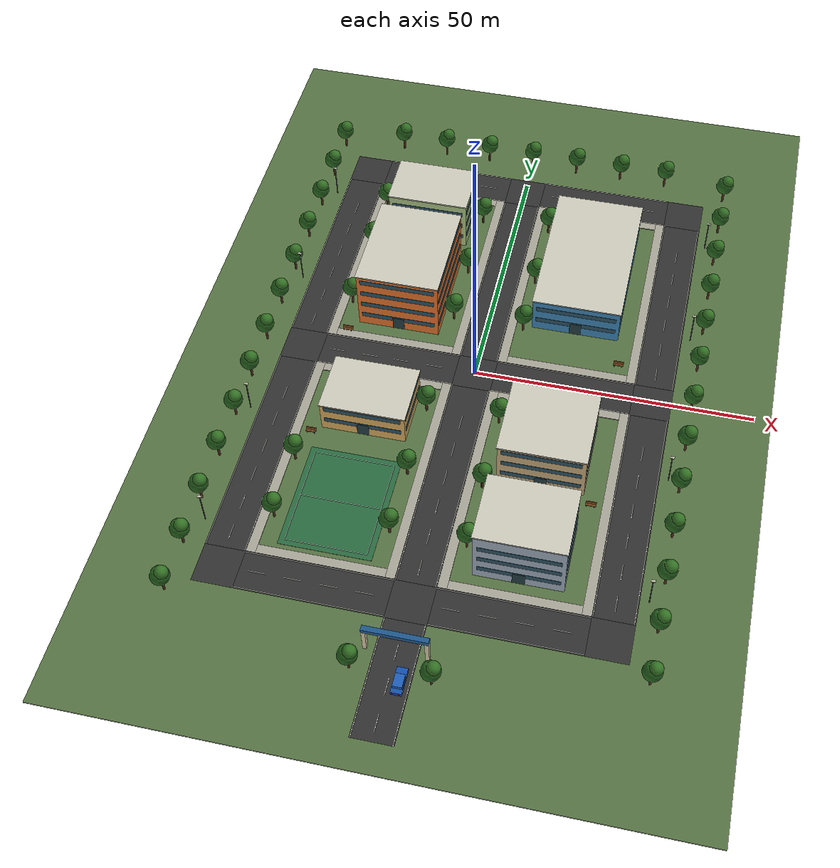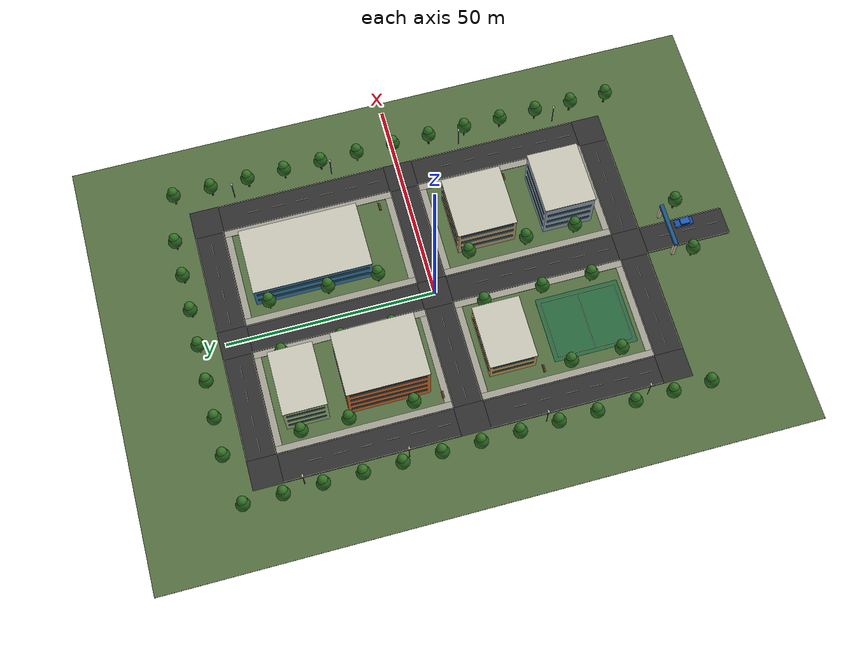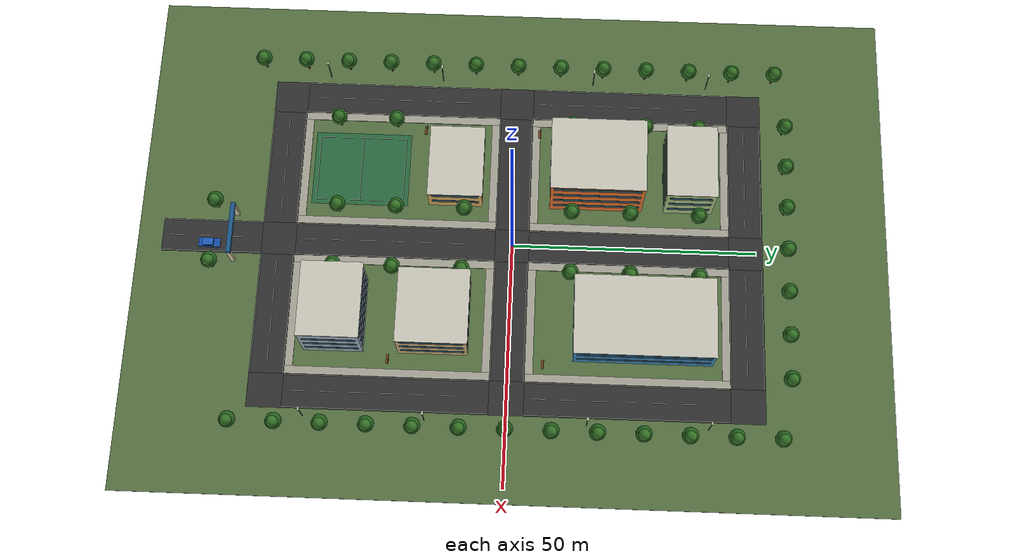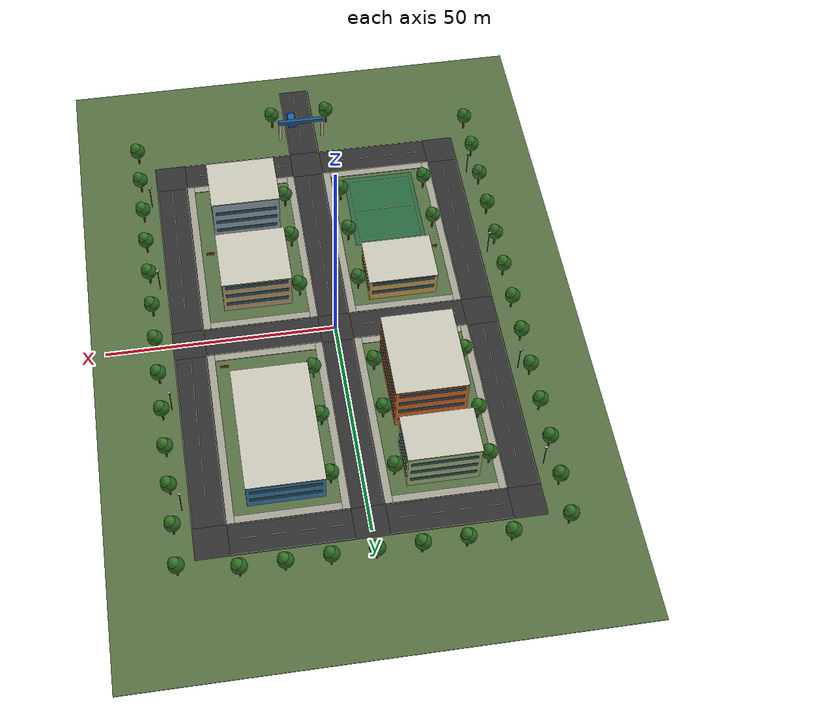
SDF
<?xml version="1.0" ?>
<sdf version="1.8">
  <world name="ute_city_v1">
    <physics name="physics" type="ignored">
      <max_step_size>0.001</max_step_size>
      <real_time_factor>1</real_time_factor>
    </physics>
    <gravity>0 0 -9.81</gravity>
    <plugin filename="gz-sim-physics-system" name="gz::sim::systems::Physics" />
    <plugin filename="gz-sim-user-commands-system" name="gz::sim::systems::UserCommands" />
    <plugin filename="gz-sim-scene-broadcaster-system" name="gz::sim::systems::SceneBroadcaster" />
    <plugin filename="gz-sim-sensors-system" name="gz::sim::systems::Sensors">
      <render_engine>ogre2</render_engine>
    </plugin>
    <scene>
      <ambient>0.48 0.48 0.48 1</ambient>
      <background>0.68 0.81 0.91 1</background>
      <shadows>true</shadows>
    </scene>
    <light name="sun" type="directional">
      <pose>0 0 60 0 0 0</pose>
      <cast_shadows>true</cast_shadows>
      <diffuse>0.85 0.83 0.77 1</diffuse>
      <specular>0.15 0.15 0.15 1</specular>
      <direction>-0.55 -0.35 -0.85</direction>
    </light>
    <gui fullscreen="false">
      <plugin filename="MinimalScene" name="3D View">
        <gz-gui>
          <title>3D View</title>
          <property type="bool" key="showTitleBar">false</property>
          <property type="string" key="state">docked</property>
        </gz-gui>
        <engine>ogre2</engine>
        <scene>scene</scene>
        <ambient_light>0.4 0.4 0.4</ambient_light>
        <background_color>0.8 0.8 0.8</background_color>
        <camera_pose>110 -140 125 0 0.62 2.23</camera_pose>
      </plugin>
      <plugin filename="EntityContextMenuPlugin" name="Entity context menu">
        <gz-gui>
          <property key="state" type="string">floating</property>
          <property key="width" type="double">5</property>
          <property key="height" type="double">5</property>
          <property key="showTitleBar" type="bool">false</property>
        </gz-gui>
      </plugin>
      <plugin filename="GzSceneManager" name="Scene Manager">
        <gz-gui>
          <property key="resizable" type="bool">false</property>
          <property key="width" type="double">5</property>
          <property key="height" type="double">5</property>
          <property key="state" type="string">floating</property>
          <property key="showTitleBar" type="bool">false</property>
        </gz-gui>
      </plugin>
      <plugin filename="InteractiveViewControl" name="Interactive view control">
        <gz-gui>
          <property key="resizable" type="bool">false</property>
          <property key="width" type="double">5</property>
          <property key="height" type="double">5</property>
          <property key="state" type="string">floating</property>
          <property key="showTitleBar" type="bool">false</property>
        </gz-gui>
      </plugin>
      <plugin filename="CameraTracking" name="Camera Tracking">
        <gz-gui>
          <property key="resizable" type="bool">false</property>
          <property key="width" type="double">5</property>
          <property key="height" type="double">5</property>
          <property key="state" type="string">floating</property>
          <property key="showTitleBar" type="bool">false</property>
        </gz-gui>
      </plugin>
      <plugin filename="MarkerManager" name="Marker manager">
        <gz-gui>
          <property key="resizable" type="bool">false</property>
          <property key="width" type="double">5</property>
          <property key="height" type="double">5</property>
          <property key="state" type="string">floating</property>
          <property key="showTitleBar" type="bool">false</property>
        </gz-gui>
      </plugin>
      <plugin filename="SelectEntities" name="Select Entities">
        <gz-gui>
          <property key="resizable" type="bool">false</property>
          <property key="width" type="double">5</property>
          <property key="height" type="double">5</property>
          <property key="state" type="string">floating</property>
          <property key="showTitleBar" type="bool">false</property>
        </gz-gui>
      </plugin>
      <plugin filename="Spawn" name="Spawn Entities">
        <gz-gui>
          <property key="resizable" type="bool">false</property>
          <property key="width" type="double">5</property>
          <property key="height" type="double">5</property>
          <property key="state" type="string">floating</property>
          <property key="showTitleBar" type="bool">false</property>
        </gz-gui>
      </plugin>
      <plugin filename="VisualizationCapabilities" name="Visualization Capabilities">
        <gz-gui>
          <property key="resizable" type="bool">false</property>
          <property key="width" type="double">5</property>
          <property key="height" type="double">5</property>
          <property key="state" type="string">floating</property>
          <property key="showTitleBar" type="bool">false</property>
        </gz-gui>
      </plugin>
      <plugin filename="WorldControl" name="World control">
        <gz-gui>
          <title>World control</title>
          <property type="bool" key="showTitleBar">false</property>
          <property type="bool" key="resizable">false</property>
          <property type="double" key="height">72</property>
          <property type="double" key="z">1</property>
          <property type="string" key="state">floating</property>
          <anchors target="3D View">
            <line own="left" target="left" />
            <line own="bottom" target="bottom" />
          </anchors>
        </gz-gui>
        <play_pause>true</play_pause>
        <step>true</step>
        <start_paused>false</start_paused>
        <use_event>true</use_event>
      </plugin>
      <plugin filename="WorldStats" name="World stats">
        <gz-gui>
          <title>World stats</title>
          <property type="bool" key="showTitleBar">false</property>
          <property type="bool" key="resizable">false</property>
          <property type="double" key="height">110</property>
          <property type="double" key="width">290</property>
          <property type="double" key="z">1</property>
          <property type="string" key="state">floating</property>
          <anchors target="3D View">
            <line own="right" target="right" />
            <line own="bottom" target="bottom" />
          </anchors>
        </gz-gui>
        <sim_time>true</sim_time>
        <real_time>true</real_time>
        <real_time_factor>true</real_time_factor>
        <iterations>true</iterations>
      </plugin>
      <plugin filename="Shapes" name="Shapes">
        <gz-gui>
          <property key="resizable" type="bool">false</property>
          <property key="x" type="double">0</property>
          <property key="y" type="double">0</property>
          <property key="width" type="double">300</property>
          <property key="height" type="double">50</property>
          <property key="state" type="string">floating</property>
          <property key="showTitleBar" type="bool">false</property>
          <property key="cardBackground" type="string">#666666</property>
        </gz-gui>
      </plugin>
      <plugin filename="Lights" name="Lights">
        <gz-gui>
          <property key="resizable" type="bool">false</property>
          <property key="x" type="double">300</property>
          <property key="y" type="double">0</property>
          <property key="width" type="double">150</property>
          <property key="height" type="double">50</property>
          <property key="state" type="string">floating</property>
          <property key="showTitleBar" type="bool">false</property>
          <property key="cardBackground" type="string">#666666</property>
        </gz-gui>
      </plugin>
      <plugin filename="TransformControl" name="Transform control">
        <gz-gui>
          <property key="resizable" type="bool">false</property>
          <property key="x" type="double">0</property>
          <property key="y" type="double">50</property>
          <property key="width" type="double">250</property>
          <property key="height" type="double">50</property>
          <property key="state" type="string">floating</property>
          <property key="showTitleBar" type="bool">false</property>
          <property key="cardBackground" type="string">#777777</property>
        </gz-gui>
      </plugin>
      <plugin filename="Screenshot" name="Screenshot">
        <gz-gui>
          <property key="resizable" type="bool">false</property>
          <property key="x" type="double">250</property>
          <property key="y" type="double">50</property>
          <property key="width" type="double">50</property>
          <property key="height" type="double">50</property>
          <property key="state" type="string">floating</property>
          <property key="showTitleBar" type="bool">false</property>
          <property key="cardBackground" type="string">#777777</property>
        </gz-gui>
      </plugin>
      <plugin filename="CopyPaste" name="CopyPaste">
        <gz-gui>
          <property key="resizable" type="bool">false</property>
          <property key="x" type="double">300</property>
          <property key="y" type="double">50</property>
          <property key="width" type="double">100</property>
          <property key="height" type="double">50</property>
          <property key="state" type="string">floating</property>
          <property key="showTitleBar" type="bool">false</property>
          <property key="cardBackground" type="string">#777777</property>
        </gz-gui>
      </plugin>
      <plugin filename="ComponentInspector" name="Component inspector">
        <gz-gui>
          <property type="bool" key="showTitleBar">false</property>
          <property type="string" key="state">docked</property>
        </gz-gui>
      </plugin>
      <plugin filename="EntityTree" name="Entity tree">
        <gz-gui>
          <property type="bool" key="showTitleBar">false</property>
          <property type="string" key="state">docked</property>
        </gz-gui>
      </plugin>
      <plugin filename="Teleop" name="Drive UTE car">
        <gz-gui>
          <title>Drive UTE car</title>
          <property type="string" key="state">docked</property>
        </gz-gui>
        <topic>/model/ute_car/cmd_vel</topic>
      </plugin>
      <plugin filename="ImageDisplay" name="Front camera">
        <gz-gui>
          <title>Front camera</title>
          <property type="string" key="state">docked</property>
        </gz-gui>
        <topic>/ute_car/front_camera/image</topic>
      </plugin>
    </gui>
    <model name="ground">
      <static>true</static>
      <pose>0 0 0 0 0 0</pose>
      <link name="link">
        <visual name="ground">
          <pose>0 0 -0.1 0 0 0</pose>
          <geometry>
            <box>
              <size>106 154 0.2</size>
            </box>
          </geometry>
          <material>
            <ambient>0.35 0.46 0.27 1</ambient>
            <diffuse>0.35 0.46 0.27 1</diffuse>
            <specular>0.05 0.05 0.05 1</specular>
          </material>
          <cast_shadows>true</cast_shadows>
        </visual>
        <collision name="ground_collision">
          <pose>0 0 -0.1 0 0 0</pose>
          <geometry>
            <box>
              <size>106 154 0.2</size>
            </box>
          </geometry>
        </collision>
      </link>
    </model>
    <model name="roads_and_markings">
      <static>true</static>
      <pose>0 0 0 0 0 0</pose>
      <link name="link">
        <visual name="asphalt_0">
          <pose>-32 -24 0.001 0 0 0</pose>
          <geometry>
            <box>
              <size>7 41 0.002</size>
            </box>
          </geometry>
          <material>
            <ambient>0.2 0.2 0.2 1</ambient>
            <diffuse>0.2 0.2 0.2 1</diffuse>
            <specular>0.05 0.05 0.05 1</specular>
          </material>
          <cast_shadows>false</cast_shadows>
        </visual>
        <visual name="edge_0_-1">
          <pose>-35.32 -24 0.005 0 0 0</pose>
          <geometry>
            <box>
              <size>0.12 41 0.002</size>
            </box>
          </geometry>
          <material>
            <ambient>0.95 0.95 0.92 1</ambient>
            <diffuse>0.95 0.95 0.92 1</diffuse>
            <specular>0.05 0.05 0.05 1</specular>
          </material>
          <cast_shadows>false</cast_shadows>
        </visual>
        <visual name="edge_0_1">
          <pose>-28.68 -24 0.005 0 0 0</pose>
          <geometry>
            <box>
              <size>0.12 41 0.002</size>
            </box>
          </geometry>
          <material>
            <ambient>0.95 0.95 0.92 1</ambient>
            <diffuse>0.95 0.95 0.92 1</diffuse>
            <specular>0.05 0.05 0.05 1</specular>
          </material>
          <cast_shadows>false</cast_shadows>
        </visual>
        <visual name="dash_0_0">
          <pose>-32 -41.5 0.005 0 0 0</pose>
          <geometry>
            <box>
              <size>0.12 3 0.002</size>
            </box>
          </geometry>
          <material>
            <ambient>0.95 0.95 0.92 1</ambient>
            <diffuse>0.95 0.95 0.92 1</diffuse>
            <specular>0.05 0.05 0.05 1</specular>
          </material>
          <cast_shadows>false</cast_shadows>
        </visual>
        <visual name="dash_0_1">
          <pose>-32 -35.5 0.005 0 0 0</pose>
          <geometry>
            <box>
              <size>0.12 3 0.002</size>
            </box>
          </geometry>
          <material>
            <ambient>0.95 0.95 0.92 1</ambient>
            <diffuse>0.95 0.95 0.92 1</diffuse>
            <specular>0.05 0.05 0.05 1</specular>
          </material>
          <cast_shadows>false</cast_shadows>
        </visual>
        <visual name="dash_0_2">
          <pose>-32 -29.5 0.005 0 0 0</pose>
          <geometry>
            <box>
              <size>0.12 3 0.002</size>
            </box>
          </geometry>
          <material>
            <ambient>0.95 0.95 0.92 1</ambient>
            <diffuse>0.95 0.95 0.92 1</diffuse>
            <specular>0.05 0.05 0.05 1</specular>
          </material>
          <cast_shadows>false</cast_shadows>
        </visual>
        <visual name="dash_0_3">
          <pose>-32 -23.5 0.005 0 0 0</pose>
          <geometry>
            <box>
              <size>0.12 3 0.002</size>
            </box>
          </geometry>
          <material>
            <ambient>0.95 0.95 0.92 1</ambient>
            <diffuse>0.95 0.95 0.92 1</diffuse>
            <specular>0.05 0.05 0.05 1</specular>
          </material>
          <cast_shadows>false</cast_shadows>
        </visual>
        <visual name="dash_0_4">
          <pose>-32 -17.5 0.005 0 0 0</pose>
          <geometry>
            <box>
              <size>0.12 3 0.002</size>
            </box>
          </geometry>
          <material>
            <ambient>0.95 0.95 0.92 1</ambient>
            <diffuse>0.95 0.95 0.92 1</diffuse>
            <specular>0.05 0.05 0.05 1</specular>
          </material>
          <cast_shadows>false</cast_shadows>
        </visual>
        <visual name="dash_0_5">
          <pose>-32 -11.5 0.005 0 0 0</pose>
          <geometry>
            <box>
              <size>0.12 3 0.002</size>
            </box>
          </geometry>
          <material>
            <ambient>0.95 0.95 0.92 1</ambient>
            <diffuse>0.95 0.95 0.92 1</diffuse>
            <specular>0.05 0.05 0.05 1</specular>
          </material>
          <cast_shadows>false</cast_shadows>
        </visual>
        <visual name="asphalt_1">
          <pose>-32 24 0.001 0 0 0</pose>
          <geometry>
            <box>
              <size>7 41 0.002</size>
            </box>
          </geometry>
          <material>
            <ambient>0.2 0.2 0.2 1</ambient>
            <diffuse>0.2 0.2 0.2 1</diffuse>
            <specular>0.05 0.05 0.05 1</specular>
          </material>
          <cast_shadows>false</cast_shadows>
        </visual>
        <visual name="edge_1_-1">
          <pose>-35.32 24 0.005 0 0 0</pose>
          <geometry>
            <box>
              <size>0.12 41 0.002</size>
            </box>
          </geometry>
          <material>
            <ambient>0.95 0.95 0.92 1</ambient>
            <diffuse>0.95 0.95 0.92 1</diffuse>
            <specular>0.05 0.05 0.05 1</specular>
          </material>
          <cast_shadows>false</cast_shadows>
        </visual>
        <visual name="edge_1_1">
          <pose>-28.68 24 0.005 0 0 0</pose>
          <geometry>
            <box>
              <size>0.12 41 0.002</size>
            </box>
          </geometry>
          <material>
            <ambient>0.95 0.95 0.92 1</ambient>
            <diffuse>0.95 0.95 0.92 1</diffuse>
            <specular>0.05 0.05 0.05 1</specular>
          </material>
          <cast_shadows>false</cast_shadows>
        </visual>
        <visual name="dash_1_0">
          <pose>-32 6.5 0.005 0 0 0</pose>
          <geometry>
            <box>
              <size>0.12 3 0.002</size>
            </box>
          </geometry>
          <material>
            <ambient>0.95 0.95 0.92 1</ambient>
            <diffuse>0.95 0.95 0.92 1</diffuse>
            <specular>0.05 0.05 0.05 1</specular>
          </material>
          <cast_shadows>false</cast_shadows>
        </visual>
        <visual name="dash_1_1">
          <pose>-32 12.5 0.005 0 0 0</pose>
          <geometry>
            <box>
              <size>0.12 3 0.002</size>
            </box>
          </geometry>
          <material>
            <ambient>0.95 0.95 0.92 1</ambient>
            <diffuse>0.95 0.95 0.92 1</diffuse>
            <specular>0.05 0.05 0.05 1</specular>
          </material>
          <cast_shadows>false</cast_shadows>
        </visual>
        <visual name="dash_1_2">
          <pose>-32 18.5 0.005 0 0 0</pose>
          <geometry>
            <box>
              <size>0.12 3 0.002</size>
            </box>
          </geometry>
          <material>
            <ambient>0.95 0.95 0.92 1</ambient>
            <diffuse>0.95 0.95 0.92 1</diffuse>
            <specular>0.05 0.05 0.05 1</specular>
          </material>
          <cast_shadows>false</cast_shadows>
        </visual>
        <visual name="dash_1_3">
          <pose>-32 24.5 0.005 0 0 0</pose>
          <geometry>
            <box>
              <size>0.12 3 0.002</size>
            </box>
          </geometry>
          <material>
            <ambient>0.95 0.95 0.92 1</ambient>
            <diffuse>0.95 0.95 0.92 1</diffuse>
            <specular>0.05 0.05 0.05 1</specular>
          </material>
          <cast_shadows>false</cast_shadows>
        </visual>
        <visual name="dash_1_4">
          <pose>-32 30.5 0.005 0 0 0</pose>
          <geometry>
            <box>
              <size>0.12 3 0.002</size>
            </box>
          </geometry>
          <material>
            <ambient>0.95 0.95 0.92 1</ambient>
            <diffuse>0.95 0.95 0.92 1</diffuse>
            <specular>0.05 0.05 0.05 1</specular>
          </material>
          <cast_shadows>false</cast_shadows>
        </visual>
        <visual name="dash_1_5">
          <pose>-32 36.5 0.005 0 0 0</pose>
          <geometry>
            <box>
              <size>0.12 3 0.002</size>
            </box>
          </geometry>
          <material>
            <ambient>0.95 0.95 0.92 1</ambient>
            <diffuse>0.95 0.95 0.92 1</diffuse>
            <specular>0.05 0.05 0.05 1</specular>
          </material>
          <cast_shadows>false</cast_shadows>
        </visual>
        <visual name="asphalt_2">
          <pose>0 -24 0.001 0 0 0</pose>
          <geometry>
            <box>
              <size>7 41 0.002</size>
            </box>
          </geometry>
          <material>
            <ambient>0.2 0.2 0.2 1</ambient>
            <diffuse>0.2 0.2 0.2 1</diffuse>
            <specular>0.05 0.05 0.05 1</specular>
          </material>
          <cast_shadows>false</cast_shadows>
        </visual>
        <visual name="edge_2_-1">
          <pose>-3.32 -24 0.005 0 0 0</pose>
          <geometry>
            <box>
              <size>0.12 41 0.002</size>
            </box>
          </geometry>
          <material>
            <ambient>0.95 0.95 0.92 1</ambient>
            <diffuse>0.95 0.95 0.92 1</diffuse>
            <specular>0.05 0.05 0.05 1</specular>
          </material>
          <cast_shadows>false</cast_shadows>
        </visual>
        <visual name="edge_2_1">
          <pose>3.32 -24 0.005 0 0 0</pose>
          <geometry>
            <box>
              <size>0.12 41 0.002</size>
            </box>
          </geometry>
          <material>
            <ambient>0.95 0.95 0.92 1</ambient>
            <diffuse>0.95 0.95 0.92 1</diffuse>
            <specular>0.05 0.05 0.05 1</specular>
          </material>
          <cast_shadows>false</cast_shadows>
        </visual>
        <visual name="dash_2_0">
          <pose>0 -41.5 0.005 0 0 0</pose>
          <geometry>
            <box>
              <size>0.12 3 0.002</size>
            </box>
          </geometry>
          <material>
            <ambient>0.95 0.95 0.92 1</ambient>
            <diffuse>0.95 0.95 0.92 1</diffuse>
            <specular>0.05 0.05 0.05 1</specular>
          </material>
          <cast_shadows>false</cast_shadows>
        </visual>
        <visual name="dash_2_1">
          <pose>0 -35.5 0.005 0 0 0</pose>
          <geometry>
            <box>
              <size>0.12 3 0.002</size>
            </box>
          </geometry>
          <material>
            <ambient>0.95 0.95 0.92 1</ambient>
            <diffuse>0.95 0.95 0.92 1</diffuse>
            <specular>0.05 0.05 0.05 1</specular>
          </material>
          <cast_shadows>false</cast_shadows>
        </visual>
        <visual name="dash_2_2">
          <pose>0 -29.5 0.005 0 0 0</pose>
          <geometry>
            <box>
              <size>0.12 3 0.002</size>
            </box>
          </geometry>
          <material>
            <ambient>0.95 0.95 0.92 1</ambient>
            <diffuse>0.95 0.95 0.92 1</diffuse>
            <specular>0.05 0.05 0.05 1</specular>
          </material>
          <cast_shadows>false</cast_shadows>
        </visual>
        <visual name="dash_2_3">
          <pose>0 -23.5 0.005 0 0 0</pose>
          <geometry>
            <box>
              <size>0.12 3 0.002</size>
            </box>
          </geometry>
          <material>
            <ambient>0.95 0.95 0.92 1</ambient>
            <diffuse>0.95 0.95 0.92 1</diffuse>
            <specular>0.05 0.05 0.05 1</specular>
          </material>
          <cast_shadows>false</cast_shadows>
        </visual>
        <visual name="dash_2_4">
          <pose>0 -17.5 0.005 0 0 0</pose>
          <geometry>
            <box>
              <size>0.12 3 0.002</size>
            </box>
          </geometry>
          <material>
            <ambient>0.95 0.95 0.92 1</ambient>
            <diffuse>0.95 0.95 0.92 1</diffuse>
            <specular>0.05 0.05 0.05 1</specular>
          </material>
          <cast_shadows>false</cast_shadows>
        </visual>
        <visual name="dash_2_5">
          <pose>0 -11.5 0.005 0 0 0</pose>
          <geometry>
            <box>
              <size>0.12 3 0.002</size>
            </box>
          </geometry>
          <material>
            <ambient>0.95 0.95 0.92 1</ambient>
            <diffuse>0.95 0.95 0.92 1</diffuse>
            <specular>0.05 0.05 0.05 1</specular>
          </material>
          <cast_shadows>false</cast_shadows>
        </visual>
        <visual name="asphalt_3">
          <pose>0 24 0.001 0 0 0</pose>
          <geometry>
            <box>
              <size>7 41 0.002</size>
            </box>
          </geometry>
          <material>
            <ambient>0.2 0.2 0.2 1</ambient>
            <diffuse>0.2 0.2 0.2 1</diffuse>
            <specular>0.05 0.05 0.05 1</specular>
          </material>
          <cast_shadows>false</cast_shadows>
        </visual>
        <visual name="edge_3_-1">
          <pose>-3.32 24 0.005 0 0 0</pose>
          <geometry>
            <box>
              <size>0.12 41 0.002</size>
            </box>
          </geometry>
          <material>
            <ambient>0.95 0.95 0.92 1</ambient>
            <diffuse>0.95 0.95 0.92 1</diffuse>
            <specular>0.05 0.05 0.05 1</specular>
          </material>
          <cast_shadows>false</cast_shadows>
        </visual>
        <visual name="edge_3_1">
          <pose>3.32 24 0.005 0 0 0</pose>
          <geometry>
            <box>
              <size>0.12 41 0.002</size>
            </box>
          </geometry>
          <material>
            <ambient>0.95 0.95 0.92 1</ambient>
            <diffuse>0.95 0.95 0.92 1</diffuse>
            <specular>0.05 0.05 0.05 1</specular>
          </material>
          <cast_shadows>false</cast_shadows>
        </visual>
        <visual name="dash_3_0">
          <pose>0 6.5 0.005 0 0 0</pose>
          <geometry>
            <box>
              <size>0.12 3 0.002</size>
            </box>
          </geometry>
          <material>
            <ambient>0.95 0.95 0.92 1</ambient>
            <diffuse>0.95 0.95 0.92 1</diffuse>
            <specular>0.05 0.05 0.05 1</specular>
          </material>
          <cast_shadows>false</cast_shadows>
        </visual>
        <visual name="dash_3_1">
          <pose>0 12.5 0.005 0 0 0</pose>
          <geometry>
            <box>
              <size>0.12 3 0.002</size>
            </box>
          </geometry>
          <material>
            <ambient>0.95 0.95 0.92 1</ambient>
            <diffuse>0.95 0.95 0.92 1</diffuse>
            <specular>0.05 0.05 0.05 1</specular>
          </material>
          <cast_shadows>false</cast_shadows>
        </visual>
        <visual name="dash_3_2">
          <pose>0 18.5 0.005 0 0 0</pose>
          <geometry>
            <box>
              <size>0.12 3 0.002</size>
            </box>
          </geometry>
          <material>
            <ambient>0.95 0.95 0.92 1</ambient>
            <diffuse>0.95 0.95 0.92 1</diffuse>
            <specular>0.05 0.05 0.05 1</specular>
          </material>
          <cast_shadows>false</cast_shadows>
        </visual>
        <visual name="dash_3_3">
          <pose>0 24.5 0.005 0 0 0</pose>
          <geometry>
            <box>
              <size>0.12 3 0.002</size>
            </box>
          </geometry>
          <material>
            <ambient>0.95 0.95 0.92 1</ambient>
            <diffuse>0.95 0.95 0.92 1</diffuse>
            <specular>0.05 0.05 0.05 1</specular>
          </material>
          <cast_shadows>false</cast_shadows>
        </visual>
        <visual name="dash_3_4">
          <pose>0 30.5 0.005 0 0 0</pose>
          <geometry>
            <box>
              <size>0.12 3 0.002</size>
            </box>
          </geometry>
          <material>
            <ambient>0.95 0.95 0.92 1</ambient>
            <diffuse>0.95 0.95 0.92 1</diffuse>
            <specular>0.05 0.05 0.05 1</specular>
          </material>
          <cast_shadows>false</cast_shadows>
        </visual>
        <visual name="dash_3_5">
          <pose>0 36.5 0.005 0 0 0</pose>
          <geometry>
            <box>
              <size>0.12 3 0.002</size>
            </box>
          </geometry>
          <material>
            <ambient>0.95 0.95 0.92 1</ambient>
            <diffuse>0.95 0.95 0.92 1</diffuse>
            <specular>0.05 0.05 0.05 1</specular>
          </material>
          <cast_shadows>false</cast_shadows>
        </visual>
        <visual name="asphalt_4">
          <pose>32 -24 0.001 0 0 0</pose>
          <geometry>
            <box>
              <size>7 41 0.002</size>
            </box>
          </geometry>
          <material>
            <ambient>0.2 0.2 0.2 1</ambient>
            <diffuse>0.2 0.2 0.2 1</diffuse>
            <specular>0.05 0.05 0.05 1</specular>
          </material>
          <cast_shadows>false</cast_shadows>
        </visual>
        <visual name="edge_4_-1">
          <pose>28.68 -24 0.005 0 0 0</pose>
          <geometry>
            <box>
              <size>0.12 41 0.002</size>
            </box>
          </geometry>
          <material>
            <ambient>0.95 0.95 0.92 1</ambient>
            <diffuse>0.95 0.95 0.92 1</diffuse>
            <specular>0.05 0.05 0.05 1</specular>
          </material>
          <cast_shadows>false</cast_shadows>
        </visual>
        <visual name="edge_4_1">
          <pose>35.32 -24 0.005 0 0 0</pose>
          <geometry>
            <box>
              <size>0.12 41 0.002</size>
            </box>
          </geometry>
          <material>
            <ambient>0.95 0.95 0.92 1</ambient>
            <diffuse>0.95 0.95 0.92 1</diffuse>
            <specular>0.05 0.05 0.05 1</specular>
          </material>
          <cast_shadows>false</cast_shadows>
        </visual>
        <visual name="dash_4_0">
          <pose>32 -41.5 0.005 0 0 0</pose>
          <geometry>
            <box>
              <size>0.12 3 0.002</size>
            </box>
          </geometry>
          <material>
            <ambient>0.95 0.95 0.92 1</ambient>
            <diffuse>0.95 0.95 0.92 1</diffuse>
            <specular>0.05 0.05 0.05 1</specular>
          </material>
          <cast_shadows>false</cast_shadows>
        </visual>
        <visual name="dash_4_1">
          <pose>32 -35.5 0.005 0 0 0</pose>
          <geometry>
            <box>
              <size>0.12 3 0.002</size>
            </box>
          </geometry>
          <material>
            <ambient>0.95 0.95 0.92 1</ambient>
            <diffuse>0.95 0.95 0.92 1</diffuse>
            <specular>0.05 0.05 0.05 1</specular>
          </material>
          <cast_shadows>false</cast_shadows>
        </visual>
        <visual name="dash_4_2">
          <pose>32 -29.5 0.005 0 0 0</pose>
          <geometry>
            <box>
              <size>0.12 3 0.002</size>
            </box>
          </geometry>
          <material>
            <ambient>0.95 0.95 0.92 1</ambient>
            <diffuse>0.95 0.95 0.92 1</diffuse>
            <specular>0.05 0.05 0.05 1</specular>
          </material>
          <cast_shadows>false</cast_shadows>
        </visual>
        <visual name="dash_4_3">
          <pose>32 -23.5 0.005 0 0 0</pose>
          <geometry>
            <box>
              <size>0.12 3 0.002</size>
            </box>
          </geometry>
          <material>
            <ambient>0.95 0.95 0.92 1</ambient>
            <diffuse>0.95 0.95 0.92 1</diffuse>
            <specular>0.05 0.05 0.05 1</specular>
          </material>
          <cast_shadows>false</cast_shadows>
        </visual>
        <visual name="dash_4_4">
          <pose>32 -17.5 0.005 0 0 0</pose>
          <geometry>
            <box>
              <size>0.12 3 0.002</size>
            </box>
          </geometry>
          <material>
            <ambient>0.95 0.95 0.92 1</ambient>
            <diffuse>0.95 0.95 0.92 1</diffuse>
            <specular>0.05 0.05 0.05 1</specular>
          </material>
          <cast_shadows>false</cast_shadows>
        </visual>
        <visual name="dash_4_5">
          <pose>32 -11.5 0.005 0 0 0</pose>
          <geometry>
            <box>
              <size>0.12 3 0.002</size>
            </box>
          </geometry>
          <material>
            <ambient>0.95 0.95 0.92 1</ambient>
            <diffuse>0.95 0.95 0.92 1</diffuse>
            <specular>0.05 0.05 0.05 1</specular>
          </material>
          <cast_shadows>false</cast_shadows>
        </visual>
        <visual name="asphalt_5">
          <pose>32 24 0.001 0 0 0</pose>
          <geometry>
            <box>
              <size>7 41 0.002</size>
            </box>
          </geometry>
          <material>
            <ambient>0.2 0.2 0.2 1</ambient>
            <diffuse>0.2 0.2 0.2 1</diffuse>
            <specular>0.05 0.05 0.05 1</specular>
          </material>
          <cast_shadows>false</cast_shadows>
        </visual>
        <visual name="edge_5_-1">
          <pose>28.68 24 0.005 0 0 0</pose>
          <geometry>
            <box>
              <size>0.12 41 0.002</size>
            </box>
          </geometry>
          <material>
            <ambient>0.95 0.95 0.92 1</ambient>
            <diffuse>0.95 0.95 0.92 1</diffuse>
            <specular>0.05 0.05 0.05 1</specular>
          </material>
          <cast_shadows>false</cast_shadows>
        </visual>
        <visual name="edge_5_1">
          <pose>35.32 24 0.005 0 0 0</pose>
          <geometry>
            <box>
              <size>0.12 41 0.002</size>
            </box>
          </geometry>
          <material>
            <ambient>0.95 0.95 0.92 1</ambient>
            <diffuse>0.95 0.95 0.92 1</diffuse>
            <specular>0.05 0.05 0.05 1</specular>
          </material>
          <cast_shadows>false</cast_shadows>
        </visual>
        <visual name="dash_5_0">
          <pose>32 6.5 0.005 0 0 0</pose>
          <geometry>
            <box>
              <size>0.12 3 0.002</size>
            </box>
          </geometry>
          <material>
            <ambient>0.95 0.95 0.92 1</ambient>
            <diffuse>0.95 0.95 0.92 1</diffuse>
            <specular>0.05 0.05 0.05 1</specular>
          </material>
          <cast_shadows>false</cast_shadows>
        </visual>
        <visual name="dash_5_1">
          <pose>32 12.5 0.005 0 0 0</pose>
          <geometry>
            <box>
              <size>0.12 3 0.002</size>
            </box>
          </geometry>
          <material>
            <ambient>0.95 0.95 0.92 1</ambient>
            <diffuse>0.95 0.95 0.92 1</diffuse>
            <specular>0.05 0.05 0.05 1</specular>
          </material>
          <cast_shadows>false</cast_shadows>
        </visual>
        <visual name="dash_5_2">
          <pose>32 18.5 0.005 0 0 0</pose>
          <geometry>
            <box>
              <size>0.12 3 0.002</size>
            </box>
          </geometry>
          <material>
            <ambient>0.95 0.95 0.92 1</ambient>
            <diffuse>0.95 0.95 0.92 1</diffuse>
            <specular>0.05 0.05 0.05 1</specular>
          </material>
          <cast_shadows>false</cast_shadows>
        </visual>
        <visual name="dash_5_3">
          <pose>32 24.5 0.005 0 0 0</pose>
          <geometry>
            <box>
              <size>0.12 3 0.002</size>
            </box>
          </geometry>
          <material>
            <ambient>0.95 0.95 0.92 1</ambient>
            <diffuse>0.95 0.95 0.92 1</diffuse>
            <specular>0.05 0.05 0.05 1</specular>
          </material>
          <cast_shadows>false</cast_shadows>
        </visual>
        <visual name="dash_5_4">
          <pose>32 30.5 0.005 0 0 0</pose>
          <geometry>
            <box>
              <size>0.12 3 0.002</size>
            </box>
          </geometry>
          <material>
            <ambient>0.95 0.95 0.92 1</ambient>
            <diffuse>0.95 0.95 0.92 1</diffuse>
            <specular>0.05 0.05 0.05 1</specular>
          </material>
          <cast_shadows>false</cast_shadows>
        </visual>
        <visual name="dash_5_5">
          <pose>32 36.5 0.005 0 0 0</pose>
          <geometry>
            <box>
              <size>0.12 3 0.002</size>
            </box>
          </geometry>
          <material>
            <ambient>0.95 0.95 0.92 1</ambient>
            <diffuse>0.95 0.95 0.92 1</diffuse>
            <specular>0.05 0.05 0.05 1</specular>
          </material>
          <cast_shadows>false</cast_shadows>
        </visual>
        <visual name="asphalt_6">
          <pose>-16 -48 0.001 0 0 0</pose>
          <geometry>
            <box>
              <size>25 7 0.002</size>
            </box>
          </geometry>
          <material>
            <ambient>0.2 0.2 0.2 1</ambient>
            <diffuse>0.2 0.2 0.2 1</diffuse>
            <specular>0.05 0.05 0.05 1</specular>
          </material>
          <cast_shadows>false</cast_shadows>
        </visual>
        <visual name="edge_6_-1">
          <pose>-16 -51.32 0.005 0 0 0</pose>
          <geometry>
            <box>
              <size>25 0.12 0.002</size>
            </box>
          </geometry>
          <material>
            <ambient>0.95 0.95 0.92 1</ambient>
            <diffuse>0.95 0.95 0.92 1</diffuse>
            <specular>0.05 0.05 0.05 1</specular>
          </material>
          <cast_shadows>false</cast_shadows>
        </visual>
        <visual name="edge_6_1">
          <pose>-16 -44.68 0.005 0 0 0</pose>
          <geometry>
            <box>
              <size>25 0.12 0.002</size>
            </box>
          </geometry>
          <material>
            <ambient>0.95 0.95 0.92 1</ambient>
            <diffuse>0.95 0.95 0.92 1</diffuse>
            <specular>0.05 0.05 0.05 1</specular>
          </material>
          <cast_shadows>false</cast_shadows>
        </visual>
        <visual name="dash_6_0">
          <pose>-25.5 -48 0.005 0 0 0</pose>
          <geometry>
            <box>
              <size>3 0.12 0.002</size>
            </box>
          </geometry>
          <material>
            <ambient>0.95 0.95 0.92 1</ambient>
            <diffuse>0.95 0.95 0.92 1</diffuse>
            <specular>0.05 0.05 0.05 1</specular>
          </material>
          <cast_shadows>false</cast_shadows>
        </visual>
        <visual name="dash_6_1">
          <pose>-19.5 -48 0.005 0 0 0</pose>
          <geometry>
            <box>
              <size>3 0.12 0.002</size>
            </box>
          </geometry>
          <material>
            <ambient>0.95 0.95 0.92 1</ambient>
            <diffuse>0.95 0.95 0.92 1</diffuse>
            <specular>0.05 0.05 0.05 1</specular>
          </material>
          <cast_shadows>false</cast_shadows>
        </visual>
        <visual name="dash_6_2">
          <pose>-13.5 -48 0.005 0 0 0</pose>
          <geometry>
            <box>
              <size>3 0.12 0.002</size>
            </box>
          </geometry>
          <material>
            <ambient>0.95 0.95 0.92 1</ambient>
            <diffuse>0.95 0.95 0.92 1</diffuse>
            <specular>0.05 0.05 0.05 1</specular>
          </material>
          <cast_shadows>false</cast_shadows>
        </visual>
        <visual name="dash_6_3">
          <pose>-7.5 -48 0.005 0 0 0</pose>
          <geometry>
            <box>
              <size>3 0.12 0.002</size>
            </box>
          </geometry>
          <material>
            <ambient>0.95 0.95 0.92 1</ambient>
            <diffuse>0.95 0.95 0.92 1</diffuse>
            <specular>0.05 0.05 0.05 1</specular>
          </material>
          <cast_shadows>false</cast_shadows>
        </visual>
        <visual name="asphalt_7">
          <pose>16 -48 0.001 0 0 0</pose>
          <geometry>
            <box>
              <size>25 7 0.002</size>
            </box>
          </geometry>
          <material>
            <ambient>0.2 0.2 0.2 1</ambient>
            <diffuse>0.2 0.2 0.2 1</diffuse>
            <specular>0.05 0.05 0.05 1</specular>
          </material>
          <cast_shadows>false</cast_shadows>
        </visual>
        <visual name="edge_7_-1">
          <pose>16 -51.32 0.005 0 0 0</pose>
          <geometry>
            <box>
              <size>25 0.12 0.002</size>
            </box>
          </geometry>
          <material>
            <ambient>0.95 0.95 0.92 1</ambient>
            <diffuse>0.95 0.95 0.92 1</diffuse>
            <specular>0.05 0.05 0.05 1</specular>
          </material>
          <cast_shadows>false</cast_shadows>
        </visual>
        <visual name="edge_7_1">
          <pose>16 -44.68 0.005 0 0 0</pose>
          <geometry>
            <box>
              <size>25 0.12 0.002</size>
            </box>
          </geometry>
          <material>
            <ambient>0.95 0.95 0.92 1</ambient>
            <diffuse>0.95 0.95 0.92 1</diffuse>
            <specular>0.05 0.05 0.05 1</specular>
          </material>
          <cast_shadows>false</cast_shadows>
        </visual>
        <visual name="dash_7_0">
          <pose>6.5 -48 0.005 0 0 0</pose>
          <geometry>
            <box>
              <size>3 0.12 0.002</size>
            </box>
          </geometry>
          <material>
            <ambient>0.95 0.95 0.92 1</ambient>
            <diffuse>0.95 0.95 0.92 1</diffuse>
            <specular>0.05 0.05 0.05 1</specular>
          </material>
          <cast_shadows>false</cast_shadows>
        </visual>
        <visual name="dash_7_1">
          <pose>12.5 -48 0.005 0 0 0</pose>
          <geometry>
            <box>
              <size>3 0.12 0.002</size>
            </box>
          </geometry>
          <material>
            <ambient>0.95 0.95 0.92 1</ambient>
            <diffuse>0.95 0.95 0.92 1</diffuse>
            <specular>0.05 0.05 0.05 1</specular>
          </material>
          <cast_shadows>false</cast_shadows>
        </visual>
        <visual name="dash_7_2">
          <pose>18.5 -48 0.005 0 0 0</pose>
          <geometry>
            <box>
              <size>3 0.12 0.002</size>
            </box>
          </geometry>
          <material>
            <ambient>0.95 0.95 0.92 1</ambient>
            <diffuse>0.95 0.95 0.92 1</diffuse>
            <specular>0.05 0.05 0.05 1</specular>
          </material>
          <cast_shadows>false</cast_shadows>
        </visual>
        <visual name="dash_7_3">
          <pose>24.5 -48 0.005 0 0 0</pose>
          <geometry>
            <box>
              <size>3 0.12 0.002</size>
            </box>
          </geometry>
          <material>
            <ambient>0.95 0.95 0.92 1</ambient>
            <diffuse>0.95 0.95 0.92 1</diffuse>
            <specular>0.05 0.05 0.05 1</specular>
          </material>
          <cast_shadows>false</cast_shadows>
        </visual>
        <visual name="asphalt_8">
          <pose>-16 0 0.001 0 0 0</pose>
          <geometry>
            <box>
              <size>25 7 0.002</size>
            </box>
          </geometry>
          <material>
            <ambient>0.2 0.2 0.2 1</ambient>
            <diffuse>0.2 0.2 0.2 1</diffuse>
            <specular>0.05 0.05 0.05 1</specular>
          </material>
          <cast_shadows>false</cast_shadows>
        </visual>
        <visual name="edge_8_-1">
          <pose>-16 -3.32 0.005 0 0 0</pose>
          <geometry>
            <box>
              <size>25 0.12 0.002</size>
            </box>
          </geometry>
          <material>
            <ambient>0.95 0.95 0.92 1</ambient>
            <diffuse>0.95 0.95 0.92 1</diffuse>
            <specular>0.05 0.05 0.05 1</specular>
          </material>
          <cast_shadows>false</cast_shadows>
        </visual>
        <visual name="edge_8_1">
          <pose>-16 3.32 0.005 0 0 0</pose>
          <geometry>
            <box>
              <size>25 0.12 0.002</size>
            </box>
          </geometry>
          <material>
            <ambient>0.95 0.95 0.92 1</ambient>
            <diffuse>0.95 0.95 0.92 1</diffuse>
            <specular>0.05 0.05 0.05 1</specular>
          </material>
          <cast_shadows>false</cast_shadows>
        </visual>
        <visual name="dash_8_0">
          <pose>-25.5 0 0.005 0 0 0</pose>
          <geometry>
            <box>
              <size>3 0.12 0.002</size>
            </box>
          </geometry>
          <material>
            <ambient>0.95 0.95 0.92 1</ambient>
            <diffuse>0.95 0.95 0.92 1</diffuse>
            <specular>0.05 0.05 0.05 1</specular>
          </material>
          <cast_shadows>false</cast_shadows>
        </visual>
        <visual name="dash_8_1">
          <pose>-19.5 0 0.005 0 0 0</pose>
          <geometry>
            <box>
              <size>3 0.12 0.002</size>
            </box>
          </geometry>
          <material>
            <ambient>0.95 0.95 0.92 1</ambient>
            <diffuse>0.95 0.95 0.92 1</diffuse>
            <specular>0.05 0.05 0.05 1</specular>
          </material>
          <cast_shadows>false</cast_shadows>
        </visual>
        <visual name="dash_8_2">
          <pose>-13.5 0 0.005 0 0 0</pose>
          <geometry>
            <box>
              <size>3 0.12 0.002</size>
            </box>
          </geometry>
          <material>
            <ambient>0.95 0.95 0.92 1</ambient>
            <diffuse>0.95 0.95 0.92 1</diffuse>
            <specular>0.05 0.05 0.05 1</specular>
          </material>
          <cast_shadows>false</cast_shadows>
        </visual>
        <visual name="dash_8_3">
          <pose>-7.5 0 0.005 0 0 0</pose>
          <geometry>
            <box>
              <size>3 0.12 0.002</size>
            </box>
          </geometry>
          <material>
            <ambient>0.95 0.95 0.92 1</ambient>
            <diffuse>0.95 0.95 0.92 1</diffuse>
            <specular>0.05 0.05 0.05 1</specular>
          </material>
          <cast_shadows>false</cast_shadows>
        </visual>
        <visual name="asphalt_9">
          <pose>16 0 0.001 0 0 0</pose>
          <geometry>
            <box>
              <size>25 7 0.002</size>
            </box>
          </geometry>
          <material>
            <ambient>0.2 0.2 0.2 1</ambient>
            <diffuse>0.2 0.2 0.2 1</diffuse>
            <specular>0.05 0.05 0.05 1</specular>
          </material>
          <cast_shadows>false</cast_shadows>
        </visual>
        <visual name="edge_9_-1">
          <pose>16 -3.32 0.005 0 0 0</pose>
          <geometry>
            <box>
              <size>25 0.12 0.002</size>
            </box>
          </geometry>
          <material>
            <ambient>0.95 0.95 0.92 1</ambient>
            <diffuse>0.95 0.95 0.92 1</diffuse>
            <specular>0.05 0.05 0.05 1</specular>
          </material>
          <cast_shadows>false</cast_shadows>
        </visual>
        <visual name="edge_9_1">
          <pose>16 3.32 0.005 0 0 0</pose>
          <geometry>
            <box>
              <size>25 0.12 0.002</size>
            </box>
          </geometry>
          <material>
            <ambient>0.95 0.95 0.92 1</ambient>
            <diffuse>0.95 0.95 0.92 1</diffuse>
            <specular>0.05 0.05 0.05 1</specular>
          </material>
          <cast_shadows>false</cast_shadows>
        </visual>
        <visual name="dash_9_0">
          <pose>6.5 0 0.005 0 0 0</pose>
          <geometry>
            <box>
              <size>3 0.12 0.002</size>
            </box>
          </geometry>
          <material>
            <ambient>0.95 0.95 0.92 1</ambient>
            <diffuse>0.95 0.95 0.92 1</diffuse>
            <specular>0.05 0.05 0.05 1</specular>
          </material>
          <cast_shadows>false</cast_shadows>
        </visual>
        <visual name="dash_9_1">
          <pose>12.5 0 0.005 0 0 0</pose>
          <geometry>
            <box>
              <size>3 0.12 0.002</size>
            </box>
          </geometry>
          <material>
            <ambient>0.95 0.95 0.92 1</ambient>
            <diffuse>0.95 0.95 0.92 1</diffuse>
            <specular>0.05 0.05 0.05 1</specular>
          </material>
          <cast_shadows>false</cast_shadows>
        </visual>
        <visual name="dash_9_2">
          <pose>18.5 0 0.005 0 0 0</pose>
          <geometry>
            <box>
              <size>3 0.12 0.002</size>
            </box>
          </geometry>
          <material>
            <ambient>0.95 0.95 0.92 1</ambient>
            <diffuse>0.95 0.95 0.92 1</diffuse>
            <specular>0.05 0.05 0.05 1</specular>
          </material>
          <cast_shadows>false</cast_shadows>
        </visual>
        <visual name="dash_9_3">
          <pose>24.5 0 0.005 0 0 0</pose>
          <geometry>
            <box>
              <size>3 0.12 0.002</size>
            </box>
          </geometry>
          <material>
            <ambient>0.95 0.95 0.92 1</ambient>
            <diffuse>0.95 0.95 0.92 1</diffuse>
            <specular>0.05 0.05 0.05 1</specular>
          </material>
          <cast_shadows>false</cast_shadows>
        </visual>
        <visual name="asphalt_10">
          <pose>-16 48 0.001 0 0 0</pose>
          <geometry>
            <box>
              <size>25 7 0.002</size>
            </box>
          </geometry>
          <material>
            <ambient>0.2 0.2 0.2 1</ambient>
            <diffuse>0.2 0.2 0.2 1</diffuse>
            <specular>0.05 0.05 0.05 1</specular>
          </material>
          <cast_shadows>false</cast_shadows>
        </visual>
        <visual name="edge_10_-1">
          <pose>-16 44.68 0.005 0 0 0</pose>
          <geometry>
            <box>
              <size>25 0.12 0.002</size>
            </box>
          </geometry>
          <material>
            <ambient>0.95 0.95 0.92 1</ambient>
            <diffuse>0.95 0.95 0.92 1</diffuse>
            <specular>0.05 0.05 0.05 1</specular>
          </material>
          <cast_shadows>false</cast_shadows>
        </visual>
        <visual name="edge_10_1">
          <pose>-16 51.32 0.005 0 0 0</pose>
          <geometry>
            <box>
              <size>25 0.12 0.002</size>
            </box>
          </geometry>
          <material>
            <ambient>0.95 0.95 0.92 1</ambient>
            <diffuse>0.95 0.95 0.92 1</diffuse>
            <specular>0.05 0.05 0.05 1</specular>
          </material>
          <cast_shadows>false</cast_shadows>
        </visual>
        <visual name="dash_10_0">
          <pose>-25.5 48 0.005 0 0 0</pose>
          <geometry>
            <box>
              <size>3 0.12 0.002</size>
            </box>
          </geometry>
          <material>
            <ambient>0.95 0.95 0.92 1</ambient>
            <diffuse>0.95 0.95 0.92 1</diffuse>
            <specular>0.05 0.05 0.05 1</specular>
          </material>
          <cast_shadows>false</cast_shadows>
        </visual>
        <visual name="dash_10_1">
          <pose>-19.5 48 0.005 0 0 0</pose>
          <geometry>
            <box>
              <size>3 0.12 0.002</size>
            </box>
          </geometry>
          <material>
            <ambient>0.95 0.95 0.92 1</ambient>
            <diffuse>0.95 0.95 0.92 1</diffuse>
            <specular>0.05 0.05 0.05 1</specular>
          </material>
          <cast_shadows>false</cast_shadows>
        </visual>
        <visual name="dash_10_2">
          <pose>-13.5 48 0.005 0 0 0</pose>
          <geometry>
            <box>
              <size>3 0.12 0.002</size>
            </box>
          </geometry>
          <material>
            <ambient>0.95 0.95 0.92 1</ambient>
            <diffuse>0.95 0.95 0.92 1</diffuse>
            <specular>0.05 0.05 0.05 1</specular>
          </material>
          <cast_shadows>false</cast_shadows>
        </visual>
        <visual name="dash_10_3">
          <pose>-7.5 48 0.005 0 0 0</pose>
          <geometry>
            <box>
              <size>3 0.12 0.002</size>
            </box>
          </geometry>
          <material>
            <ambient>0.95 0.95 0.92 1</ambient>
            <diffuse>0.95 0.95 0.92 1</diffuse>
            <specular>0.05 0.05 0.05 1</specular>
          </material>
          <cast_shadows>false</cast_shadows>
        </visual>
        <visual name="asphalt_11">
          <pose>16 48 0.001 0 0 0</pose>
          <geometry>
            <box>
              <size>25 7 0.002</size>
            </box>
          </geometry>
          <material>
            <ambient>0.2 0.2 0.2 1</ambient>
            <diffuse>0.2 0.2 0.2 1</diffuse>
            <specular>0.05 0.05 0.05 1</specular>
          </material>
          <cast_shadows>false</cast_shadows>
        </visual>
        <visual name="edge_11_-1">
          <pose>16 44.68 0.005 0 0 0</pose>
          <geometry>
            <box>
              <size>25 0.12 0.002</size>
            </box>
          </geometry>
          <material>
            <ambient>0.95 0.95 0.92 1</ambient>
            <diffuse>0.95 0.95 0.92 1</diffuse>
            <specular>0.05 0.05 0.05 1</specular>
          </material>
          <cast_shadows>false</cast_shadows>
        </visual>
        <visual name="edge_11_1">
          <pose>16 51.32 0.005 0 0 0</pose>
          <geometry>
            <box>
              <size>25 0.12 0.002</size>
            </box>
          </geometry>
          <material>
            <ambient>0.95 0.95 0.92 1</ambient>
            <diffuse>0.95 0.95 0.92 1</diffuse>
            <specular>0.05 0.05 0.05 1</specular>
          </material>
          <cast_shadows>false</cast_shadows>
        </visual>
        <visual name="dash_11_0">
          <pose>6.5 48 0.005 0 0 0</pose>
          <geometry>
            <box>
              <size>3 0.12 0.002</size>
            </box>
          </geometry>
          <material>
            <ambient>0.95 0.95 0.92 1</ambient>
            <diffuse>0.95 0.95 0.92 1</diffuse>
            <specular>0.05 0.05 0.05 1</specular>
          </material>
          <cast_shadows>false</cast_shadows>
        </visual>
        <visual name="dash_11_1">
          <pose>12.5 48 0.005 0 0 0</pose>
          <geometry>
            <box>
              <size>3 0.12 0.002</size>
            </box>
          </geometry>
          <material>
            <ambient>0.95 0.95 0.92 1</ambient>
            <diffuse>0.95 0.95 0.92 1</diffuse>
            <specular>0.05 0.05 0.05 1</specular>
          </material>
          <cast_shadows>false</cast_shadows>
        </visual>
        <visual name="dash_11_2">
          <pose>18.5 48 0.005 0 0 0</pose>
          <geometry>
            <box>
              <size>3 0.12 0.002</size>
            </box>
          </geometry>
          <material>
            <ambient>0.95 0.95 0.92 1</ambient>
            <diffuse>0.95 0.95 0.92 1</diffuse>
            <specular>0.05 0.05 0.05 1</specular>
          </material>
          <cast_shadows>false</cast_shadows>
        </visual>
        <visual name="dash_11_3">
          <pose>24.5 48 0.005 0 0 0</pose>
          <geometry>
            <box>
              <size>3 0.12 0.002</size>
            </box>
          </geometry>
          <material>
            <ambient>0.95 0.95 0.92 1</ambient>
            <diffuse>0.95 0.95 0.92 1</diffuse>
            <specular>0.05 0.05 0.05 1</specular>
          </material>
          <cast_shadows>false</cast_shadows>
        </visual>
        <visual name="asphalt_12">
          <pose>0 -61.75 0.001 0 0 0</pose>
          <geometry>
            <box>
              <size>7 20.5 0.002</size>
            </box>
          </geometry>
          <material>
            <ambient>0.2 0.2 0.2 1</ambient>
            <diffuse>0.2 0.2 0.2 1</diffuse>
            <specular>0.05 0.05 0.05 1</specular>
          </material>
          <cast_shadows>false</cast_shadows>
        </visual>
        <visual name="edge_12_-1">
          <pose>-3.32 -61.75 0.005 0 0 0</pose>
          <geometry>
            <box>
              <size>0.12 20.5 0.002</size>
            </box>
          </geometry>
          <material>
            <ambient>0.95 0.95 0.92 1</ambient>
            <diffuse>0.95 0.95 0.92 1</diffuse>
            <specular>0.05 0.05 0.05 1</specular>
          </material>
          <cast_shadows>false</cast_shadows>
        </visual>
        <visual name="edge_12_1">
          <pose>3.32 -61.75 0.005 0 0 0</pose>
          <geometry>
            <box>
              <size>0.12 20.5 0.002</size>
            </box>
          </geometry>
          <material>
            <ambient>0.95 0.95 0.92 1</ambient>
            <diffuse>0.95 0.95 0.92 1</diffuse>
            <specular>0.05 0.05 0.05 1</specular>
          </material>
          <cast_shadows>false</cast_shadows>
        </visual>
        <visual name="dash_12_0">
          <pose>0 -69 0.005 0 0 0</pose>
          <geometry>
            <box>
              <size>0.12 3 0.002</size>
            </box>
          </geometry>
          <material>
            <ambient>0.95 0.95 0.92 1</ambient>
            <diffuse>0.95 0.95 0.92 1</diffuse>
            <specular>0.05 0.05 0.05 1</specular>
          </material>
          <cast_shadows>false</cast_shadows>
        </visual>
        <visual name="dash_12_1">
          <pose>0 -63 0.005 0 0 0</pose>
          <geometry>
            <box>
              <size>0.12 3 0.002</size>
            </box>
          </geometry>
          <material>
            <ambient>0.95 0.95 0.92 1</ambient>
            <diffuse>0.95 0.95 0.92 1</diffuse>
            <specular>0.05 0.05 0.05 1</specular>
          </material>
          <cast_shadows>false</cast_shadows>
        </visual>
        <visual name="dash_12_2">
          <pose>0 -57 0.005 0 0 0</pose>
          <geometry>
            <box>
              <size>0.12 3 0.002</size>
            </box>
          </geometry>
          <material>
            <ambient>0.95 0.95 0.92 1</ambient>
            <diffuse>0.95 0.95 0.92 1</diffuse>
            <specular>0.05 0.05 0.05 1</specular>
          </material>
          <cast_shadows>false</cast_shadows>
        </visual>
        <visual name="junction_0_0">
          <pose>-32 -48 0.001 0 0 0</pose>
          <geometry>
            <box>
              <size>7 7 0.002</size>
            </box>
          </geometry>
          <material>
            <ambient>0.2 0.2 0.2 1</ambient>
            <diffuse>0.2 0.2 0.2 1</diffuse>
            <specular>0.05 0.05 0.05 1</specular>
          </material>
          <cast_shadows>false</cast_shadows>
        </visual>
        <visual name="junction_0_1">
          <pose>-32 0 0.001 0 0 0</pose>
          <geometry>
            <box>
              <size>7 7 0.002</size>
            </box>
          </geometry>
          <material>
            <ambient>0.2 0.2 0.2 1</ambient>
            <diffuse>0.2 0.2 0.2 1</diffuse>
            <specular>0.05 0.05 0.05 1</specular>
          </material>
          <cast_shadows>false</cast_shadows>
        </visual>
        <visual name="junction_0_2">
          <pose>-32 48 0.001 0 0 0</pose>
          <geometry>
            <box>
              <size>7 7 0.002</size>
            </box>
          </geometry>
          <material>
            <ambient>0.2 0.2 0.2 1</ambient>
            <diffuse>0.2 0.2 0.2 1</diffuse>
            <specular>0.05 0.05 0.05 1</specular>
          </material>
          <cast_shadows>false</cast_shadows>
        </visual>
        <visual name="junction_1_0">
          <pose>0 -48 0.001 0 0 0</pose>
          <geometry>
            <box>
              <size>7 7 0.002</size>
            </box>
          </geometry>
          <material>
            <ambient>0.2 0.2 0.2 1</ambient>
            <diffuse>0.2 0.2 0.2 1</diffuse>
            <specular>0.05 0.05 0.05 1</specular>
          </material>
          <cast_shadows>false</cast_shadows>
        </visual>
        <visual name="junction_1_1">
          <pose>0 0 0.001 0 0 0</pose>
          <geometry>
            <box>
              <size>7 7 0.002</size>
            </box>
          </geometry>
          <material>
            <ambient>0.2 0.2 0.2 1</ambient>
            <diffuse>0.2 0.2 0.2 1</diffuse>
            <specular>0.05 0.05 0.05 1</specular>
          </material>
          <cast_shadows>false</cast_shadows>
        </visual>
        <visual name="junction_1_2">
          <pose>0 48 0.001 0 0 0</pose>
          <geometry>
            <box>
              <size>7 7 0.002</size>
            </box>
          </geometry>
          <material>
            <ambient>0.2 0.2 0.2 1</ambient>
            <diffuse>0.2 0.2 0.2 1</diffuse>
            <specular>0.05 0.05 0.05 1</specular>
          </material>
          <cast_shadows>false</cast_shadows>
        </visual>
        <visual name="junction_2_0">
          <pose>32 -48 0.001 0 0 0</pose>
          <geometry>
            <box>
              <size>7 7 0.002</size>
            </box>
          </geometry>
          <material>
            <ambient>0.2 0.2 0.2 1</ambient>
            <diffuse>0.2 0.2 0.2 1</diffuse>
            <specular>0.05 0.05 0.05 1</specular>
          </material>
          <cast_shadows>false</cast_shadows>
        </visual>
        <visual name="junction_2_1">
          <pose>32 0 0.001 0 0 0</pose>
          <geometry>
            <box>
              <size>7 7 0.002</size>
            </box>
          </geometry>
          <material>
            <ambient>0.2 0.2 0.2 1</ambient>
            <diffuse>0.2 0.2 0.2 1</diffuse>
            <specular>0.05 0.05 0.05 1</specular>
          </material>
          <cast_shadows>false</cast_shadows>
        </visual>
        <visual name="junction_2_2">
          <pose>32 48 0.001 0 0 0</pose>
          <geometry>
            <box>
              <size>7 7 0.002</size>
            </box>
          </geometry>
          <material>
            <ambient>0.2 0.2 0.2 1</ambient>
            <diffuse>0.2 0.2 0.2 1</diffuse>
            <specular>0.05 0.05 0.05 1</specular>
          </material>
          <cast_shadows>false</cast_shadows>
        </visual>
      </link>
    </model>
    <model name="sidewalks">
      <static>true</static>
      <pose>0 0 0 0 0 0</pose>
      <link name="link">
        <visual name="walk_0_0_w">
          <pose>-27.7 -24 0.075 0 0 0</pose>
          <geometry>
            <box>
              <size>1.6 41 0.15</size>
            </box>
          </geometry>
          <material>
            <ambient>0.68 0.67 0.61 1</ambient>
            <diffuse>0.68 0.67 0.61 1</diffuse>
            <specular>0.05 0.05 0.05 1</specular>
          </material>
          <cast_shadows>true</cast_shadows>
        </visual>
        <collision name="walk_0_0_w_collision">
          <pose>-27.7 -24 0.075 0 0 0</pose>
          <geometry>
            <box>
              <size>1.6 41 0.15</size>
            </box>
          </geometry>
        </collision>
        <visual name="walk_0_0_e">
          <pose>-4.3 -24 0.075 0 0 0</pose>
          <geometry>
            <box>
              <size>1.6 41 0.15</size>
            </box>
          </geometry>
          <material>
            <ambient>0.68 0.67 0.61 1</ambient>
            <diffuse>0.68 0.67 0.61 1</diffuse>
            <specular>0.05 0.05 0.05 1</specular>
          </material>
          <cast_shadows>true</cast_shadows>
        </visual>
        <collision name="walk_0_0_e_collision">
          <pose>-4.3 -24 0.075 0 0 0</pose>
          <geometry>
            <box>
              <size>1.6 41 0.15</size>
            </box>
          </geometry>
        </collision>
        <visual name="walk_0_0_s">
          <pose>-16 -43.7 0.075 0 0 0</pose>
          <geometry>
            <box>
              <size>21.8 1.6 0.15</size>
            </box>
          </geometry>
          <material>
            <ambient>0.68 0.67 0.61 1</ambient>
            <diffuse>0.68 0.67 0.61 1</diffuse>
            <specular>0.05 0.05 0.05 1</specular>
          </material>
          <cast_shadows>true</cast_shadows>
        </visual>
        <collision name="walk_0_0_s_collision">
          <pose>-16 -43.7 0.075 0 0 0</pose>
          <geometry>
            <box>
              <size>21.8 1.6 0.15</size>
            </box>
          </geometry>
        </collision>
        <visual name="walk_0_0_n">
          <pose>-16 -4.3 0.075 0 0 0</pose>
          <geometry>
            <box>
              <size>21.8 1.6 0.15</size>
            </box>
          </geometry>
          <material>
            <ambient>0.68 0.67 0.61 1</ambient>
            <diffuse>0.68 0.67 0.61 1</diffuse>
            <specular>0.05 0.05 0.05 1</specular>
          </material>
          <cast_shadows>true</cast_shadows>
        </visual>
        <collision name="walk_0_0_n_collision">
          <pose>-16 -4.3 0.075 0 0 0</pose>
          <geometry>
            <box>
              <size>21.8 1.6 0.15</size>
            </box>
          </geometry>
        </collision>
        <visual name="walk_0_1_w">
          <pose>-27.7 24 0.075 0 0 0</pose>
          <geometry>
            <box>
              <size>1.6 41 0.15</size>
            </box>
          </geometry>
          <material>
            <ambient>0.68 0.67 0.61 1</ambient>
            <diffuse>0.68 0.67 0.61 1</diffuse>
            <specular>0.05 0.05 0.05 1</specular>
          </material>
          <cast_shadows>true</cast_shadows>
        </visual>
        <collision name="walk_0_1_w_collision">
          <pose>-27.7 24 0.075 0 0 0</pose>
          <geometry>
            <box>
              <size>1.6 41 0.15</size>
            </box>
          </geometry>
        </collision>
        <visual name="walk_0_1_e">
          <pose>-4.3 24 0.075 0 0 0</pose>
          <geometry>
            <box>
              <size>1.6 41 0.15</size>
            </box>
          </geometry>
          <material>
            <ambient>0.68 0.67 0.61 1</ambient>
            <diffuse>0.68 0.67 0.61 1</diffuse>
            <specular>0.05 0.05 0.05 1</specular>
          </material>
          <cast_shadows>true</cast_shadows>
        </visual>
        <collision name="walk_0_1_e_collision">
          <pose>-4.3 24 0.075 0 0 0</pose>
          <geometry>
            <box>
              <size>1.6 41 0.15</size>
            </box>
          </geometry>
        </collision>
        <visual name="walk_0_1_s">
          <pose>-16 4.3 0.075 0 0 0</pose>
          <geometry>
            <box>
              <size>21.8 1.6 0.15</size>
            </box>
          </geometry>
          <material>
            <ambient>0.68 0.67 0.61 1</ambient>
            <diffuse>0.68 0.67 0.61 1</diffuse>
            <specular>0.05 0.05 0.05 1</specular>
          </material>
          <cast_shadows>true</cast_shadows>
        </visual>
        <collision name="walk_0_1_s_collision">
          <pose>-16 4.3 0.075 0 0 0</pose>
          <geometry>
            <box>
              <size>21.8 1.6 0.15</size>
            </box>
          </geometry>
        </collision>
        <visual name="walk_0_1_n">
          <pose>-16 43.7 0.075 0 0 0</pose>
          <geometry>
            <box>
              <size>21.8 1.6 0.15</size>
            </box>
          </geometry>
          <material>
            <ambient>0.68 0.67 0.61 1</ambient>
            <diffuse>0.68 0.67 0.61 1</diffuse>
            <specular>0.05 0.05 0.05 1</specular>
          </material>
          <cast_shadows>true</cast_shadows>
        </visual>
        <collision name="walk_0_1_n_collision">
          <pose>-16 43.7 0.075 0 0 0</pose>
          <geometry>
            <box>
              <size>21.8 1.6 0.15</size>
            </box>
          </geometry>
        </collision>
        <visual name="walk_1_0_w">
          <pose>4.3 -24 0.075 0 0 0</pose>
          <geometry>
            <box>
              <size>1.6 41 0.15</size>
            </box>
          </geometry>
          <material>
            <ambient>0.68 0.67 0.61 1</ambient>
            <diffuse>0.68 0.67 0.61 1</diffuse>
            <specular>0.05 0.05 0.05 1</specular>
          </material>
          <cast_shadows>true</cast_shadows>
        </visual>
        <collision name="walk_1_0_w_collision">
          <pose>4.3 -24 0.075 0 0 0</pose>
          <geometry>
            <box>
              <size>1.6 41 0.15</size>
            </box>
          </geometry>
        </collision>
        <visual name="walk_1_0_e">
          <pose>27.7 -24 0.075 0 0 0</pose>
          <geometry>
            <box>
              <size>1.6 41 0.15</size>
            </box>
          </geometry>
          <material>
            <ambient>0.68 0.67 0.61 1</ambient>
            <diffuse>0.68 0.67 0.61 1</diffuse>
            <specular>0.05 0.05 0.05 1</specular>
          </material>
          <cast_shadows>true</cast_shadows>
        </visual>
        <collision name="walk_1_0_e_collision">
          <pose>27.7 -24 0.075 0 0 0</pose>
          <geometry>
            <box>
              <size>1.6 41 0.15</size>
            </box>
          </geometry>
        </collision>
        <visual name="walk_1_0_s">
          <pose>16 -43.7 0.075 0 0 0</pose>
          <geometry>
            <box>
              <size>21.8 1.6 0.15</size>
            </box>
          </geometry>
          <material>
            <ambient>0.68 0.67 0.61 1</ambient>
            <diffuse>0.68 0.67 0.61 1</diffuse>
            <specular>0.05 0.05 0.05 1</specular>
          </material>
          <cast_shadows>true</cast_shadows>
        </visual>
        <collision name="walk_1_0_s_collision">
          <pose>16 -43.7 0.075 0 0 0</pose>
          <geometry>
            <box>
              <size>21.8 1.6 0.15</size>
            </box>
          </geometry>
        </collision>
        <visual name="walk_1_0_n">
          <pose>16 -4.3 0.075 0 0 0</pose>
          <geometry>
            <box>
              <size>21.8 1.6 0.15</size>
            </box>
          </geometry>
          <material>
            <ambient>0.68 0.67 0.61 1</ambient>
            <diffuse>0.68 0.67 0.61 1</diffuse>
            <specular>0.05 0.05 0.05 1</specular>
          </material>
          <cast_shadows>true</cast_shadows>
        </visual>
        <collision name="walk_1_0_n_collision">
          <pose>16 -4.3 0.075 0 0 0</pose>
          <geometry>
            <box>
              <size>21.8 1.6 0.15</size>
            </box>
          </geometry>
        </collision>
        <visual name="walk_1_1_w">
          <pose>4.3 24 0.075 0 0 0</pose>
          <geometry>
            <box>
              <size>1.6 41 0.15</size>
            </box>
          </geometry>
          <material>
            <ambient>0.68 0.67 0.61 1</ambient>
            <diffuse>0.68 0.67 0.61 1</diffuse>
            <specular>0.05 0.05 0.05 1</specular>
          </material>
          <cast_shadows>true</cast_shadows>
        </visual>
        <collision name="walk_1_1_w_collision">
          <pose>4.3 24 0.075 0 0 0</pose>
          <geometry>
            <box>
              <size>1.6 41 0.15</size>
            </box>
          </geometry>
        </collision>
        <visual name="walk_1_1_e">
          <pose>27.7 24 0.075 0 0 0</pose>
          <geometry>
            <box>
              <size>1.6 41 0.15</size>
            </box>
          </geometry>
          <material>
            <ambient>0.68 0.67 0.61 1</ambient>
            <diffuse>0.68 0.67 0.61 1</diffuse>
            <specular>0.05 0.05 0.05 1</specular>
          </material>
          <cast_shadows>true</cast_shadows>
        </visual>
        <collision name="walk_1_1_e_collision">
          <pose>27.7 24 0.075 0 0 0</pose>
          <geometry>
            <box>
              <size>1.6 41 0.15</size>
            </box>
          </geometry>
        </collision>
        <visual name="walk_1_1_s">
          <pose>16 4.3 0.075 0 0 0</pose>
          <geometry>
            <box>
              <size>21.8 1.6 0.15</size>
            </box>
          </geometry>
          <material>
            <ambient>0.68 0.67 0.61 1</ambient>
            <diffuse>0.68 0.67 0.61 1</diffuse>
            <specular>0.05 0.05 0.05 1</specular>
          </material>
          <cast_shadows>true</cast_shadows>
        </visual>
        <collision name="walk_1_1_s_collision">
          <pose>16 4.3 0.075 0 0 0</pose>
          <geometry>
            <box>
              <size>21.8 1.6 0.15</size>
            </box>
          </geometry>
        </collision>
        <visual name="walk_1_1_n">
          <pose>16 43.7 0.075 0 0 0</pose>
          <geometry>
            <box>
              <size>21.8 1.6 0.15</size>
            </box>
          </geometry>
          <material>
            <ambient>0.68 0.67 0.61 1</ambient>
            <diffuse>0.68 0.67 0.61 1</diffuse>
            <specular>0.05 0.05 0.05 1</specular>
          </material>
          <cast_shadows>true</cast_shadows>
        </visual>
        <collision name="walk_1_1_n_collision">
          <pose>16 43.7 0.075 0 0 0</pose>
          <geometry>
            <box>
              <size>21.8 1.6 0.15</size>
            </box>
          </geometry>
        </collision>
      </link>
    </model>
    <model name="A_administration">
      <static>true</static>
      <pose>-16 17 0 0 0 0</pose>
      <link name="link">
        <visual name="block">
          <pose>0 0 6 0 0 0</pose>
          <geometry>
            <box>
              <size>15 19 12</size>
            </box>
          </geometry>
          <material>
            <ambient>0.85 0.42 0.16 1</ambient>
            <diffuse>0.85 0.42 0.16 1</diffuse>
            <specular>0.05 0.05 0.05 1</specular>
          </material>
          <cast_shadows>true</cast_shadows>
        </visual>
        <collision name="block_collision">
          <pose>0 0 6 0 0 0</pose>
          <geometry>
            <box>
              <size>15 19 12</size>
            </box>
          </geometry>
        </collision>
        <visual name="roof">
          <pose>0 0 12.12 0 0 0</pose>
          <geometry>
            <box>
              <size>15.3 19.3 0.24</size>
            </box>
          </geometry>
          <material>
            <ambient>0.83 0.82 0.76 1</ambient>
            <diffuse>0.83 0.82 0.76 1</diffuse>
            <specular>0.05 0.05 0.05 1</specular>
          </material>
          <cast_shadows>true</cast_shadows>
        </visual>
        <collision name="roof_collision">
          <pose>0 0 12.12 0 0 0</pose>
          <geometry>
            <box>
              <size>15.3 19.3 0.24</size>
            </box>
          </geometry>
        </collision>
        <visual name="windows_y_1_-1">
          <pose>0 -9.518 2.4 0 0 0</pose>
          <geometry>
            <box>
              <size>13.7 0.03 1</size>
            </box>
          </geometry>
          <material>
            <ambient>0.16 0.30 0.36 1</ambient>
            <diffuse>0.16 0.30 0.36 1</diffuse>
            <specular>0.05 0.05 0.05 1</specular>
          </material>
          <cast_shadows>true</cast_shadows>
        </visual>
        <visual name="windows_x_1_-1">
          <pose>-7.518 0 2.4 0 0 0</pose>
          <geometry>
            <box>
              <size>0.03 17.7 1</size>
            </box>
          </geometry>
          <material>
            <ambient>0.16 0.30 0.36 1</ambient>
            <diffuse>0.16 0.30 0.36 1</diffuse>
            <specular>0.05 0.05 0.05 1</specular>
          </material>
          <cast_shadows>true</cast_shadows>
        </visual>
        <visual name="windows_y_1_1">
          <pose>0 9.518 2.4 0 0 0</pose>
          <geometry>
            <box>
              <size>13.7 0.03 1</size>
            </box>
          </geometry>
          <material>
            <ambient>0.16 0.30 0.36 1</ambient>
            <diffuse>0.16 0.30 0.36 1</diffuse>
            <specular>0.05 0.05 0.05 1</specular>
          </material>
          <cast_shadows>true</cast_shadows>
        </visual>
        <visual name="windows_x_1_1">
          <pose>7.518 0 2.4 0 0 0</pose>
          <geometry>
            <box>
              <size>0.03 17.7 1</size>
            </box>
          </geometry>
          <material>
            <ambient>0.16 0.30 0.36 1</ambient>
            <diffuse>0.16 0.30 0.36 1</diffuse>
            <specular>0.05 0.05 0.05 1</specular>
          </material>
          <cast_shadows>true</cast_shadows>
        </visual>
        <visual name="windows_y_2_-1">
          <pose>0 -9.518 5.2 0 0 0</pose>
          <geometry>
            <box>
              <size>13.7 0.03 1</size>
            </box>
          </geometry>
          <material>
            <ambient>0.16 0.30 0.36 1</ambient>
            <diffuse>0.16 0.30 0.36 1</diffuse>
            <specular>0.05 0.05 0.05 1</specular>
          </material>
          <cast_shadows>true</cast_shadows>
        </visual>
        <visual name="windows_x_2_-1">
          <pose>-7.518 0 5.2 0 0 0</pose>
          <geometry>
            <box>
              <size>0.03 17.7 1</size>
            </box>
          </geometry>
          <material>
            <ambient>0.16 0.30 0.36 1</ambient>
            <diffuse>0.16 0.30 0.36 1</diffuse>
            <specular>0.05 0.05 0.05 1</specular>
          </material>
          <cast_shadows>true</cast_shadows>
        </visual>
        <visual name="windows_y_2_1">
          <pose>0 9.518 5.2 0 0 0</pose>
          <geometry>
            <box>
              <size>13.7 0.03 1</size>
            </box>
          </geometry>
          <material>
            <ambient>0.16 0.30 0.36 1</ambient>
            <diffuse>0.16 0.30 0.36 1</diffuse>
            <specular>0.05 0.05 0.05 1</specular>
          </material>
          <cast_shadows>true</cast_shadows>
        </visual>
        <visual name="windows_x_2_1">
          <pose>7.518 0 5.2 0 0 0</pose>
          <geometry>
            <box>
              <size>0.03 17.7 1</size>
            </box>
          </geometry>
          <material>
            <ambient>0.16 0.30 0.36 1</ambient>
            <diffuse>0.16 0.30 0.36 1</diffuse>
            <specular>0.05 0.05 0.05 1</specular>
          </material>
          <cast_shadows>true</cast_shadows>
        </visual>
        <visual name="windows_y_3_-1">
          <pose>0 -9.518 8 0 0 0</pose>
          <geometry>
            <box>
              <size>13.7 0.03 1</size>
            </box>
          </geometry>
          <material>
            <ambient>0.16 0.30 0.36 1</ambient>
            <diffuse>0.16 0.30 0.36 1</diffuse>
            <specular>0.05 0.05 0.05 1</specular>
          </material>
          <cast_shadows>true</cast_shadows>
        </visual>
        <visual name="windows_x_3_-1">
          <pose>-7.518 0 8 0 0 0</pose>
          <geometry>
            <box>
              <size>0.03 17.7 1</size>
            </box>
          </geometry>
          <material>
            <ambient>0.16 0.30 0.36 1</ambient>
            <diffuse>0.16 0.30 0.36 1</diffuse>
            <specular>0.05 0.05 0.05 1</specular>
          </material>
          <cast_shadows>true</cast_shadows>
        </visual>
        <visual name="windows_y_3_1">
          <pose>0 9.518 8 0 0 0</pose>
          <geometry>
            <box>
              <size>13.7 0.03 1</size>
            </box>
          </geometry>
          <material>
            <ambient>0.16 0.30 0.36 1</ambient>
            <diffuse>0.16 0.30 0.36 1</diffuse>
            <specular>0.05 0.05 0.05 1</specular>
          </material>
          <cast_shadows>true</cast_shadows>
        </visual>
        <visual name="windows_x_3_1">
          <pose>7.518 0 8 0 0 0</pose>
          <geometry>
            <box>
              <size>0.03 17.7 1</size>
            </box>
          </geometry>
          <material>
            <ambient>0.16 0.30 0.36 1</ambient>
            <diffuse>0.16 0.30 0.36 1</diffuse>
            <specular>0.05 0.05 0.05 1</specular>
          </material>
          <cast_shadows>true</cast_shadows>
        </visual>
        <visual name="windows_y_4_-1">
          <pose>0 -9.518 10.8 0 0 0</pose>
          <geometry>
            <box>
              <size>13.7 0.03 1</size>
            </box>
          </geometry>
          <material>
            <ambient>0.16 0.30 0.36 1</ambient>
            <diffuse>0.16 0.30 0.36 1</diffuse>
            <specular>0.05 0.05 0.05 1</specular>
          </material>
          <cast_shadows>true</cast_shadows>
        </visual>
        <visual name="windows_x_4_-1">
          <pose>-7.518 0 10.8 0 0 0</pose>
          <geometry>
            <box>
              <size>0.03 17.7 1</size>
            </box>
          </geometry>
          <material>
            <ambient>0.16 0.30 0.36 1</ambient>
            <diffuse>0.16 0.30 0.36 1</diffuse>
            <specular>0.05 0.05 0.05 1</specular>
          </material>
          <cast_shadows>true</cast_shadows>
        </visual>
        <visual name="windows_y_4_1">
          <pose>0 9.518 10.8 0 0 0</pose>
          <geometry>
            <box>
              <size>13.7 0.03 1</size>
            </box>
          </geometry>
          <material>
            <ambient>0.16 0.30 0.36 1</ambient>
            <diffuse>0.16 0.30 0.36 1</diffuse>
            <specular>0.05 0.05 0.05 1</specular>
          </material>
          <cast_shadows>true</cast_shadows>
        </visual>
        <visual name="windows_x_4_1">
          <pose>7.518 0 10.8 0 0 0</pose>
          <geometry>
            <box>
              <size>0.03 17.7 1</size>
            </box>
          </geometry>
          <material>
            <ambient>0.16 0.30 0.36 1</ambient>
            <diffuse>0.16 0.30 0.36 1</diffuse>
            <specular>0.05 0.05 0.05 1</specular>
          </material>
          <cast_shadows>true</cast_shadows>
        </visual>
        <visual name="entry">
          <pose>0 -9.518 1.3 0 0 0</pose>
          <geometry>
            <box>
              <size>2.1 0.04 2.6</size>
            </box>
          </geometry>
          <material>
            <ambient>0.12 0.22 0.24 1</ambient>
            <diffuse>0.12 0.22 0.24 1</diffuse>
            <specular>0.05 0.05 0.05 1</specular>
          </material>
          <cast_shadows>true</cast_shadows>
        </visual>
      </link>
    </model>
    <model name="C_classrooms">
      <static>true</static>
      <pose>-16 36 0 0 0 0</pose>
      <link name="link">
        <visual name="block">
          <pose>0 0 5 0 0 0</pose>
          <geometry>
            <box>
              <size>15 10 10</size>
            </box>
          </geometry>
          <material>
            <ambient>0.63 0.72 0.48 1</ambient>
            <diffuse>0.63 0.72 0.48 1</diffuse>
            <specular>0.05 0.05 0.05 1</specular>
          </material>
          <cast_shadows>true</cast_shadows>
        </visual>
        <collision name="block_collision">
          <pose>0 0 5 0 0 0</pose>
          <geometry>
            <box>
              <size>15 10 10</size>
            </box>
          </geometry>
        </collision>
        <visual name="roof">
          <pose>0 0 10.12 0 0 0</pose>
          <geometry>
            <box>
              <size>15.3 10.3 0.24</size>
            </box>
          </geometry>
          <material>
            <ambient>0.83 0.82 0.76 1</ambient>
            <diffuse>0.83 0.82 0.76 1</diffuse>
            <specular>0.05 0.05 0.05 1</specular>
          </material>
          <cast_shadows>true</cast_shadows>
        </visual>
        <collision name="roof_collision">
          <pose>0 0 10.12 0 0 0</pose>
          <geometry>
            <box>
              <size>15.3 10.3 0.24</size>
            </box>
          </geometry>
        </collision>
        <visual name="windows_y_1_-1">
          <pose>0 -5.018 2.4 0 0 0</pose>
          <geometry>
            <box>
              <size>13.7 0.03 1</size>
            </box>
          </geometry>
          <material>
            <ambient>0.16 0.30 0.36 1</ambient>
            <diffuse>0.16 0.30 0.36 1</diffuse>
            <specular>0.05 0.05 0.05 1</specular>
          </material>
          <cast_shadows>true</cast_shadows>
        </visual>
        <visual name="windows_x_1_-1">
          <pose>-7.518 0 2.4 0 0 0</pose>
          <geometry>
            <box>
              <size>0.03 8.7 1</size>
            </box>
          </geometry>
          <material>
            <ambient>0.16 0.30 0.36 1</ambient>
            <diffuse>0.16 0.30 0.36 1</diffuse>
            <specular>0.05 0.05 0.05 1</specular>
          </material>
          <cast_shadows>true</cast_shadows>
        </visual>
        <visual name="windows_y_1_1">
          <pose>0 5.018 2.4 0 0 0</pose>
          <geometry>
            <box>
              <size>13.7 0.03 1</size>
            </box>
          </geometry>
          <material>
            <ambient>0.16 0.30 0.36 1</ambient>
            <diffuse>0.16 0.30 0.36 1</diffuse>
            <specular>0.05 0.05 0.05 1</specular>
          </material>
          <cast_shadows>true</cast_shadows>
        </visual>
        <visual name="windows_x_1_1">
          <pose>7.518 0 2.4 0 0 0</pose>
          <geometry>
            <box>
              <size>0.03 8.7 1</size>
            </box>
          </geometry>
          <material>
            <ambient>0.16 0.30 0.36 1</ambient>
            <diffuse>0.16 0.30 0.36 1</diffuse>
            <specular>0.05 0.05 0.05 1</specular>
          </material>
          <cast_shadows>true</cast_shadows>
        </visual>
        <visual name="windows_y_2_-1">
          <pose>0 -5.018 5.2 0 0 0</pose>
          <geometry>
            <box>
              <size>13.7 0.03 1</size>
            </box>
          </geometry>
          <material>
            <ambient>0.16 0.30 0.36 1</ambient>
            <diffuse>0.16 0.30 0.36 1</diffuse>
            <specular>0.05 0.05 0.05 1</specular>
          </material>
          <cast_shadows>true</cast_shadows>
        </visual>
        <visual name="windows_x_2_-1">
          <pose>-7.518 0 5.2 0 0 0</pose>
          <geometry>
            <box>
              <size>0.03 8.7 1</size>
            </box>
          </geometry>
          <material>
            <ambient>0.16 0.30 0.36 1</ambient>
            <diffuse>0.16 0.30 0.36 1</diffuse>
            <specular>0.05 0.05 0.05 1</specular>
          </material>
          <cast_shadows>true</cast_shadows>
        </visual>
        <visual name="windows_y_2_1">
          <pose>0 5.018 5.2 0 0 0</pose>
          <geometry>
            <box>
              <size>13.7 0.03 1</size>
            </box>
          </geometry>
          <material>
            <ambient>0.16 0.30 0.36 1</ambient>
            <diffuse>0.16 0.30 0.36 1</diffuse>
            <specular>0.05 0.05 0.05 1</specular>
          </material>
          <cast_shadows>true</cast_shadows>
        </visual>
        <visual name="windows_x_2_1">
          <pose>7.518 0 5.2 0 0 0</pose>
          <geometry>
            <box>
              <size>0.03 8.7 1</size>
            </box>
          </geometry>
          <material>
            <ambient>0.16 0.30 0.36 1</ambient>
            <diffuse>0.16 0.30 0.36 1</diffuse>
            <specular>0.05 0.05 0.05 1</specular>
          </material>
          <cast_shadows>true</cast_shadows>
        </visual>
        <visual name="windows_y_3_-1">
          <pose>0 -5.018 8 0 0 0</pose>
          <geometry>
            <box>
              <size>13.7 0.03 1</size>
            </box>
          </geometry>
          <material>
            <ambient>0.16 0.30 0.36 1</ambient>
            <diffuse>0.16 0.30 0.36 1</diffuse>
            <specular>0.05 0.05 0.05 1</specular>
          </material>
          <cast_shadows>true</cast_shadows>
        </visual>
        <visual name="windows_x_3_-1">
          <pose>-7.518 0 8 0 0 0</pose>
          <geometry>
            <box>
              <size>0.03 8.7 1</size>
            </box>
          </geometry>
          <material>
            <ambient>0.16 0.30 0.36 1</ambient>
            <diffuse>0.16 0.30 0.36 1</diffuse>
            <specular>0.05 0.05 0.05 1</specular>
          </material>
          <cast_shadows>true</cast_shadows>
        </visual>
        <visual name="windows_y_3_1">
          <pose>0 5.018 8 0 0 0</pose>
          <geometry>
            <box>
              <size>13.7 0.03 1</size>
            </box>
          </geometry>
          <material>
            <ambient>0.16 0.30 0.36 1</ambient>
            <diffuse>0.16 0.30 0.36 1</diffuse>
            <specular>0.05 0.05 0.05 1</specular>
          </material>
          <cast_shadows>true</cast_shadows>
        </visual>
        <visual name="windows_x_3_1">
          <pose>7.518 0 8 0 0 0</pose>
          <geometry>
            <box>
              <size>0.03 8.7 1</size>
            </box>
          </geometry>
          <material>
            <ambient>0.16 0.30 0.36 1</ambient>
            <diffuse>0.16 0.30 0.36 1</diffuse>
            <specular>0.05 0.05 0.05 1</specular>
          </material>
          <cast_shadows>true</cast_shadows>
        </visual>
        <visual name="entry">
          <pose>0 -5.018 1.3 0 0 0</pose>
          <geometry>
            <box>
              <size>2.1 0.04 2.6</size>
            </box>
          </geometry>
          <material>
            <ambient>0.12 0.22 0.24 1</ambient>
            <diffuse>0.12 0.22 0.24 1</diffuse>
            <specular>0.05 0.05 0.05 1</specular>
          </material>
          <cast_shadows>true</cast_shadows>
        </visual>
      </link>
    </model>
    <model name="E_workshops">
      <static>true</static>
      <pose>16 27 0 0 0 0</pose>
      <link name="link">
        <visual name="block">
          <pose>0 0 3.5 0 0 0</pose>
          <geometry>
            <box>
              <size>16 28 7</size>
            </box>
          </geometry>
          <material>
            <ambient>0.22 0.49 0.67 1</ambient>
            <diffuse>0.22 0.49 0.67 1</diffuse>
            <specular>0.05 0.05 0.05 1</specular>
          </material>
          <cast_shadows>true</cast_shadows>
        </visual>
        <collision name="block_collision">
          <pose>0 0 3.5 0 0 0</pose>
          <geometry>
            <box>
              <size>16 28 7</size>
            </box>
          </geometry>
        </collision>
        <visual name="roof">
          <pose>0 0 7.12 0 0 0</pose>
          <geometry>
            <box>
              <size>16.3 28.3 0.24</size>
            </box>
          </geometry>
          <material>
            <ambient>0.83 0.82 0.76 1</ambient>
            <diffuse>0.83 0.82 0.76 1</diffuse>
            <specular>0.05 0.05 0.05 1</specular>
          </material>
          <cast_shadows>true</cast_shadows>
        </visual>
        <collision name="roof_collision">
          <pose>0 0 7.12 0 0 0</pose>
          <geometry>
            <box>
              <size>16.3 28.3 0.24</size>
            </box>
          </geometry>
        </collision>
        <visual name="windows_y_1_-1">
          <pose>0 -14.018 2.4 0 0 0</pose>
          <geometry>
            <box>
              <size>14.7 0.03 1</size>
            </box>
          </geometry>
          <material>
            <ambient>0.16 0.30 0.36 1</ambient>
            <diffuse>0.16 0.30 0.36 1</diffuse>
            <specular>0.05 0.05 0.05 1</specular>
          </material>
          <cast_shadows>true</cast_shadows>
        </visual>
        <visual name="windows_x_1_-1">
          <pose>-8.018 0 2.4 0 0 0</pose>
          <geometry>
            <box>
              <size>0.03 26.7 1</size>
            </box>
          </geometry>
          <material>
            <ambient>0.16 0.30 0.36 1</ambient>
            <diffuse>0.16 0.30 0.36 1</diffuse>
            <specular>0.05 0.05 0.05 1</specular>
          </material>
          <cast_shadows>true</cast_shadows>
        </visual>
        <visual name="windows_y_1_1">
          <pose>0 14.018 2.4 0 0 0</pose>
          <geometry>
            <box>
              <size>14.7 0.03 1</size>
            </box>
          </geometry>
          <material>
            <ambient>0.16 0.30 0.36 1</ambient>
            <diffuse>0.16 0.30 0.36 1</diffuse>
            <specular>0.05 0.05 0.05 1</specular>
          </material>
          <cast_shadows>true</cast_shadows>
        </visual>
        <visual name="windows_x_1_1">
          <pose>8.018 0 2.4 0 0 0</pose>
          <geometry>
            <box>
              <size>0.03 26.7 1</size>
            </box>
          </geometry>
          <material>
            <ambient>0.16 0.30 0.36 1</ambient>
            <diffuse>0.16 0.30 0.36 1</diffuse>
            <specular>0.05 0.05 0.05 1</specular>
          </material>
          <cast_shadows>true</cast_shadows>
        </visual>
        <visual name="windows_y_2_-1">
          <pose>0 -14.018 5.2 0 0 0</pose>
          <geometry>
            <box>
              <size>14.7 0.03 1</size>
            </box>
          </geometry>
          <material>
            <ambient>0.16 0.30 0.36 1</ambient>
            <diffuse>0.16 0.30 0.36 1</diffuse>
            <specular>0.05 0.05 0.05 1</specular>
          </material>
          <cast_shadows>true</cast_shadows>
        </visual>
        <visual name="windows_x_2_-1">
          <pose>-8.018 0 5.2 0 0 0</pose>
          <geometry>
            <box>
              <size>0.03 26.7 1</size>
            </box>
          </geometry>
          <material>
            <ambient>0.16 0.30 0.36 1</ambient>
            <diffuse>0.16 0.30 0.36 1</diffuse>
            <specular>0.05 0.05 0.05 1</specular>
          </material>
          <cast_shadows>true</cast_shadows>
        </visual>
        <visual name="windows_y_2_1">
          <pose>0 14.018 5.2 0 0 0</pose>
          <geometry>
            <box>
              <size>14.7 0.03 1</size>
            </box>
          </geometry>
          <material>
            <ambient>0.16 0.30 0.36 1</ambient>
            <diffuse>0.16 0.30 0.36 1</diffuse>
            <specular>0.05 0.05 0.05 1</specular>
          </material>
          <cast_shadows>true</cast_shadows>
        </visual>
        <visual name="windows_x_2_1">
          <pose>8.018 0 5.2 0 0 0</pose>
          <geometry>
            <box>
              <size>0.03 26.7 1</size>
            </box>
          </geometry>
          <material>
            <ambient>0.16 0.30 0.36 1</ambient>
            <diffuse>0.16 0.30 0.36 1</diffuse>
            <specular>0.05 0.05 0.05 1</specular>
          </material>
          <cast_shadows>true</cast_shadows>
        </visual>
        <visual name="entry">
          <pose>0 -14.018 1.3 0 0 0</pose>
          <geometry>
            <box>
              <size>2.1 0.04 2.6</size>
            </box>
          </geometry>
          <material>
            <ambient>0.12 0.22 0.24 1</ambient>
            <diffuse>0.12 0.22 0.24 1</diffuse>
            <specular>0.05 0.05 0.05 1</specular>
          </material>
          <cast_shadows>true</cast_shadows>
        </visual>
      </link>
    </model>
    <model name="library">
      <static>true</static>
      <pose>16 -15 0 0 0 0</pose>
      <link name="link">
        <visual name="block">
          <pose>0 0 4.5 0 0 0</pose>
          <geometry>
            <box>
              <size>15 14 9</size>
            </box>
          </geometry>
          <material>
            <ambient>0.73 0.62 0.45 1</ambient>
            <diffuse>0.73 0.62 0.45 1</diffuse>
            <specular>0.05 0.05 0.05 1</specular>
          </material>
          <cast_shadows>true</cast_shadows>
        </visual>
        <collision name="block_collision">
          <pose>0 0 4.5 0 0 0</pose>
          <geometry>
            <box>
              <size>15 14 9</size>
            </box>
          </geometry>
        </collision>
        <visual name="roof">
          <pose>0 0 9.12 0 0 0</pose>
          <geometry>
            <box>
              <size>15.3 14.3 0.24</size>
            </box>
          </geometry>
          <material>
            <ambient>0.83 0.82 0.76 1</ambient>
            <diffuse>0.83 0.82 0.76 1</diffuse>
            <specular>0.05 0.05 0.05 1</specular>
          </material>
          <cast_shadows>true</cast_shadows>
        </visual>
        <collision name="roof_collision">
          <pose>0 0 9.12 0 0 0</pose>
          <geometry>
            <box>
              <size>15.3 14.3 0.24</size>
            </box>
          </geometry>
        </collision>
        <visual name="windows_y_1_-1">
          <pose>0 -7.018 2.4 0 0 0</pose>
          <geometry>
            <box>
              <size>13.7 0.03 1</size>
            </box>
          </geometry>
          <material>
            <ambient>0.16 0.30 0.36 1</ambient>
            <diffuse>0.16 0.30 0.36 1</diffuse>
            <specular>0.05 0.05 0.05 1</specular>
          </material>
          <cast_shadows>true</cast_shadows>
        </visual>
        <visual name="windows_x_1_-1">
          <pose>-7.518 0 2.4 0 0 0</pose>
          <geometry>
            <box>
              <size>0.03 12.7 1</size>
            </box>
          </geometry>
          <material>
            <ambient>0.16 0.30 0.36 1</ambient>
            <diffuse>0.16 0.30 0.36 1</diffuse>
            <specular>0.05 0.05 0.05 1</specular>
          </material>
          <cast_shadows>true</cast_shadows>
        </visual>
        <visual name="windows_y_1_1">
          <pose>0 7.018 2.4 0 0 0</pose>
          <geometry>
            <box>
              <size>13.7 0.03 1</size>
            </box>
          </geometry>
          <material>
            <ambient>0.16 0.30 0.36 1</ambient>
            <diffuse>0.16 0.30 0.36 1</diffuse>
            <specular>0.05 0.05 0.05 1</specular>
          </material>
          <cast_shadows>true</cast_shadows>
        </visual>
        <visual name="windows_x_1_1">
          <pose>7.518 0 2.4 0 0 0</pose>
          <geometry>
            <box>
              <size>0.03 12.7 1</size>
            </box>
          </geometry>
          <material>
            <ambient>0.16 0.30 0.36 1</ambient>
            <diffuse>0.16 0.30 0.36 1</diffuse>
            <specular>0.05 0.05 0.05 1</specular>
          </material>
          <cast_shadows>true</cast_shadows>
        </visual>
        <visual name="windows_y_2_-1">
          <pose>0 -7.018 5.2 0 0 0</pose>
          <geometry>
            <box>
              <size>13.7 0.03 1</size>
            </box>
          </geometry>
          <material>
            <ambient>0.16 0.30 0.36 1</ambient>
            <diffuse>0.16 0.30 0.36 1</diffuse>
            <specular>0.05 0.05 0.05 1</specular>
          </material>
          <cast_shadows>true</cast_shadows>
        </visual>
        <visual name="windows_x_2_-1">
          <pose>-7.518 0 5.2 0 0 0</pose>
          <geometry>
            <box>
              <size>0.03 12.7 1</size>
            </box>
          </geometry>
          <material>
            <ambient>0.16 0.30 0.36 1</ambient>
            <diffuse>0.16 0.30 0.36 1</diffuse>
            <specular>0.05 0.05 0.05 1</specular>
          </material>
          <cast_shadows>true</cast_shadows>
        </visual>
        <visual name="windows_y_2_1">
          <pose>0 7.018 5.2 0 0 0</pose>
          <geometry>
            <box>
              <size>13.7 0.03 1</size>
            </box>
          </geometry>
          <material>
            <ambient>0.16 0.30 0.36 1</ambient>
            <diffuse>0.16 0.30 0.36 1</diffuse>
            <specular>0.05 0.05 0.05 1</specular>
          </material>
          <cast_shadows>true</cast_shadows>
        </visual>
        <visual name="windows_x_2_1">
          <pose>7.518 0 5.2 0 0 0</pose>
          <geometry>
            <box>
              <size>0.03 12.7 1</size>
            </box>
          </geometry>
          <material>
            <ambient>0.16 0.30 0.36 1</ambient>
            <diffuse>0.16 0.30 0.36 1</diffuse>
            <specular>0.05 0.05 0.05 1</specular>
          </material>
          <cast_shadows>true</cast_shadows>
        </visual>
        <visual name="windows_y_3_-1">
          <pose>0 -7.018 8 0 0 0</pose>
          <geometry>
            <box>
              <size>13.7 0.03 1</size>
            </box>
          </geometry>
          <material>
            <ambient>0.16 0.30 0.36 1</ambient>
            <diffuse>0.16 0.30 0.36 1</diffuse>
            <specular>0.05 0.05 0.05 1</specular>
          </material>
          <cast_shadows>true</cast_shadows>
        </visual>
        <visual name="windows_x_3_-1">
          <pose>-7.518 0 8 0 0 0</pose>
          <geometry>
            <box>
              <size>0.03 12.7 1</size>
            </box>
          </geometry>
          <material>
            <ambient>0.16 0.30 0.36 1</ambient>
            <diffuse>0.16 0.30 0.36 1</diffuse>
            <specular>0.05 0.05 0.05 1</specular>
          </material>
          <cast_shadows>true</cast_shadows>
        </visual>
        <visual name="windows_y_3_1">
          <pose>0 7.018 8 0 0 0</pose>
          <geometry>
            <box>
              <size>13.7 0.03 1</size>
            </box>
          </geometry>
          <material>
            <ambient>0.16 0.30 0.36 1</ambient>
            <diffuse>0.16 0.30 0.36 1</diffuse>
            <specular>0.05 0.05 0.05 1</specular>
          </material>
          <cast_shadows>true</cast_shadows>
        </visual>
        <visual name="windows_x_3_1">
          <pose>7.518 0 8 0 0 0</pose>
          <geometry>
            <box>
              <size>0.03 12.7 1</size>
            </box>
          </geometry>
          <material>
            <ambient>0.16 0.30 0.36 1</ambient>
            <diffuse>0.16 0.30 0.36 1</diffuse>
            <specular>0.05 0.05 0.05 1</specular>
          </material>
          <cast_shadows>true</cast_shadows>
        </visual>
        <visual name="entry">
          <pose>0 -7.018 1.3 0 0 0</pose>
          <geometry>
            <box>
              <size>2.1 0.04 2.6</size>
            </box>
          </geometry>
          <material>
            <ambient>0.12 0.22 0.24 1</ambient>
            <diffuse>0.12 0.22 0.24 1</diffuse>
            <specular>0.05 0.05 0.05 1</specular>
          </material>
          <cast_shadows>true</cast_shadows>
        </visual>
      </link>
    </model>
    <model name="technology">
      <static>true</static>
      <pose>16 -35 0 0 0 0</pose>
      <link name="link">
        <visual name="block">
          <pose>0 0 5.5 0 0 0</pose>
          <geometry>
            <box>
              <size>15 12 11</size>
            </box>
          </geometry>
          <material>
            <ambient>0.58 0.63 0.69 1</ambient>
            <diffuse>0.58 0.63 0.69 1</diffuse>
            <specular>0.05 0.05 0.05 1</specular>
          </material>
          <cast_shadows>true</cast_shadows>
        </visual>
        <collision name="block_collision">
          <pose>0 0 5.5 0 0 0</pose>
          <geometry>
            <box>
              <size>15 12 11</size>
            </box>
          </geometry>
        </collision>
        <visual name="roof">
          <pose>0 0 11.12 0 0 0</pose>
          <geometry>
            <box>
              <size>15.3 12.3 0.24</size>
            </box>
          </geometry>
          <material>
            <ambient>0.83 0.82 0.76 1</ambient>
            <diffuse>0.83 0.82 0.76 1</diffuse>
            <specular>0.05 0.05 0.05 1</specular>
          </material>
          <cast_shadows>true</cast_shadows>
        </visual>
        <collision name="roof_collision">
          <pose>0 0 11.12 0 0 0</pose>
          <geometry>
            <box>
              <size>15.3 12.3 0.24</size>
            </box>
          </geometry>
        </collision>
        <visual name="windows_y_1_-1">
          <pose>0 -6.018 2.4 0 0 0</pose>
          <geometry>
            <box>
              <size>13.7 0.03 1</size>
            </box>
          </geometry>
          <material>
            <ambient>0.16 0.30 0.36 1</ambient>
            <diffuse>0.16 0.30 0.36 1</diffuse>
            <specular>0.05 0.05 0.05 1</specular>
          </material>
          <cast_shadows>true</cast_shadows>
        </visual>
        <visual name="windows_x_1_-1">
          <pose>-7.518 0 2.4 0 0 0</pose>
          <geometry>
            <box>
              <size>0.03 10.7 1</size>
            </box>
          </geometry>
          <material>
            <ambient>0.16 0.30 0.36 1</ambient>
            <diffuse>0.16 0.30 0.36 1</diffuse>
            <specular>0.05 0.05 0.05 1</specular>
          </material>
          <cast_shadows>true</cast_shadows>
        </visual>
        <visual name="windows_y_1_1">
          <pose>0 6.018 2.4 0 0 0</pose>
          <geometry>
            <box>
              <size>13.7 0.03 1</size>
            </box>
          </geometry>
          <material>
            <ambient>0.16 0.30 0.36 1</ambient>
            <diffuse>0.16 0.30 0.36 1</diffuse>
            <specular>0.05 0.05 0.05 1</specular>
          </material>
          <cast_shadows>true</cast_shadows>
        </visual>
        <visual name="windows_x_1_1">
          <pose>7.518 0 2.4 0 0 0</pose>
          <geometry>
            <box>
              <size>0.03 10.7 1</size>
            </box>
          </geometry>
          <material>
            <ambient>0.16 0.30 0.36 1</ambient>
            <diffuse>0.16 0.30 0.36 1</diffuse>
            <specular>0.05 0.05 0.05 1</specular>
          </material>
          <cast_shadows>true</cast_shadows>
        </visual>
        <visual name="windows_y_2_-1">
          <pose>0 -6.018 5.2 0 0 0</pose>
          <geometry>
            <box>
              <size>13.7 0.03 1</size>
            </box>
          </geometry>
          <material>
            <ambient>0.16 0.30 0.36 1</ambient>
            <diffuse>0.16 0.30 0.36 1</diffuse>
            <specular>0.05 0.05 0.05 1</specular>
          </material>
          <cast_shadows>true</cast_shadows>
        </visual>
        <visual name="windows_x_2_-1">
          <pose>-7.518 0 5.2 0 0 0</pose>
          <geometry>
            <box>
              <size>0.03 10.7 1</size>
            </box>
          </geometry>
          <material>
            <ambient>0.16 0.30 0.36 1</ambient>
            <diffuse>0.16 0.30 0.36 1</diffuse>
            <specular>0.05 0.05 0.05 1</specular>
          </material>
          <cast_shadows>true</cast_shadows>
        </visual>
        <visual name="windows_y_2_1">
          <pose>0 6.018 5.2 0 0 0</pose>
          <geometry>
            <box>
              <size>13.7 0.03 1</size>
            </box>
          </geometry>
          <material>
            <ambient>0.16 0.30 0.36 1</ambient>
            <diffuse>0.16 0.30 0.36 1</diffuse>
            <specular>0.05 0.05 0.05 1</specular>
          </material>
          <cast_shadows>true</cast_shadows>
        </visual>
        <visual name="windows_x_2_1">
          <pose>7.518 0 5.2 0 0 0</pose>
          <geometry>
            <box>
              <size>0.03 10.7 1</size>
            </box>
          </geometry>
          <material>
            <ambient>0.16 0.30 0.36 1</ambient>
            <diffuse>0.16 0.30 0.36 1</diffuse>
            <specular>0.05 0.05 0.05 1</specular>
          </material>
          <cast_shadows>true</cast_shadows>
        </visual>
        <visual name="windows_y_3_-1">
          <pose>0 -6.018 8 0 0 0</pose>
          <geometry>
            <box>
              <size>13.7 0.03 1</size>
            </box>
          </geometry>
          <material>
            <ambient>0.16 0.30 0.36 1</ambient>
            <diffuse>0.16 0.30 0.36 1</diffuse>
            <specular>0.05 0.05 0.05 1</specular>
          </material>
          <cast_shadows>true</cast_shadows>
        </visual>
        <visual name="windows_x_3_-1">
          <pose>-7.518 0 8 0 0 0</pose>
          <geometry>
            <box>
              <size>0.03 10.7 1</size>
            </box>
          </geometry>
          <material>
            <ambient>0.16 0.30 0.36 1</ambient>
            <diffuse>0.16 0.30 0.36 1</diffuse>
            <specular>0.05 0.05 0.05 1</specular>
          </material>
          <cast_shadows>true</cast_shadows>
        </visual>
        <visual name="windows_y_3_1">
          <pose>0 6.018 8 0 0 0</pose>
          <geometry>
            <box>
              <size>13.7 0.03 1</size>
            </box>
          </geometry>
          <material>
            <ambient>0.16 0.30 0.36 1</ambient>
            <diffuse>0.16 0.30 0.36 1</diffuse>
            <specular>0.05 0.05 0.05 1</specular>
          </material>
          <cast_shadows>true</cast_shadows>
        </visual>
        <visual name="windows_x_3_1">
          <pose>7.518 0 8 0 0 0</pose>
          <geometry>
            <box>
              <size>0.03 10.7 1</size>
            </box>
          </geometry>
          <material>
            <ambient>0.16 0.30 0.36 1</ambient>
            <diffuse>0.16 0.30 0.36 1</diffuse>
            <specular>0.05 0.05 0.05 1</specular>
          </material>
          <cast_shadows>true</cast_shadows>
        </visual>
        <visual name="entry">
          <pose>0 -6.018 1.3 0 0 0</pose>
          <geometry>
            <box>
              <size>2.1 0.04 2.6</size>
            </box>
          </geometry>
          <material>
            <ambient>0.12 0.22 0.24 1</ambient>
            <diffuse>0.12 0.22 0.24 1</diffuse>
            <specular>0.05 0.05 0.05 1</specular>
          </material>
          <cast_shadows>true</cast_shadows>
        </visual>
      </link>
    </model>
    <model name="student_services">
      <static>true</static>
      <pose>-16 -12 0 0 0 0</pose>
      <link name="link">
        <visual name="block">
          <pose>0 0 3 0 0 0</pose>
          <geometry>
            <box>
              <size>15 11 6</size>
            </box>
          </geometry>
          <material>
            <ambient>0.80 0.63 0.34 1</ambient>
            <diffuse>0.80 0.63 0.34 1</diffuse>
            <specular>0.05 0.05 0.05 1</specular>
          </material>
          <cast_shadows>true</cast_shadows>
        </visual>
        <collision name="block_collision">
          <pose>0 0 3 0 0 0</pose>
          <geometry>
            <box>
              <size>15 11 6</size>
            </box>
          </geometry>
        </collision>
        <visual name="roof">
          <pose>0 0 6.12 0 0 0</pose>
          <geometry>
            <box>
              <size>15.3 11.3 0.24</size>
            </box>
          </geometry>
          <material>
            <ambient>0.83 0.82 0.76 1</ambient>
            <diffuse>0.83 0.82 0.76 1</diffuse>
            <specular>0.05 0.05 0.05 1</specular>
          </material>
          <cast_shadows>true</cast_shadows>
        </visual>
        <collision name="roof_collision">
          <pose>0 0 6.12 0 0 0</pose>
          <geometry>
            <box>
              <size>15.3 11.3 0.24</size>
            </box>
          </geometry>
        </collision>
        <visual name="windows_y_1_-1">
          <pose>0 -5.518 2.4 0 0 0</pose>
          <geometry>
            <box>
              <size>13.7 0.03 1</size>
            </box>
          </geometry>
          <material>
            <ambient>0.16 0.30 0.36 1</ambient>
            <diffuse>0.16 0.30 0.36 1</diffuse>
            <specular>0.05 0.05 0.05 1</specular>
          </material>
          <cast_shadows>true</cast_shadows>
        </visual>
        <visual name="windows_x_1_-1">
          <pose>-7.518 0 2.4 0 0 0</pose>
          <geometry>
            <box>
              <size>0.03 9.7 1</size>
            </box>
          </geometry>
          <material>
            <ambient>0.16 0.30 0.36 1</ambient>
            <diffuse>0.16 0.30 0.36 1</diffuse>
            <specular>0.05 0.05 0.05 1</specular>
          </material>
          <cast_shadows>true</cast_shadows>
        </visual>
        <visual name="windows_y_1_1">
          <pose>0 5.518 2.4 0 0 0</pose>
          <geometry>
            <box>
              <size>13.7 0.03 1</size>
            </box>
          </geometry>
          <material>
            <ambient>0.16 0.30 0.36 1</ambient>
            <diffuse>0.16 0.30 0.36 1</diffuse>
            <specular>0.05 0.05 0.05 1</specular>
          </material>
          <cast_shadows>true</cast_shadows>
        </visual>
        <visual name="windows_x_1_1">
          <pose>7.518 0 2.4 0 0 0</pose>
          <geometry>
            <box>
              <size>0.03 9.7 1</size>
            </box>
          </geometry>
          <material>
            <ambient>0.16 0.30 0.36 1</ambient>
            <diffuse>0.16 0.30 0.36 1</diffuse>
            <specular>0.05 0.05 0.05 1</specular>
          </material>
          <cast_shadows>true</cast_shadows>
        </visual>
        <visual name="windows_y_2_-1">
          <pose>0 -5.518 5.2 0 0 0</pose>
          <geometry>
            <box>
              <size>13.7 0.03 1</size>
            </box>
          </geometry>
          <material>
            <ambient>0.16 0.30 0.36 1</ambient>
            <diffuse>0.16 0.30 0.36 1</diffuse>
            <specular>0.05 0.05 0.05 1</specular>
          </material>
          <cast_shadows>true</cast_shadows>
        </visual>
        <visual name="windows_x_2_-1">
          <pose>-7.518 0 5.2 0 0 0</pose>
          <geometry>
            <box>
              <size>0.03 9.7 1</size>
            </box>
          </geometry>
          <material>
            <ambient>0.16 0.30 0.36 1</ambient>
            <diffuse>0.16 0.30 0.36 1</diffuse>
            <specular>0.05 0.05 0.05 1</specular>
          </material>
          <cast_shadows>true</cast_shadows>
        </visual>
        <visual name="windows_y_2_1">
          <pose>0 5.518 5.2 0 0 0</pose>
          <geometry>
            <box>
              <size>13.7 0.03 1</size>
            </box>
          </geometry>
          <material>
            <ambient>0.16 0.30 0.36 1</ambient>
            <diffuse>0.16 0.30 0.36 1</diffuse>
            <specular>0.05 0.05 0.05 1</specular>
          </material>
          <cast_shadows>true</cast_shadows>
        </visual>
        <visual name="windows_x_2_1">
          <pose>7.518 0 5.2 0 0 0</pose>
          <geometry>
            <box>
              <size>0.03 9.7 1</size>
            </box>
          </geometry>
          <material>
            <ambient>0.16 0.30 0.36 1</ambient>
            <diffuse>0.16 0.30 0.36 1</diffuse>
            <specular>0.05 0.05 0.05 1</specular>
          </material>
          <cast_shadows>true</cast_shadows>
        </visual>
        <visual name="entry">
          <pose>0 -5.518 1.3 0 0 0</pose>
          <geometry>
            <box>
              <size>2.1 0.04 2.6</size>
            </box>
          </geometry>
          <material>
            <ambient>0.12 0.22 0.24 1</ambient>
            <diffuse>0.12 0.22 0.24 1</diffuse>
            <specular>0.05 0.05 0.05 1</specular>
          </material>
          <cast_shadows>true</cast_shadows>
        </visual>
      </link>
    </model>
    <model name="sports_field">
      <static>true</static>
      <pose>0 0 0 0 0 0</pose>
      <link name="link">
        <visual name="turf">
          <pose>-16 -32 0.012 0 0 0</pose>
          <geometry>
            <box>
              <size>16 20 0.02</size>
            </box>
          </geometry>
          <material>
            <ambient>0.17 0.43 0.26 1</ambient>
            <diffuse>0.17 0.43 0.26 1</diffuse>
            <specular>0.05 0.05 0.05 1</specular>
          </material>
          <cast_shadows>true</cast_shadows>
        </visual>
        <visual name="sideline_-1">
          <pose>-23 -32 0.025 0 0 0</pose>
          <geometry>
            <box>
              <size>0.1 18 0.002</size>
            </box>
          </geometry>
          <material>
            <ambient>0.95 0.95 0.92 1</ambient>
            <diffuse>0.95 0.95 0.92 1</diffuse>
            <specular>0.05 0.05 0.05 1</specular>
          </material>
          <cast_shadows>true</cast_shadows>
        </visual>
        <visual name="endline_-1">
          <pose>-16 -41 0.025 0 0 0</pose>
          <geometry>
            <box>
              <size>14 0.1 0.002</size>
            </box>
          </geometry>
          <material>
            <ambient>0.95 0.95 0.92 1</ambient>
            <diffuse>0.95 0.95 0.92 1</diffuse>
            <specular>0.05 0.05 0.05 1</specular>
          </material>
          <cast_shadows>true</cast_shadows>
        </visual>
        <visual name="sideline_1">
          <pose>-9 -32 0.025 0 0 0</pose>
          <geometry>
            <box>
              <size>0.1 18 0.002</size>
            </box>
          </geometry>
          <material>
            <ambient>0.95 0.95 0.92 1</ambient>
            <diffuse>0.95 0.95 0.92 1</diffuse>
            <specular>0.05 0.05 0.05 1</specular>
          </material>
          <cast_shadows>true</cast_shadows>
        </visual>
        <visual name="endline_1">
          <pose>-16 -23 0.025 0 0 0</pose>
          <geometry>
            <box>
              <size>14 0.1 0.002</size>
            </box>
          </geometry>
          <material>
            <ambient>0.95 0.95 0.92 1</ambient>
            <diffuse>0.95 0.95 0.92 1</diffuse>
            <specular>0.05 0.05 0.05 1</specular>
          </material>
          <cast_shadows>true</cast_shadows>
        </visual>
        <visual name="halfway">
          <pose>-16 -32 0.025 0 0 0</pose>
          <geometry>
            <box>
              <size>14 0.1 0.002</size>
            </box>
          </geometry>
          <material>
            <ambient>0.95 0.95 0.92 1</ambient>
            <diffuse>0.95 0.95 0.92 1</diffuse>
            <specular>0.05 0.05 0.05 1</specular>
          </material>
          <cast_shadows>true</cast_shadows>
        </visual>
      </link>
    </model>
    <model name="tree_000">
      <static>true</static>
      <pose>-39 -54 0 0 0 0</pose>
      <link name="link">
        <visual name="trunk">
          <pose>0 0 1.6 0 0 0</pose>
          <geometry>
            <cylinder>
              <radius>0.2</radius>
              <length>3.2</length>
            </cylinder>
          </geometry>
          <material>
            <ambient>0.30 0.19 0.10 1</ambient>
            <diffuse>0.30 0.19 0.10 1</diffuse>
            <specular>0.05 0.05 0.05 1</specular>
          </material>
          <cast_shadows>true</cast_shadows>
        </visual>
        <collision name="trunk_collision">
          <pose>0 0 1.6 0 0 0</pose>
          <geometry>
            <cylinder>
              <radius>0.2</radius>
              <length>3.2</length>
            </cylinder>
          </geometry>
        </collision>
        <visual name="canopy">
          <pose>0 0 4.2 0 0 0</pose>
          <geometry>
            <sphere>
              <radius>1.65</radius>
            </sphere>
          </geometry>
          <material>
            <ambient>0.15 0.39 0.12 1</ambient>
            <diffuse>0.15 0.39 0.12 1</diffuse>
            <specular>0.05 0.05 0.05 1</specular>
          </material>
          <cast_shadows>true</cast_shadows>
        </visual>
        <visual name="crown">
          <pose>0.4 0 5.2 0 0 0</pose>
          <geometry>
            <sphere>
              <radius>1.2</radius>
            </sphere>
          </geometry>
          <material>
            <ambient>0.21 0.46 0.15 1</ambient>
            <diffuse>0.21 0.46 0.15 1</diffuse>
            <specular>0.05 0.05 0.05 1</specular>
          </material>
          <cast_shadows>true</cast_shadows>
        </visual>
      </link>
    </model>
    <model name="tree_001">
      <static>true</static>
      <pose>-39 -45 0 0 0 0</pose>
      <link name="link">
        <visual name="trunk">
          <pose>0 0 1.6 0 0 0</pose>
          <geometry>
            <cylinder>
              <radius>0.2</radius>
              <length>3.2</length>
            </cylinder>
          </geometry>
          <material>
            <ambient>0.30 0.19 0.10 1</ambient>
            <diffuse>0.30 0.19 0.10 1</diffuse>
            <specular>0.05 0.05 0.05 1</specular>
          </material>
          <cast_shadows>true</cast_shadows>
        </visual>
        <collision name="trunk_collision">
          <pose>0 0 1.6 0 0 0</pose>
          <geometry>
            <cylinder>
              <radius>0.2</radius>
              <length>3.2</length>
            </cylinder>
          </geometry>
        </collision>
        <visual name="canopy">
          <pose>0 0 4.2 0 0 0</pose>
          <geometry>
            <sphere>
              <radius>1.65</radius>
            </sphere>
          </geometry>
          <material>
            <ambient>0.15 0.39 0.12 1</ambient>
            <diffuse>0.15 0.39 0.12 1</diffuse>
            <specular>0.05 0.05 0.05 1</specular>
          </material>
          <cast_shadows>true</cast_shadows>
        </visual>
        <visual name="crown">
          <pose>0.4 0 5.2 0 0 0</pose>
          <geometry>
            <sphere>
              <radius>1.2</radius>
            </sphere>
          </geometry>
          <material>
            <ambient>0.21 0.46 0.15 1</ambient>
            <diffuse>0.21 0.46 0.15 1</diffuse>
            <specular>0.05 0.05 0.05 1</specular>
          </material>
          <cast_shadows>true</cast_shadows>
        </visual>
      </link>
    </model>
    <model name="tree_002">
      <static>true</static>
      <pose>-39 -36 0 0 0 0</pose>
      <link name="link">
        <visual name="trunk">
          <pose>0 0 1.6 0 0 0</pose>
          <geometry>
            <cylinder>
              <radius>0.2</radius>
              <length>3.2</length>
            </cylinder>
          </geometry>
          <material>
            <ambient>0.30 0.19 0.10 1</ambient>
            <diffuse>0.30 0.19 0.10 1</diffuse>
            <specular>0.05 0.05 0.05 1</specular>
          </material>
          <cast_shadows>true</cast_shadows>
        </visual>
        <collision name="trunk_collision">
          <pose>0 0 1.6 0 0 0</pose>
          <geometry>
            <cylinder>
              <radius>0.2</radius>
              <length>3.2</length>
            </cylinder>
          </geometry>
        </collision>
        <visual name="canopy">
          <pose>0 0 4.2 0 0 0</pose>
          <geometry>
            <sphere>
              <radius>1.65</radius>
            </sphere>
          </geometry>
          <material>
            <ambient>0.15 0.39 0.12 1</ambient>
            <diffuse>0.15 0.39 0.12 1</diffuse>
            <specular>0.05 0.05 0.05 1</specular>
          </material>
          <cast_shadows>true</cast_shadows>
        </visual>
        <visual name="crown">
          <pose>0.4 0 5.2 0 0 0</pose>
          <geometry>
            <sphere>
              <radius>1.2</radius>
            </sphere>
          </geometry>
          <material>
            <ambient>0.21 0.46 0.15 1</ambient>
            <diffuse>0.21 0.46 0.15 1</diffuse>
            <specular>0.05 0.05 0.05 1</specular>
          </material>
          <cast_shadows>true</cast_shadows>
        </visual>
      </link>
    </model>
    <model name="tree_003">
      <static>true</static>
      <pose>-39 -27 0 0 0 0</pose>
      <link name="link">
        <visual name="trunk">
          <pose>0 0 1.6 0 0 0</pose>
          <geometry>
            <cylinder>
              <radius>0.2</radius>
              <length>3.2</length>
            </cylinder>
          </geometry>
          <material>
            <ambient>0.30 0.19 0.10 1</ambient>
            <diffuse>0.30 0.19 0.10 1</diffuse>
            <specular>0.05 0.05 0.05 1</specular>
          </material>
          <cast_shadows>true</cast_shadows>
        </visual>
        <collision name="trunk_collision">
          <pose>0 0 1.6 0 0 0</pose>
          <geometry>
            <cylinder>
              <radius>0.2</radius>
              <length>3.2</length>
            </cylinder>
          </geometry>
        </collision>
        <visual name="canopy">
          <pose>0 0 4.2 0 0 0</pose>
          <geometry>
            <sphere>
              <radius>1.65</radius>
            </sphere>
          </geometry>
          <material>
            <ambient>0.15 0.39 0.12 1</ambient>
            <diffuse>0.15 0.39 0.12 1</diffuse>
            <specular>0.05 0.05 0.05 1</specular>
          </material>
          <cast_shadows>true</cast_shadows>
        </visual>
        <visual name="crown">
          <pose>0.4 0 5.2 0 0 0</pose>
          <geometry>
            <sphere>
              <radius>1.2</radius>
            </sphere>
          </geometry>
          <material>
            <ambient>0.21 0.46 0.15 1</ambient>
            <diffuse>0.21 0.46 0.15 1</diffuse>
            <specular>0.05 0.05 0.05 1</specular>
          </material>
          <cast_shadows>true</cast_shadows>
        </visual>
      </link>
    </model>
    <model name="tree_004">
      <static>true</static>
      <pose>-39 -18 0 0 0 0</pose>
      <link name="link">
        <visual name="trunk">
          <pose>0 0 1.6 0 0 0</pose>
          <geometry>
            <cylinder>
              <radius>0.2</radius>
              <length>3.2</length>
            </cylinder>
          </geometry>
          <material>
            <ambient>0.30 0.19 0.10 1</ambient>
            <diffuse>0.30 0.19 0.10 1</diffuse>
            <specular>0.05 0.05 0.05 1</specular>
          </material>
          <cast_shadows>true</cast_shadows>
        </visual>
        <collision name="trunk_collision">
          <pose>0 0 1.6 0 0 0</pose>
          <geometry>
            <cylinder>
              <radius>0.2</radius>
              <length>3.2</length>
            </cylinder>
          </geometry>
        </collision>
        <visual name="canopy">
          <pose>0 0 4.2 0 0 0</pose>
          <geometry>
            <sphere>
              <radius>1.65</radius>
            </sphere>
          </geometry>
          <material>
            <ambient>0.15 0.39 0.12 1</ambient>
            <diffuse>0.15 0.39 0.12 1</diffuse>
            <specular>0.05 0.05 0.05 1</specular>
          </material>
          <cast_shadows>true</cast_shadows>
        </visual>
        <visual name="crown">
          <pose>0.4 0 5.2 0 0 0</pose>
          <geometry>
            <sphere>
              <radius>1.2</radius>
            </sphere>
          </geometry>
          <material>
            <ambient>0.21 0.46 0.15 1</ambient>
            <diffuse>0.21 0.46 0.15 1</diffuse>
            <specular>0.05 0.05 0.05 1</specular>
          </material>
          <cast_shadows>true</cast_shadows>
        </visual>
      </link>
    </model>
    <model name="tree_005">
      <static>true</static>
      <pose>-39 -9 0 0 0 0</pose>
      <link name="link">
        <visual name="trunk">
          <pose>0 0 1.6 0 0 0</pose>
          <geometry>
            <cylinder>
              <radius>0.2</radius>
              <length>3.2</length>
            </cylinder>
          </geometry>
          <material>
            <ambient>0.30 0.19 0.10 1</ambient>
            <diffuse>0.30 0.19 0.10 1</diffuse>
            <specular>0.05 0.05 0.05 1</specular>
          </material>
          <cast_shadows>true</cast_shadows>
        </visual>
        <collision name="trunk_collision">
          <pose>0 0 1.6 0 0 0</pose>
          <geometry>
            <cylinder>
              <radius>0.2</radius>
              <length>3.2</length>
            </cylinder>
          </geometry>
        </collision>
        <visual name="canopy">
          <pose>0 0 4.2 0 0 0</pose>
          <geometry>
            <sphere>
              <radius>1.65</radius>
            </sphere>
          </geometry>
          <material>
            <ambient>0.15 0.39 0.12 1</ambient>
            <diffuse>0.15 0.39 0.12 1</diffuse>
            <specular>0.05 0.05 0.05 1</specular>
          </material>
          <cast_shadows>true</cast_shadows>
        </visual>
        <visual name="crown">
          <pose>0.4 0 5.2 0 0 0</pose>
          <geometry>
            <sphere>
              <radius>1.2</radius>
            </sphere>
          </geometry>
          <material>
            <ambient>0.21 0.46 0.15 1</ambient>
            <diffuse>0.21 0.46 0.15 1</diffuse>
            <specular>0.05 0.05 0.05 1</specular>
          </material>
          <cast_shadows>true</cast_shadows>
        </visual>
      </link>
    </model>
    <model name="tree_006">
      <static>true</static>
      <pose>-39 0 0 0 0 0</pose>
      <link name="link">
        <visual name="trunk">
          <pose>0 0 1.6 0 0 0</pose>
          <geometry>
            <cylinder>
              <radius>0.2</radius>
              <length>3.2</length>
            </cylinder>
          </geometry>
          <material>
            <ambient>0.30 0.19 0.10 1</ambient>
            <diffuse>0.30 0.19 0.10 1</diffuse>
            <specular>0.05 0.05 0.05 1</specular>
          </material>
          <cast_shadows>true</cast_shadows>
        </visual>
        <collision name="trunk_collision">
          <pose>0 0 1.6 0 0 0</pose>
          <geometry>
            <cylinder>
              <radius>0.2</radius>
              <length>3.2</length>
            </cylinder>
          </geometry>
        </collision>
        <visual name="canopy">
          <pose>0 0 4.2 0 0 0</pose>
          <geometry>
            <sphere>
              <radius>1.65</radius>
            </sphere>
          </geometry>
          <material>
            <ambient>0.15 0.39 0.12 1</ambient>
            <diffuse>0.15 0.39 0.12 1</diffuse>
            <specular>0.05 0.05 0.05 1</specular>
          </material>
          <cast_shadows>true</cast_shadows>
        </visual>
        <visual name="crown">
          <pose>0.4 0 5.2 0 0 0</pose>
          <geometry>
            <sphere>
              <radius>1.2</radius>
            </sphere>
          </geometry>
          <material>
            <ambient>0.21 0.46 0.15 1</ambient>
            <diffuse>0.21 0.46 0.15 1</diffuse>
            <specular>0.05 0.05 0.05 1</specular>
          </material>
          <cast_shadows>true</cast_shadows>
        </visual>
      </link>
    </model>
    <model name="tree_007">
      <static>true</static>
      <pose>-39 9 0 0 0 0</pose>
      <link name="link">
        <visual name="trunk">
          <pose>0 0 1.6 0 0 0</pose>
          <geometry>
            <cylinder>
              <radius>0.2</radius>
              <length>3.2</length>
            </cylinder>
          </geometry>
          <material>
            <ambient>0.30 0.19 0.10 1</ambient>
            <diffuse>0.30 0.19 0.10 1</diffuse>
            <specular>0.05 0.05 0.05 1</specular>
          </material>
          <cast_shadows>true</cast_shadows>
        </visual>
        <collision name="trunk_collision">
          <pose>0 0 1.6 0 0 0</pose>
          <geometry>
            <cylinder>
              <radius>0.2</radius>
              <length>3.2</length>
            </cylinder>
          </geometry>
        </collision>
        <visual name="canopy">
          <pose>0 0 4.2 0 0 0</pose>
          <geometry>
            <sphere>
              <radius>1.65</radius>
            </sphere>
          </geometry>
          <material>
            <ambient>0.15 0.39 0.12 1</ambient>
            <diffuse>0.15 0.39 0.12 1</diffuse>
            <specular>0.05 0.05 0.05 1</specular>
          </material>
          <cast_shadows>true</cast_shadows>
        </visual>
        <visual name="crown">
          <pose>0.4 0 5.2 0 0 0</pose>
          <geometry>
            <sphere>
              <radius>1.2</radius>
            </sphere>
          </geometry>
          <material>
            <ambient>0.21 0.46 0.15 1</ambient>
            <diffuse>0.21 0.46 0.15 1</diffuse>
            <specular>0.05 0.05 0.05 1</specular>
          </material>
          <cast_shadows>true</cast_shadows>
        </visual>
      </link>
    </model>
    <model name="tree_008">
      <static>true</static>
      <pose>-39 18 0 0 0 0</pose>
      <link name="link">
        <visual name="trunk">
          <pose>0 0 1.6 0 0 0</pose>
          <geometry>
            <cylinder>
              <radius>0.2</radius>
              <length>3.2</length>
            </cylinder>
          </geometry>
          <material>
            <ambient>0.30 0.19 0.10 1</ambient>
            <diffuse>0.30 0.19 0.10 1</diffuse>
            <specular>0.05 0.05 0.05 1</specular>
          </material>
          <cast_shadows>true</cast_shadows>
        </visual>
        <collision name="trunk_collision">
          <pose>0 0 1.6 0 0 0</pose>
          <geometry>
            <cylinder>
              <radius>0.2</radius>
              <length>3.2</length>
            </cylinder>
          </geometry>
        </collision>
        <visual name="canopy">
          <pose>0 0 4.2 0 0 0</pose>
          <geometry>
            <sphere>
              <radius>1.65</radius>
            </sphere>
          </geometry>
          <material>
            <ambient>0.15 0.39 0.12 1</ambient>
            <diffuse>0.15 0.39 0.12 1</diffuse>
            <specular>0.05 0.05 0.05 1</specular>
          </material>
          <cast_shadows>true</cast_shadows>
        </visual>
        <visual name="crown">
          <pose>0.4 0 5.2 0 0 0</pose>
          <geometry>
            <sphere>
              <radius>1.2</radius>
            </sphere>
          </geometry>
          <material>
            <ambient>0.21 0.46 0.15 1</ambient>
            <diffuse>0.21 0.46 0.15 1</diffuse>
            <specular>0.05 0.05 0.05 1</specular>
          </material>
          <cast_shadows>true</cast_shadows>
        </visual>
      </link>
    </model>
    <model name="tree_009">
      <static>true</static>
      <pose>-39 27 0 0 0 0</pose>
      <link name="link">
        <visual name="trunk">
          <pose>0 0 1.6 0 0 0</pose>
          <geometry>
            <cylinder>
              <radius>0.2</radius>
              <length>3.2</length>
            </cylinder>
          </geometry>
          <material>
            <ambient>0.30 0.19 0.10 1</ambient>
            <diffuse>0.30 0.19 0.10 1</diffuse>
            <specular>0.05 0.05 0.05 1</specular>
          </material>
          <cast_shadows>true</cast_shadows>
        </visual>
        <collision name="trunk_collision">
          <pose>0 0 1.6 0 0 0</pose>
          <geometry>
            <cylinder>
              <radius>0.2</radius>
              <length>3.2</length>
            </cylinder>
          </geometry>
        </collision>
        <visual name="canopy">
          <pose>0 0 4.2 0 0 0</pose>
          <geometry>
            <sphere>
              <radius>1.65</radius>
            </sphere>
          </geometry>
          <material>
            <ambient>0.15 0.39 0.12 1</ambient>
            <diffuse>0.15 0.39 0.12 1</diffuse>
            <specular>0.05 0.05 0.05 1</specular>
          </material>
          <cast_shadows>true</cast_shadows>
        </visual>
        <visual name="crown">
          <pose>0.4 0 5.2 0 0 0</pose>
          <geometry>
            <sphere>
              <radius>1.2</radius>
            </sphere>
          </geometry>
          <material>
            <ambient>0.21 0.46 0.15 1</ambient>
            <diffuse>0.21 0.46 0.15 1</diffuse>
            <specular>0.05 0.05 0.05 1</specular>
          </material>
          <cast_shadows>true</cast_shadows>
        </visual>
      </link>
    </model>
    <model name="tree_010">
      <static>true</static>
      <pose>-39 36 0 0 0 0</pose>
      <link name="link">
        <visual name="trunk">
          <pose>0 0 1.6 0 0 0</pose>
          <geometry>
            <cylinder>
              <radius>0.2</radius>
              <length>3.2</length>
            </cylinder>
          </geometry>
          <material>
            <ambient>0.30 0.19 0.10 1</ambient>
            <diffuse>0.30 0.19 0.10 1</diffuse>
            <specular>0.05 0.05 0.05 1</specular>
          </material>
          <cast_shadows>true</cast_shadows>
        </visual>
        <collision name="trunk_collision">
          <pose>0 0 1.6 0 0 0</pose>
          <geometry>
            <cylinder>
              <radius>0.2</radius>
              <length>3.2</length>
            </cylinder>
          </geometry>
        </collision>
        <visual name="canopy">
          <pose>0 0 4.2 0 0 0</pose>
          <geometry>
            <sphere>
              <radius>1.65</radius>
            </sphere>
          </geometry>
          <material>
            <ambient>0.15 0.39 0.12 1</ambient>
            <diffuse>0.15 0.39 0.12 1</diffuse>
            <specular>0.05 0.05 0.05 1</specular>
          </material>
          <cast_shadows>true</cast_shadows>
        </visual>
        <visual name="crown">
          <pose>0.4 0 5.2 0 0 0</pose>
          <geometry>
            <sphere>
              <radius>1.2</radius>
            </sphere>
          </geometry>
          <material>
            <ambient>0.21 0.46 0.15 1</ambient>
            <diffuse>0.21 0.46 0.15 1</diffuse>
            <specular>0.05 0.05 0.05 1</specular>
          </material>
          <cast_shadows>true</cast_shadows>
        </visual>
      </link>
    </model>
    <model name="tree_011">
      <static>true</static>
      <pose>-39 45 0 0 0 0</pose>
      <link name="link">
        <visual name="trunk">
          <pose>0 0 1.6 0 0 0</pose>
          <geometry>
            <cylinder>
              <radius>0.2</radius>
              <length>3.2</length>
            </cylinder>
          </geometry>
          <material>
            <ambient>0.30 0.19 0.10 1</ambient>
            <diffuse>0.30 0.19 0.10 1</diffuse>
            <specular>0.05 0.05 0.05 1</specular>
          </material>
          <cast_shadows>true</cast_shadows>
        </visual>
        <collision name="trunk_collision">
          <pose>0 0 1.6 0 0 0</pose>
          <geometry>
            <cylinder>
              <radius>0.2</radius>
              <length>3.2</length>
            </cylinder>
          </geometry>
        </collision>
        <visual name="canopy">
          <pose>0 0 4.2 0 0 0</pose>
          <geometry>
            <sphere>
              <radius>1.65</radius>
            </sphere>
          </geometry>
          <material>
            <ambient>0.15 0.39 0.12 1</ambient>
            <diffuse>0.15 0.39 0.12 1</diffuse>
            <specular>0.05 0.05 0.05 1</specular>
          </material>
          <cast_shadows>true</cast_shadows>
        </visual>
        <visual name="crown">
          <pose>0.4 0 5.2 0 0 0</pose>
          <geometry>
            <sphere>
              <radius>1.2</radius>
            </sphere>
          </geometry>
          <material>
            <ambient>0.21 0.46 0.15 1</ambient>
            <diffuse>0.21 0.46 0.15 1</diffuse>
            <specular>0.05 0.05 0.05 1</specular>
          </material>
          <cast_shadows>true</cast_shadows>
        </visual>
      </link>
    </model>
    <model name="tree_012">
      <static>true</static>
      <pose>-39 54 0 0 0 0</pose>
      <link name="link">
        <visual name="trunk">
          <pose>0 0 1.6 0 0 0</pose>
          <geometry>
            <cylinder>
              <radius>0.2</radius>
              <length>3.2</length>
            </cylinder>
          </geometry>
          <material>
            <ambient>0.30 0.19 0.10 1</ambient>
            <diffuse>0.30 0.19 0.10 1</diffuse>
            <specular>0.05 0.05 0.05 1</specular>
          </material>
          <cast_shadows>true</cast_shadows>
        </visual>
        <collision name="trunk_collision">
          <pose>0 0 1.6 0 0 0</pose>
          <geometry>
            <cylinder>
              <radius>0.2</radius>
              <length>3.2</length>
            </cylinder>
          </geometry>
        </collision>
        <visual name="canopy">
          <pose>0 0 4.2 0 0 0</pose>
          <geometry>
            <sphere>
              <radius>1.65</radius>
            </sphere>
          </geometry>
          <material>
            <ambient>0.15 0.39 0.12 1</ambient>
            <diffuse>0.15 0.39 0.12 1</diffuse>
            <specular>0.05 0.05 0.05 1</specular>
          </material>
          <cast_shadows>true</cast_shadows>
        </visual>
        <visual name="crown">
          <pose>0.4 0 5.2 0 0 0</pose>
          <geometry>
            <sphere>
              <radius>1.2</radius>
            </sphere>
          </geometry>
          <material>
            <ambient>0.21 0.46 0.15 1</ambient>
            <diffuse>0.21 0.46 0.15 1</diffuse>
            <specular>0.05 0.05 0.05 1</specular>
          </material>
          <cast_shadows>true</cast_shadows>
        </visual>
      </link>
    </model>
    <model name="tree_013">
      <static>true</static>
      <pose>39 -54 0 0 0 0</pose>
      <link name="link">
        <visual name="trunk">
          <pose>0 0 1.6 0 0 0</pose>
          <geometry>
            <cylinder>
              <radius>0.2</radius>
              <length>3.2</length>
            </cylinder>
          </geometry>
          <material>
            <ambient>0.30 0.19 0.10 1</ambient>
            <diffuse>0.30 0.19 0.10 1</diffuse>
            <specular>0.05 0.05 0.05 1</specular>
          </material>
          <cast_shadows>true</cast_shadows>
        </visual>
        <collision name="trunk_collision">
          <pose>0 0 1.6 0 0 0</pose>
          <geometry>
            <cylinder>
              <radius>0.2</radius>
              <length>3.2</length>
            </cylinder>
          </geometry>
        </collision>
        <visual name="canopy">
          <pose>0 0 4.2 0 0 0</pose>
          <geometry>
            <sphere>
              <radius>1.65</radius>
            </sphere>
          </geometry>
          <material>
            <ambient>0.15 0.39 0.12 1</ambient>
            <diffuse>0.15 0.39 0.12 1</diffuse>
            <specular>0.05 0.05 0.05 1</specular>
          </material>
          <cast_shadows>true</cast_shadows>
        </visual>
        <visual name="crown">
          <pose>0.4 0 5.2 0 0 0</pose>
          <geometry>
            <sphere>
              <radius>1.2</radius>
            </sphere>
          </geometry>
          <material>
            <ambient>0.21 0.46 0.15 1</ambient>
            <diffuse>0.21 0.46 0.15 1</diffuse>
            <specular>0.05 0.05 0.05 1</specular>
          </material>
          <cast_shadows>true</cast_shadows>
        </visual>
      </link>
    </model>
    <model name="tree_014">
      <static>true</static>
      <pose>39 -45 0 0 0 0</pose>
      <link name="link">
        <visual name="trunk">
          <pose>0 0 1.6 0 0 0</pose>
          <geometry>
            <cylinder>
              <radius>0.2</radius>
              <length>3.2</length>
            </cylinder>
          </geometry>
          <material>
            <ambient>0.30 0.19 0.10 1</ambient>
            <diffuse>0.30 0.19 0.10 1</diffuse>
            <specular>0.05 0.05 0.05 1</specular>
          </material>
          <cast_shadows>true</cast_shadows>
        </visual>
        <collision name="trunk_collision">
          <pose>0 0 1.6 0 0 0</pose>
          <geometry>
            <cylinder>
              <radius>0.2</radius>
              <length>3.2</length>
            </cylinder>
          </geometry>
        </collision>
        <visual name="canopy">
          <pose>0 0 4.2 0 0 0</pose>
          <geometry>
            <sphere>
              <radius>1.65</radius>
            </sphere>
          </geometry>
          <material>
            <ambient>0.15 0.39 0.12 1</ambient>
            <diffuse>0.15 0.39 0.12 1</diffuse>
            <specular>0.05 0.05 0.05 1</specular>
          </material>
          <cast_shadows>true</cast_shadows>
        </visual>
        <visual name="crown">
          <pose>0.4 0 5.2 0 0 0</pose>
          <geometry>
            <sphere>
              <radius>1.2</radius>
            </sphere>
          </geometry>
          <material>
            <ambient>0.21 0.46 0.15 1</ambient>
            <diffuse>0.21 0.46 0.15 1</diffuse>
            <specular>0.05 0.05 0.05 1</specular>
          </material>
          <cast_shadows>true</cast_shadows>
        </visual>
      </link>
    </model>
    <model name="tree_015">
      <static>true</static>
      <pose>39 -36 0 0 0 0</pose>
      <link name="link">
        <visual name="trunk">
          <pose>0 0 1.6 0 0 0</pose>
          <geometry>
            <cylinder>
              <radius>0.2</radius>
              <length>3.2</length>
            </cylinder>
          </geometry>
          <material>
            <ambient>0.30 0.19 0.10 1</ambient>
            <diffuse>0.30 0.19 0.10 1</diffuse>
            <specular>0.05 0.05 0.05 1</specular>
          </material>
          <cast_shadows>true</cast_shadows>
        </visual>
        <collision name="trunk_collision">
          <pose>0 0 1.6 0 0 0</pose>
          <geometry>
            <cylinder>
              <radius>0.2</radius>
              <length>3.2</length>
            </cylinder>
          </geometry>
        </collision>
        <visual name="canopy">
          <pose>0 0 4.2 0 0 0</pose>
          <geometry>
            <sphere>
              <radius>1.65</radius>
            </sphere>
          </geometry>
          <material>
            <ambient>0.15 0.39 0.12 1</ambient>
            <diffuse>0.15 0.39 0.12 1</diffuse>
            <specular>0.05 0.05 0.05 1</specular>
          </material>
          <cast_shadows>true</cast_shadows>
        </visual>
        <visual name="crown">
          <pose>0.4 0 5.2 0 0 0</pose>
          <geometry>
            <sphere>
              <radius>1.2</radius>
            </sphere>
          </geometry>
          <material>
            <ambient>0.21 0.46 0.15 1</ambient>
            <diffuse>0.21 0.46 0.15 1</diffuse>
            <specular>0.05 0.05 0.05 1</specular>
          </material>
          <cast_shadows>true</cast_shadows>
        </visual>
      </link>
    </model>
    <model name="tree_016">
      <static>true</static>
      <pose>39 -27 0 0 0 0</pose>
      <link name="link">
        <visual name="trunk">
          <pose>0 0 1.6 0 0 0</pose>
          <geometry>
            <cylinder>
              <radius>0.2</radius>
              <length>3.2</length>
            </cylinder>
          </geometry>
          <material>
            <ambient>0.30 0.19 0.10 1</ambient>
            <diffuse>0.30 0.19 0.10 1</diffuse>
            <specular>0.05 0.05 0.05 1</specular>
          </material>
          <cast_shadows>true</cast_shadows>
        </visual>
        <collision name="trunk_collision">
          <pose>0 0 1.6 0 0 0</pose>
          <geometry>
            <cylinder>
              <radius>0.2</radius>
              <length>3.2</length>
            </cylinder>
          </geometry>
        </collision>
        <visual name="canopy">
          <pose>0 0 4.2 0 0 0</pose>
          <geometry>
            <sphere>
              <radius>1.65</radius>
            </sphere>
          </geometry>
          <material>
            <ambient>0.15 0.39 0.12 1</ambient>
            <diffuse>0.15 0.39 0.12 1</diffuse>
            <specular>0.05 0.05 0.05 1</specular>
          </material>
          <cast_shadows>true</cast_shadows>
        </visual>
        <visual name="crown">
          <pose>0.4 0 5.2 0 0 0</pose>
          <geometry>
            <sphere>
              <radius>1.2</radius>
            </sphere>
          </geometry>
          <material>
            <ambient>0.21 0.46 0.15 1</ambient>
            <diffuse>0.21 0.46 0.15 1</diffuse>
            <specular>0.05 0.05 0.05 1</specular>
          </material>
          <cast_shadows>true</cast_shadows>
        </visual>
      </link>
    </model>
    <model name="tree_017">
      <static>true</static>
      <pose>39 -18 0 0 0 0</pose>
      <link name="link">
        <visual name="trunk">
          <pose>0 0 1.6 0 0 0</pose>
          <geometry>
            <cylinder>
              <radius>0.2</radius>
              <length>3.2</length>
            </cylinder>
          </geometry>
          <material>
            <ambient>0.30 0.19 0.10 1</ambient>
            <diffuse>0.30 0.19 0.10 1</diffuse>
            <specular>0.05 0.05 0.05 1</specular>
          </material>
          <cast_shadows>true</cast_shadows>
        </visual>
        <collision name="trunk_collision">
          <pose>0 0 1.6 0 0 0</pose>
          <geometry>
            <cylinder>
              <radius>0.2</radius>
              <length>3.2</length>
            </cylinder>
          </geometry>
        </collision>
        <visual name="canopy">
          <pose>0 0 4.2 0 0 0</pose>
          <geometry>
            <sphere>
              <radius>1.65</radius>
            </sphere>
          </geometry>
          <material>
            <ambient>0.15 0.39 0.12 1</ambient>
            <diffuse>0.15 0.39 0.12 1</diffuse>
            <specular>0.05 0.05 0.05 1</specular>
          </material>
          <cast_shadows>true</cast_shadows>
        </visual>
        <visual name="crown">
          <pose>0.4 0 5.2 0 0 0</pose>
          <geometry>
            <sphere>
              <radius>1.2</radius>
            </sphere>
          </geometry>
          <material>
            <ambient>0.21 0.46 0.15 1</ambient>
            <diffuse>0.21 0.46 0.15 1</diffuse>
            <specular>0.05 0.05 0.05 1</specular>
          </material>
          <cast_shadows>true</cast_shadows>
        </visual>
      </link>
    </model>
    <model name="tree_018">
      <static>true</static>
      <pose>39 -9 0 0 0 0</pose>
      <link name="link">
        <visual name="trunk">
          <pose>0 0 1.6 0 0 0</pose>
          <geometry>
            <cylinder>
              <radius>0.2</radius>
              <length>3.2</length>
            </cylinder>
          </geometry>
          <material>
            <ambient>0.30 0.19 0.10 1</ambient>
            <diffuse>0.30 0.19 0.10 1</diffuse>
            <specular>0.05 0.05 0.05 1</specular>
          </material>
          <cast_shadows>true</cast_shadows>
        </visual>
        <collision name="trunk_collision">
          <pose>0 0 1.6 0 0 0</pose>
          <geometry>
            <cylinder>
              <radius>0.2</radius>
              <length>3.2</length>
            </cylinder>
          </geometry>
        </collision>
        <visual name="canopy">
          <pose>0 0 4.2 0 0 0</pose>
          <geometry>
            <sphere>
              <radius>1.65</radius>
            </sphere>
          </geometry>
          <material>
            <ambient>0.15 0.39 0.12 1</ambient>
            <diffuse>0.15 0.39 0.12 1</diffuse>
            <specular>0.05 0.05 0.05 1</specular>
          </material>
          <cast_shadows>true</cast_shadows>
        </visual>
        <visual name="crown">
          <pose>0.4 0 5.2 0 0 0</pose>
          <geometry>
            <sphere>
              <radius>1.2</radius>
            </sphere>
          </geometry>
          <material>
            <ambient>0.21 0.46 0.15 1</ambient>
            <diffuse>0.21 0.46 0.15 1</diffuse>
            <specular>0.05 0.05 0.05 1</specular>
          </material>
          <cast_shadows>true</cast_shadows>
        </visual>
      </link>
    </model>
    <model name="tree_019">
      <static>true</static>
      <pose>39 0 0 0 0 0</pose>
      <link name="link">
        <visual name="trunk">
          <pose>0 0 1.6 0 0 0</pose>
          <geometry>
            <cylinder>
              <radius>0.2</radius>
              <length>3.2</length>
            </cylinder>
          </geometry>
          <material>
            <ambient>0.30 0.19 0.10 1</ambient>
            <diffuse>0.30 0.19 0.10 1</diffuse>
            <specular>0.05 0.05 0.05 1</specular>
          </material>
          <cast_shadows>true</cast_shadows>
        </visual>
        <collision name="trunk_collision">
          <pose>0 0 1.6 0 0 0</pose>
          <geometry>
            <cylinder>
              <radius>0.2</radius>
              <length>3.2</length>
            </cylinder>
          </geometry>
        </collision>
        <visual name="canopy">
          <pose>0 0 4.2 0 0 0</pose>
          <geometry>
            <sphere>
              <radius>1.65</radius>
            </sphere>
          </geometry>
          <material>
            <ambient>0.15 0.39 0.12 1</ambient>
            <diffuse>0.15 0.39 0.12 1</diffuse>
            <specular>0.05 0.05 0.05 1</specular>
          </material>
          <cast_shadows>true</cast_shadows>
        </visual>
        <visual name="crown">
          <pose>0.4 0 5.2 0 0 0</pose>
          <geometry>
            <sphere>
              <radius>1.2</radius>
            </sphere>
          </geometry>
          <material>
            <ambient>0.21 0.46 0.15 1</ambient>
            <diffuse>0.21 0.46 0.15 1</diffuse>
            <specular>0.05 0.05 0.05 1</specular>
          </material>
          <cast_shadows>true</cast_shadows>
        </visual>
      </link>
    </model>
    <model name="tree_020">
      <static>true</static>
      <pose>39 9 0 0 0 0</pose>
      <link name="link">
        <visual name="trunk">
          <pose>0 0 1.6 0 0 0</pose>
          <geometry>
            <cylinder>
              <radius>0.2</radius>
              <length>3.2</length>
            </cylinder>
          </geometry>
          <material>
            <ambient>0.30 0.19 0.10 1</ambient>
            <diffuse>0.30 0.19 0.10 1</diffuse>
            <specular>0.05 0.05 0.05 1</specular>
          </material>
          <cast_shadows>true</cast_shadows>
        </visual>
        <collision name="trunk_collision">
          <pose>0 0 1.6 0 0 0</pose>
          <geometry>
            <cylinder>
              <radius>0.2</radius>
              <length>3.2</length>
            </cylinder>
          </geometry>
        </collision>
        <visual name="canopy">
          <pose>0 0 4.2 0 0 0</pose>
          <geometry>
            <sphere>
              <radius>1.65</radius>
            </sphere>
          </geometry>
          <material>
            <ambient>0.15 0.39 0.12 1</ambient>
            <diffuse>0.15 0.39 0.12 1</diffuse>
            <specular>0.05 0.05 0.05 1</specular>
          </material>
          <cast_shadows>true</cast_shadows>
        </visual>
        <visual name="crown">
          <pose>0.4 0 5.2 0 0 0</pose>
          <geometry>
            <sphere>
              <radius>1.2</radius>
            </sphere>
          </geometry>
          <material>
            <ambient>0.21 0.46 0.15 1</ambient>
            <diffuse>0.21 0.46 0.15 1</diffuse>
            <specular>0.05 0.05 0.05 1</specular>
          </material>
          <cast_shadows>true</cast_shadows>
        </visual>
      </link>
    </model>
    <model name="tree_021">
      <static>true</static>
      <pose>39 18 0 0 0 0</pose>
      <link name="link">
        <visual name="trunk">
          <pose>0 0 1.6 0 0 0</pose>
          <geometry>
            <cylinder>
              <radius>0.2</radius>
              <length>3.2</length>
            </cylinder>
          </geometry>
          <material>
            <ambient>0.30 0.19 0.10 1</ambient>
            <diffuse>0.30 0.19 0.10 1</diffuse>
            <specular>0.05 0.05 0.05 1</specular>
          </material>
          <cast_shadows>true</cast_shadows>
        </visual>
        <collision name="trunk_collision">
          <pose>0 0 1.6 0 0 0</pose>
          <geometry>
            <cylinder>
              <radius>0.2</radius>
              <length>3.2</length>
            </cylinder>
          </geometry>
        </collision>
        <visual name="canopy">
          <pose>0 0 4.2 0 0 0</pose>
          <geometry>
            <sphere>
              <radius>1.65</radius>
            </sphere>
          </geometry>
          <material>
            <ambient>0.15 0.39 0.12 1</ambient>
            <diffuse>0.15 0.39 0.12 1</diffuse>
            <specular>0.05 0.05 0.05 1</specular>
          </material>
          <cast_shadows>true</cast_shadows>
        </visual>
        <visual name="crown">
          <pose>0.4 0 5.2 0 0 0</pose>
          <geometry>
            <sphere>
              <radius>1.2</radius>
            </sphere>
          </geometry>
          <material>
            <ambient>0.21 0.46 0.15 1</ambient>
            <diffuse>0.21 0.46 0.15 1</diffuse>
            <specular>0.05 0.05 0.05 1</specular>
          </material>
          <cast_shadows>true</cast_shadows>
        </visual>
      </link>
    </model>
    <model name="tree_022">
      <static>true</static>
      <pose>39 27 0 0 0 0</pose>
      <link name="link">
        <visual name="trunk">
          <pose>0 0 1.6 0 0 0</pose>
          <geometry>
            <cylinder>
              <radius>0.2</radius>
              <length>3.2</length>
            </cylinder>
          </geometry>
          <material>
            <ambient>0.30 0.19 0.10 1</ambient>
            <diffuse>0.30 0.19 0.10 1</diffuse>
            <specular>0.05 0.05 0.05 1</specular>
          </material>
          <cast_shadows>true</cast_shadows>
        </visual>
        <collision name="trunk_collision">
          <pose>0 0 1.6 0 0 0</pose>
          <geometry>
            <cylinder>
              <radius>0.2</radius>
              <length>3.2</length>
            </cylinder>
          </geometry>
        </collision>
        <visual name="canopy">
          <pose>0 0 4.2 0 0 0</pose>
          <geometry>
            <sphere>
              <radius>1.65</radius>
            </sphere>
          </geometry>
          <material>
            <ambient>0.15 0.39 0.12 1</ambient>
            <diffuse>0.15 0.39 0.12 1</diffuse>
            <specular>0.05 0.05 0.05 1</specular>
          </material>
          <cast_shadows>true</cast_shadows>
        </visual>
        <visual name="crown">
          <pose>0.4 0 5.2 0 0 0</pose>
          <geometry>
            <sphere>
              <radius>1.2</radius>
            </sphere>
          </geometry>
          <material>
            <ambient>0.21 0.46 0.15 1</ambient>
            <diffuse>0.21 0.46 0.15 1</diffuse>
            <specular>0.05 0.05 0.05 1</specular>
          </material>
          <cast_shadows>true</cast_shadows>
        </visual>
      </link>
    </model>
    <model name="tree_023">
      <static>true</static>
      <pose>39 36 0 0 0 0</pose>
      <link name="link">
        <visual name="trunk">
          <pose>0 0 1.6 0 0 0</pose>
          <geometry>
            <cylinder>
              <radius>0.2</radius>
              <length>3.2</length>
            </cylinder>
          </geometry>
          <material>
            <ambient>0.30 0.19 0.10 1</ambient>
            <diffuse>0.30 0.19 0.10 1</diffuse>
            <specular>0.05 0.05 0.05 1</specular>
          </material>
          <cast_shadows>true</cast_shadows>
        </visual>
        <collision name="trunk_collision">
          <pose>0 0 1.6 0 0 0</pose>
          <geometry>
            <cylinder>
              <radius>0.2</radius>
              <length>3.2</length>
            </cylinder>
          </geometry>
        </collision>
        <visual name="canopy">
          <pose>0 0 4.2 0 0 0</pose>
          <geometry>
            <sphere>
              <radius>1.65</radius>
            </sphere>
          </geometry>
          <material>
            <ambient>0.15 0.39 0.12 1</ambient>
            <diffuse>0.15 0.39 0.12 1</diffuse>
            <specular>0.05 0.05 0.05 1</specular>
          </material>
          <cast_shadows>true</cast_shadows>
        </visual>
        <visual name="crown">
          <pose>0.4 0 5.2 0 0 0</pose>
          <geometry>
            <sphere>
              <radius>1.2</radius>
            </sphere>
          </geometry>
          <material>
            <ambient>0.21 0.46 0.15 1</ambient>
            <diffuse>0.21 0.46 0.15 1</diffuse>
            <specular>0.05 0.05 0.05 1</specular>
          </material>
          <cast_shadows>true</cast_shadows>
        </visual>
      </link>
    </model>
    <model name="tree_024">
      <static>true</static>
      <pose>39 45 0 0 0 0</pose>
      <link name="link">
        <visual name="trunk">
          <pose>0 0 1.6 0 0 0</pose>
          <geometry>
            <cylinder>
              <radius>0.2</radius>
              <length>3.2</length>
            </cylinder>
          </geometry>
          <material>
            <ambient>0.30 0.19 0.10 1</ambient>
            <diffuse>0.30 0.19 0.10 1</diffuse>
            <specular>0.05 0.05 0.05 1</specular>
          </material>
          <cast_shadows>true</cast_shadows>
        </visual>
        <collision name="trunk_collision">
          <pose>0 0 1.6 0 0 0</pose>
          <geometry>
            <cylinder>
              <radius>0.2</radius>
              <length>3.2</length>
            </cylinder>
          </geometry>
        </collision>
        <visual name="canopy">
          <pose>0 0 4.2 0 0 0</pose>
          <geometry>
            <sphere>
              <radius>1.65</radius>
            </sphere>
          </geometry>
          <material>
            <ambient>0.15 0.39 0.12 1</ambient>
            <diffuse>0.15 0.39 0.12 1</diffuse>
            <specular>0.05 0.05 0.05 1</specular>
          </material>
          <cast_shadows>true</cast_shadows>
        </visual>
        <visual name="crown">
          <pose>0.4 0 5.2 0 0 0</pose>
          <geometry>
            <sphere>
              <radius>1.2</radius>
            </sphere>
          </geometry>
          <material>
            <ambient>0.21 0.46 0.15 1</ambient>
            <diffuse>0.21 0.46 0.15 1</diffuse>
            <specular>0.05 0.05 0.05 1</specular>
          </material>
          <cast_shadows>true</cast_shadows>
        </visual>
      </link>
    </model>
    <model name="tree_025">
      <static>true</static>
      <pose>39 54 0 0 0 0</pose>
      <link name="link">
        <visual name="trunk">
          <pose>0 0 1.6 0 0 0</pose>
          <geometry>
            <cylinder>
              <radius>0.2</radius>
              <length>3.2</length>
            </cylinder>
          </geometry>
          <material>
            <ambient>0.30 0.19 0.10 1</ambient>
            <diffuse>0.30 0.19 0.10 1</diffuse>
            <specular>0.05 0.05 0.05 1</specular>
          </material>
          <cast_shadows>true</cast_shadows>
        </visual>
        <collision name="trunk_collision">
          <pose>0 0 1.6 0 0 0</pose>
          <geometry>
            <cylinder>
              <radius>0.2</radius>
              <length>3.2</length>
            </cylinder>
          </geometry>
        </collision>
        <visual name="canopy">
          <pose>0 0 4.2 0 0 0</pose>
          <geometry>
            <sphere>
              <radius>1.65</radius>
            </sphere>
          </geometry>
          <material>
            <ambient>0.15 0.39 0.12 1</ambient>
            <diffuse>0.15 0.39 0.12 1</diffuse>
            <specular>0.05 0.05 0.05 1</specular>
          </material>
          <cast_shadows>true</cast_shadows>
        </visual>
        <visual name="crown">
          <pose>0.4 0 5.2 0 0 0</pose>
          <geometry>
            <sphere>
              <radius>1.2</radius>
            </sphere>
          </geometry>
          <material>
            <ambient>0.21 0.46 0.15 1</ambient>
            <diffuse>0.21 0.46 0.15 1</diffuse>
            <specular>0.05 0.05 0.05 1</specular>
          </material>
          <cast_shadows>true</cast_shadows>
        </visual>
      </link>
    </model>
    <model name="tree_026">
      <static>true</static>
      <pose>-27 56 0 0 0 0</pose>
      <link name="link">
        <visual name="trunk">
          <pose>0 0 1.6 0 0 0</pose>
          <geometry>
            <cylinder>
              <radius>0.2</radius>
              <length>3.2</length>
            </cylinder>
          </geometry>
          <material>
            <ambient>0.30 0.19 0.10 1</ambient>
            <diffuse>0.30 0.19 0.10 1</diffuse>
            <specular>0.05 0.05 0.05 1</specular>
          </material>
          <cast_shadows>true</cast_shadows>
        </visual>
        <collision name="trunk_collision">
          <pose>0 0 1.6 0 0 0</pose>
          <geometry>
            <cylinder>
              <radius>0.2</radius>
              <length>3.2</length>
            </cylinder>
          </geometry>
        </collision>
        <visual name="canopy">
          <pose>0 0 4.2 0 0 0</pose>
          <geometry>
            <sphere>
              <radius>1.65</radius>
            </sphere>
          </geometry>
          <material>
            <ambient>0.15 0.39 0.12 1</ambient>
            <diffuse>0.15 0.39 0.12 1</diffuse>
            <specular>0.05 0.05 0.05 1</specular>
          </material>
          <cast_shadows>true</cast_shadows>
        </visual>
        <visual name="crown">
          <pose>0.4 0 5.2 0 0 0</pose>
          <geometry>
            <sphere>
              <radius>1.2</radius>
            </sphere>
          </geometry>
          <material>
            <ambient>0.21 0.46 0.15 1</ambient>
            <diffuse>0.21 0.46 0.15 1</diffuse>
            <specular>0.05 0.05 0.05 1</specular>
          </material>
          <cast_shadows>true</cast_shadows>
        </visual>
      </link>
    </model>
    <model name="tree_027">
      <static>true</static>
      <pose>-18 56 0 0 0 0</pose>
      <link name="link">
        <visual name="trunk">
          <pose>0 0 1.6 0 0 0</pose>
          <geometry>
            <cylinder>
              <radius>0.2</radius>
              <length>3.2</length>
            </cylinder>
          </geometry>
          <material>
            <ambient>0.30 0.19 0.10 1</ambient>
            <diffuse>0.30 0.19 0.10 1</diffuse>
            <specular>0.05 0.05 0.05 1</specular>
          </material>
          <cast_shadows>true</cast_shadows>
        </visual>
        <collision name="trunk_collision">
          <pose>0 0 1.6 0 0 0</pose>
          <geometry>
            <cylinder>
              <radius>0.2</radius>
              <length>3.2</length>
            </cylinder>
          </geometry>
        </collision>
        <visual name="canopy">
          <pose>0 0 4.2 0 0 0</pose>
          <geometry>
            <sphere>
              <radius>1.65</radius>
            </sphere>
          </geometry>
          <material>
            <ambient>0.15 0.39 0.12 1</ambient>
            <diffuse>0.15 0.39 0.12 1</diffuse>
            <specular>0.05 0.05 0.05 1</specular>
          </material>
          <cast_shadows>true</cast_shadows>
        </visual>
        <visual name="crown">
          <pose>0.4 0 5.2 0 0 0</pose>
          <geometry>
            <sphere>
              <radius>1.2</radius>
            </sphere>
          </geometry>
          <material>
            <ambient>0.21 0.46 0.15 1</ambient>
            <diffuse>0.21 0.46 0.15 1</diffuse>
            <specular>0.05 0.05 0.05 1</specular>
          </material>
          <cast_shadows>true</cast_shadows>
        </visual>
      </link>
    </model>
    <model name="tree_028">
      <static>true</static>
      <pose>-9 56 0 0 0 0</pose>
      <link name="link">
        <visual name="trunk">
          <pose>0 0 1.6 0 0 0</pose>
          <geometry>
            <cylinder>
              <radius>0.2</radius>
              <length>3.2</length>
            </cylinder>
          </geometry>
          <material>
            <ambient>0.30 0.19 0.10 1</ambient>
            <diffuse>0.30 0.19 0.10 1</diffuse>
            <specular>0.05 0.05 0.05 1</specular>
          </material>
          <cast_shadows>true</cast_shadows>
        </visual>
        <collision name="trunk_collision">
          <pose>0 0 1.6 0 0 0</pose>
          <geometry>
            <cylinder>
              <radius>0.2</radius>
              <length>3.2</length>
            </cylinder>
          </geometry>
        </collision>
        <visual name="canopy">
          <pose>0 0 4.2 0 0 0</pose>
          <geometry>
            <sphere>
              <radius>1.65</radius>
            </sphere>
          </geometry>
          <material>
            <ambient>0.15 0.39 0.12 1</ambient>
            <diffuse>0.15 0.39 0.12 1</diffuse>
            <specular>0.05 0.05 0.05 1</specular>
          </material>
          <cast_shadows>true</cast_shadows>
        </visual>
        <visual name="crown">
          <pose>0.4 0 5.2 0 0 0</pose>
          <geometry>
            <sphere>
              <radius>1.2</radius>
            </sphere>
          </geometry>
          <material>
            <ambient>0.21 0.46 0.15 1</ambient>
            <diffuse>0.21 0.46 0.15 1</diffuse>
            <specular>0.05 0.05 0.05 1</specular>
          </material>
          <cast_shadows>true</cast_shadows>
        </visual>
      </link>
    </model>
    <model name="tree_029">
      <static>true</static>
      <pose>0 56 0 0 0 0</pose>
      <link name="link">
        <visual name="trunk">
          <pose>0 0 1.6 0 0 0</pose>
          <geometry>
            <cylinder>
              <radius>0.2</radius>
              <length>3.2</length>
            </cylinder>
          </geometry>
          <material>
            <ambient>0.30 0.19 0.10 1</ambient>
            <diffuse>0.30 0.19 0.10 1</diffuse>
            <specular>0.05 0.05 0.05 1</specular>
          </material>
          <cast_shadows>true</cast_shadows>
        </visual>
        <collision name="trunk_collision">
          <pose>0 0 1.6 0 0 0</pose>
          <geometry>
            <cylinder>
              <radius>0.2</radius>
              <length>3.2</length>
            </cylinder>
          </geometry>
        </collision>
        <visual name="canopy">
          <pose>0 0 4.2 0 0 0</pose>
          <geometry>
            <sphere>
              <radius>1.65</radius>
            </sphere>
          </geometry>
          <material>
            <ambient>0.15 0.39 0.12 1</ambient>
            <diffuse>0.15 0.39 0.12 1</diffuse>
            <specular>0.05 0.05 0.05 1</specular>
          </material>
          <cast_shadows>true</cast_shadows>
        </visual>
        <visual name="crown">
          <pose>0.4 0 5.2 0 0 0</pose>
          <geometry>
            <sphere>
              <radius>1.2</radius>
            </sphere>
          </geometry>
          <material>
            <ambient>0.21 0.46 0.15 1</ambient>
            <diffuse>0.21 0.46 0.15 1</diffuse>
            <specular>0.05 0.05 0.05 1</specular>
          </material>
          <cast_shadows>true</cast_shadows>
        </visual>
      </link>
    </model>
    <model name="tree_030">
      <static>true</static>
      <pose>9 56 0 0 0 0</pose>
      <link name="link">
        <visual name="trunk">
          <pose>0 0 1.6 0 0 0</pose>
          <geometry>
            <cylinder>
              <radius>0.2</radius>
              <length>3.2</length>
            </cylinder>
          </geometry>
          <material>
            <ambient>0.30 0.19 0.10 1</ambient>
            <diffuse>0.30 0.19 0.10 1</diffuse>
            <specular>0.05 0.05 0.05 1</specular>
          </material>
          <cast_shadows>true</cast_shadows>
        </visual>
        <collision name="trunk_collision">
          <pose>0 0 1.6 0 0 0</pose>
          <geometry>
            <cylinder>
              <radius>0.2</radius>
              <length>3.2</length>
            </cylinder>
          </geometry>
        </collision>
        <visual name="canopy">
          <pose>0 0 4.2 0 0 0</pose>
          <geometry>
            <sphere>
              <radius>1.65</radius>
            </sphere>
          </geometry>
          <material>
            <ambient>0.15 0.39 0.12 1</ambient>
            <diffuse>0.15 0.39 0.12 1</diffuse>
            <specular>0.05 0.05 0.05 1</specular>
          </material>
          <cast_shadows>true</cast_shadows>
        </visual>
        <visual name="crown">
          <pose>0.4 0 5.2 0 0 0</pose>
          <geometry>
            <sphere>
              <radius>1.2</radius>
            </sphere>
          </geometry>
          <material>
            <ambient>0.21 0.46 0.15 1</ambient>
            <diffuse>0.21 0.46 0.15 1</diffuse>
            <specular>0.05 0.05 0.05 1</specular>
          </material>
          <cast_shadows>true</cast_shadows>
        </visual>
      </link>
    </model>
    <model name="tree_031">
      <static>true</static>
      <pose>18 56 0 0 0 0</pose>
      <link name="link">
        <visual name="trunk">
          <pose>0 0 1.6 0 0 0</pose>
          <geometry>
            <cylinder>
              <radius>0.2</radius>
              <length>3.2</length>
            </cylinder>
          </geometry>
          <material>
            <ambient>0.30 0.19 0.10 1</ambient>
            <diffuse>0.30 0.19 0.10 1</diffuse>
            <specular>0.05 0.05 0.05 1</specular>
          </material>
          <cast_shadows>true</cast_shadows>
        </visual>
        <collision name="trunk_collision">
          <pose>0 0 1.6 0 0 0</pose>
          <geometry>
            <cylinder>
              <radius>0.2</radius>
              <length>3.2</length>
            </cylinder>
          </geometry>
        </collision>
        <visual name="canopy">
          <pose>0 0 4.2 0 0 0</pose>
          <geometry>
            <sphere>
              <radius>1.65</radius>
            </sphere>
          </geometry>
          <material>
            <ambient>0.15 0.39 0.12 1</ambient>
            <diffuse>0.15 0.39 0.12 1</diffuse>
            <specular>0.05 0.05 0.05 1</specular>
          </material>
          <cast_shadows>true</cast_shadows>
        </visual>
        <visual name="crown">
          <pose>0.4 0 5.2 0 0 0</pose>
          <geometry>
            <sphere>
              <radius>1.2</radius>
            </sphere>
          </geometry>
          <material>
            <ambient>0.21 0.46 0.15 1</ambient>
            <diffuse>0.21 0.46 0.15 1</diffuse>
            <specular>0.05 0.05 0.05 1</specular>
          </material>
          <cast_shadows>true</cast_shadows>
        </visual>
      </link>
    </model>
    <model name="tree_032">
      <static>true</static>
      <pose>27 56 0 0 0 0</pose>
      <link name="link">
        <visual name="trunk">
          <pose>0 0 1.6 0 0 0</pose>
          <geometry>
            <cylinder>
              <radius>0.2</radius>
              <length>3.2</length>
            </cylinder>
          </geometry>
          <material>
            <ambient>0.30 0.19 0.10 1</ambient>
            <diffuse>0.30 0.19 0.10 1</diffuse>
            <specular>0.05 0.05 0.05 1</specular>
          </material>
          <cast_shadows>true</cast_shadows>
        </visual>
        <collision name="trunk_collision">
          <pose>0 0 1.6 0 0 0</pose>
          <geometry>
            <cylinder>
              <radius>0.2</radius>
              <length>3.2</length>
            </cylinder>
          </geometry>
        </collision>
        <visual name="canopy">
          <pose>0 0 4.2 0 0 0</pose>
          <geometry>
            <sphere>
              <radius>1.65</radius>
            </sphere>
          </geometry>
          <material>
            <ambient>0.15 0.39 0.12 1</ambient>
            <diffuse>0.15 0.39 0.12 1</diffuse>
            <specular>0.05 0.05 0.05 1</specular>
          </material>
          <cast_shadows>true</cast_shadows>
        </visual>
        <visual name="crown">
          <pose>0.4 0 5.2 0 0 0</pose>
          <geometry>
            <sphere>
              <radius>1.2</radius>
            </sphere>
          </geometry>
          <material>
            <ambient>0.21 0.46 0.15 1</ambient>
            <diffuse>0.21 0.46 0.15 1</diffuse>
            <specular>0.05 0.05 0.05 1</specular>
          </material>
          <cast_shadows>true</cast_shadows>
        </visual>
      </link>
    </model>
    <model name="tree_033">
      <static>true</static>
      <pose>-6.5 -61 0 0 0 0</pose>
      <link name="link">
        <visual name="trunk">
          <pose>0 0 1.6 0 0 0</pose>
          <geometry>
            <cylinder>
              <radius>0.2</radius>
              <length>3.2</length>
            </cylinder>
          </geometry>
          <material>
            <ambient>0.30 0.19 0.10 1</ambient>
            <diffuse>0.30 0.19 0.10 1</diffuse>
            <specular>0.05 0.05 0.05 1</specular>
          </material>
          <cast_shadows>true</cast_shadows>
        </visual>
        <collision name="trunk_collision">
          <pose>0 0 1.6 0 0 0</pose>
          <geometry>
            <cylinder>
              <radius>0.2</radius>
              <length>3.2</length>
            </cylinder>
          </geometry>
        </collision>
        <visual name="canopy">
          <pose>0 0 4.2 0 0 0</pose>
          <geometry>
            <sphere>
              <radius>1.65</radius>
            </sphere>
          </geometry>
          <material>
            <ambient>0.15 0.39 0.12 1</ambient>
            <diffuse>0.15 0.39 0.12 1</diffuse>
            <specular>0.05 0.05 0.05 1</specular>
          </material>
          <cast_shadows>true</cast_shadows>
        </visual>
        <visual name="crown">
          <pose>0.4 0 5.2 0 0 0</pose>
          <geometry>
            <sphere>
              <radius>1.2</radius>
            </sphere>
          </geometry>
          <material>
            <ambient>0.21 0.46 0.15 1</ambient>
            <diffuse>0.21 0.46 0.15 1</diffuse>
            <specular>0.05 0.05 0.05 1</specular>
          </material>
          <cast_shadows>true</cast_shadows>
        </visual>
      </link>
    </model>
    <model name="tree_034">
      <static>true</static>
      <pose>-6.5 -36 0 0 0 0</pose>
      <link name="link">
        <visual name="trunk">
          <pose>0 0 1.6 0 0 0</pose>
          <geometry>
            <cylinder>
              <radius>0.2</radius>
              <length>3.2</length>
            </cylinder>
          </geometry>
          <material>
            <ambient>0.30 0.19 0.10 1</ambient>
            <diffuse>0.30 0.19 0.10 1</diffuse>
            <specular>0.05 0.05 0.05 1</specular>
          </material>
          <cast_shadows>true</cast_shadows>
        </visual>
        <collision name="trunk_collision">
          <pose>0 0 1.6 0 0 0</pose>
          <geometry>
            <cylinder>
              <radius>0.2</radius>
              <length>3.2</length>
            </cylinder>
          </geometry>
        </collision>
        <visual name="canopy">
          <pose>0 0 4.2 0 0 0</pose>
          <geometry>
            <sphere>
              <radius>1.65</radius>
            </sphere>
          </geometry>
          <material>
            <ambient>0.15 0.39 0.12 1</ambient>
            <diffuse>0.15 0.39 0.12 1</diffuse>
            <specular>0.05 0.05 0.05 1</specular>
          </material>
          <cast_shadows>true</cast_shadows>
        </visual>
        <visual name="crown">
          <pose>0.4 0 5.2 0 0 0</pose>
          <geometry>
            <sphere>
              <radius>1.2</radius>
            </sphere>
          </geometry>
          <material>
            <ambient>0.21 0.46 0.15 1</ambient>
            <diffuse>0.21 0.46 0.15 1</diffuse>
            <specular>0.05 0.05 0.05 1</specular>
          </material>
          <cast_shadows>true</cast_shadows>
        </visual>
      </link>
    </model>
    <model name="tree_035">
      <static>true</static>
      <pose>-6.5 -24 0 0 0 0</pose>
      <link name="link">
        <visual name="trunk">
          <pose>0 0 1.6 0 0 0</pose>
          <geometry>
            <cylinder>
              <radius>0.2</radius>
              <length>3.2</length>
            </cylinder>
          </geometry>
          <material>
            <ambient>0.30 0.19 0.10 1</ambient>
            <diffuse>0.30 0.19 0.10 1</diffuse>
            <specular>0.05 0.05 0.05 1</specular>
          </material>
          <cast_shadows>true</cast_shadows>
        </visual>
        <collision name="trunk_collision">
          <pose>0 0 1.6 0 0 0</pose>
          <geometry>
            <cylinder>
              <radius>0.2</radius>
              <length>3.2</length>
            </cylinder>
          </geometry>
        </collision>
        <visual name="canopy">
          <pose>0 0 4.2 0 0 0</pose>
          <geometry>
            <sphere>
              <radius>1.65</radius>
            </sphere>
          </geometry>
          <material>
            <ambient>0.15 0.39 0.12 1</ambient>
            <diffuse>0.15 0.39 0.12 1</diffuse>
            <specular>0.05 0.05 0.05 1</specular>
          </material>
          <cast_shadows>true</cast_shadows>
        </visual>
        <visual name="crown">
          <pose>0.4 0 5.2 0 0 0</pose>
          <geometry>
            <sphere>
              <radius>1.2</radius>
            </sphere>
          </geometry>
          <material>
            <ambient>0.21 0.46 0.15 1</ambient>
            <diffuse>0.21 0.46 0.15 1</diffuse>
            <specular>0.05 0.05 0.05 1</specular>
          </material>
          <cast_shadows>true</cast_shadows>
        </visual>
      </link>
    </model>
    <model name="tree_036">
      <static>true</static>
      <pose>-6.5 -10 0 0 0 0</pose>
      <link name="link">
        <visual name="trunk">
          <pose>0 0 1.6 0 0 0</pose>
          <geometry>
            <cylinder>
              <radius>0.2</radius>
              <length>3.2</length>
            </cylinder>
          </geometry>
          <material>
            <ambient>0.30 0.19 0.10 1</ambient>
            <diffuse>0.30 0.19 0.10 1</diffuse>
            <specular>0.05 0.05 0.05 1</specular>
          </material>
          <cast_shadows>true</cast_shadows>
        </visual>
        <collision name="trunk_collision">
          <pose>0 0 1.6 0 0 0</pose>
          <geometry>
            <cylinder>
              <radius>0.2</radius>
              <length>3.2</length>
            </cylinder>
          </geometry>
        </collision>
        <visual name="canopy">
          <pose>0 0 4.2 0 0 0</pose>
          <geometry>
            <sphere>
              <radius>1.65</radius>
            </sphere>
          </geometry>
          <material>
            <ambient>0.15 0.39 0.12 1</ambient>
            <diffuse>0.15 0.39 0.12 1</diffuse>
            <specular>0.05 0.05 0.05 1</specular>
          </material>
          <cast_shadows>true</cast_shadows>
        </visual>
        <visual name="crown">
          <pose>0.4 0 5.2 0 0 0</pose>
          <geometry>
            <sphere>
              <radius>1.2</radius>
            </sphere>
          </geometry>
          <material>
            <ambient>0.21 0.46 0.15 1</ambient>
            <diffuse>0.21 0.46 0.15 1</diffuse>
            <specular>0.05 0.05 0.05 1</specular>
          </material>
          <cast_shadows>true</cast_shadows>
        </visual>
      </link>
    </model>
    <model name="tree_037">
      <static>true</static>
      <pose>-6.5 12 0 0 0 0</pose>
      <link name="link">
        <visual name="trunk">
          <pose>0 0 1.6 0 0 0</pose>
          <geometry>
            <cylinder>
              <radius>0.2</radius>
              <length>3.2</length>
            </cylinder>
          </geometry>
          <material>
            <ambient>0.30 0.19 0.10 1</ambient>
            <diffuse>0.30 0.19 0.10 1</diffuse>
            <specular>0.05 0.05 0.05 1</specular>
          </material>
          <cast_shadows>true</cast_shadows>
        </visual>
        <collision name="trunk_collision">
          <pose>0 0 1.6 0 0 0</pose>
          <geometry>
            <cylinder>
              <radius>0.2</radius>
              <length>3.2</length>
            </cylinder>
          </geometry>
        </collision>
        <visual name="canopy">
          <pose>0 0 4.2 0 0 0</pose>
          <geometry>
            <sphere>
              <radius>1.65</radius>
            </sphere>
          </geometry>
          <material>
            <ambient>0.15 0.39 0.12 1</ambient>
            <diffuse>0.15 0.39 0.12 1</diffuse>
            <specular>0.05 0.05 0.05 1</specular>
          </material>
          <cast_shadows>true</cast_shadows>
        </visual>
        <visual name="crown">
          <pose>0.4 0 5.2 0 0 0</pose>
          <geometry>
            <sphere>
              <radius>1.2</radius>
            </sphere>
          </geometry>
          <material>
            <ambient>0.21 0.46 0.15 1</ambient>
            <diffuse>0.21 0.46 0.15 1</diffuse>
            <specular>0.05 0.05 0.05 1</specular>
          </material>
          <cast_shadows>true</cast_shadows>
        </visual>
      </link>
    </model>
    <model name="tree_038">
      <static>true</static>
      <pose>-6.5 24 0 0 0 0</pose>
      <link name="link">
        <visual name="trunk">
          <pose>0 0 1.6 0 0 0</pose>
          <geometry>
            <cylinder>
              <radius>0.2</radius>
              <length>3.2</length>
            </cylinder>
          </geometry>
          <material>
            <ambient>0.30 0.19 0.10 1</ambient>
            <diffuse>0.30 0.19 0.10 1</diffuse>
            <specular>0.05 0.05 0.05 1</specular>
          </material>
          <cast_shadows>true</cast_shadows>
        </visual>
        <collision name="trunk_collision">
          <pose>0 0 1.6 0 0 0</pose>
          <geometry>
            <cylinder>
              <radius>0.2</radius>
              <length>3.2</length>
            </cylinder>
          </geometry>
        </collision>
        <visual name="canopy">
          <pose>0 0 4.2 0 0 0</pose>
          <geometry>
            <sphere>
              <radius>1.65</radius>
            </sphere>
          </geometry>
          <material>
            <ambient>0.15 0.39 0.12 1</ambient>
            <diffuse>0.15 0.39 0.12 1</diffuse>
            <specular>0.05 0.05 0.05 1</specular>
          </material>
          <cast_shadows>true</cast_shadows>
        </visual>
        <visual name="crown">
          <pose>0.4 0 5.2 0 0 0</pose>
          <geometry>
            <sphere>
              <radius>1.2</radius>
            </sphere>
          </geometry>
          <material>
            <ambient>0.21 0.46 0.15 1</ambient>
            <diffuse>0.21 0.46 0.15 1</diffuse>
            <specular>0.05 0.05 0.05 1</specular>
          </material>
          <cast_shadows>true</cast_shadows>
        </visual>
      </link>
    </model>
    <model name="tree_039">
      <static>true</static>
      <pose>-6.5 38 0 0 0 0</pose>
      <link name="link">
        <visual name="trunk">
          <pose>0 0 1.6 0 0 0</pose>
          <geometry>
            <cylinder>
              <radius>0.2</radius>
              <length>3.2</length>
            </cylinder>
          </geometry>
          <material>
            <ambient>0.30 0.19 0.10 1</ambient>
            <diffuse>0.30 0.19 0.10 1</diffuse>
            <specular>0.05 0.05 0.05 1</specular>
          </material>
          <cast_shadows>true</cast_shadows>
        </visual>
        <collision name="trunk_collision">
          <pose>0 0 1.6 0 0 0</pose>
          <geometry>
            <cylinder>
              <radius>0.2</radius>
              <length>3.2</length>
            </cylinder>
          </geometry>
        </collision>
        <visual name="canopy">
          <pose>0 0 4.2 0 0 0</pose>
          <geometry>
            <sphere>
              <radius>1.65</radius>
            </sphere>
          </geometry>
          <material>
            <ambient>0.15 0.39 0.12 1</ambient>
            <diffuse>0.15 0.39 0.12 1</diffuse>
            <specular>0.05 0.05 0.05 1</specular>
          </material>
          <cast_shadows>true</cast_shadows>
        </visual>
        <visual name="crown">
          <pose>0.4 0 5.2 0 0 0</pose>
          <geometry>
            <sphere>
              <radius>1.2</radius>
            </sphere>
          </geometry>
          <material>
            <ambient>0.21 0.46 0.15 1</ambient>
            <diffuse>0.21 0.46 0.15 1</diffuse>
            <specular>0.05 0.05 0.05 1</specular>
          </material>
          <cast_shadows>true</cast_shadows>
        </visual>
      </link>
    </model>
    <model name="tree_040">
      <static>true</static>
      <pose>6.5 -61 0 0 0 0</pose>
      <link name="link">
        <visual name="trunk">
          <pose>0 0 1.6 0 0 0</pose>
          <geometry>
            <cylinder>
              <radius>0.2</radius>
              <length>3.2</length>
            </cylinder>
          </geometry>
          <material>
            <ambient>0.30 0.19 0.10 1</ambient>
            <diffuse>0.30 0.19 0.10 1</diffuse>
            <specular>0.05 0.05 0.05 1</specular>
          </material>
          <cast_shadows>true</cast_shadows>
        </visual>
        <collision name="trunk_collision">
          <pose>0 0 1.6 0 0 0</pose>
          <geometry>
            <cylinder>
              <radius>0.2</radius>
              <length>3.2</length>
            </cylinder>
          </geometry>
        </collision>
        <visual name="canopy">
          <pose>0 0 4.2 0 0 0</pose>
          <geometry>
            <sphere>
              <radius>1.65</radius>
            </sphere>
          </geometry>
          <material>
            <ambient>0.15 0.39 0.12 1</ambient>
            <diffuse>0.15 0.39 0.12 1</diffuse>
            <specular>0.05 0.05 0.05 1</specular>
          </material>
          <cast_shadows>true</cast_shadows>
        </visual>
        <visual name="crown">
          <pose>0.4 0 5.2 0 0 0</pose>
          <geometry>
            <sphere>
              <radius>1.2</radius>
            </sphere>
          </geometry>
          <material>
            <ambient>0.21 0.46 0.15 1</ambient>
            <diffuse>0.21 0.46 0.15 1</diffuse>
            <specular>0.05 0.05 0.05 1</specular>
          </material>
          <cast_shadows>true</cast_shadows>
        </visual>
      </link>
    </model>
    <model name="tree_041">
      <static>true</static>
      <pose>6.5 -36 0 0 0 0</pose>
      <link name="link">
        <visual name="trunk">
          <pose>0 0 1.6 0 0 0</pose>
          <geometry>
            <cylinder>
              <radius>0.2</radius>
              <length>3.2</length>
            </cylinder>
          </geometry>
          <material>
            <ambient>0.30 0.19 0.10 1</ambient>
            <diffuse>0.30 0.19 0.10 1</diffuse>
            <specular>0.05 0.05 0.05 1</specular>
          </material>
          <cast_shadows>true</cast_shadows>
        </visual>
        <collision name="trunk_collision">
          <pose>0 0 1.6 0 0 0</pose>
          <geometry>
            <cylinder>
              <radius>0.2</radius>
              <length>3.2</length>
            </cylinder>
          </geometry>
        </collision>
        <visual name="canopy">
          <pose>0 0 4.2 0 0 0</pose>
          <geometry>
            <sphere>
              <radius>1.65</radius>
            </sphere>
          </geometry>
          <material>
            <ambient>0.15 0.39 0.12 1</ambient>
            <diffuse>0.15 0.39 0.12 1</diffuse>
            <specular>0.05 0.05 0.05 1</specular>
          </material>
          <cast_shadows>true</cast_shadows>
        </visual>
        <visual name="crown">
          <pose>0.4 0 5.2 0 0 0</pose>
          <geometry>
            <sphere>
              <radius>1.2</radius>
            </sphere>
          </geometry>
          <material>
            <ambient>0.21 0.46 0.15 1</ambient>
            <diffuse>0.21 0.46 0.15 1</diffuse>
            <specular>0.05 0.05 0.05 1</specular>
          </material>
          <cast_shadows>true</cast_shadows>
        </visual>
      </link>
    </model>
    <model name="tree_042">
      <static>true</static>
      <pose>6.5 -24 0 0 0 0</pose>
      <link name="link">
        <visual name="trunk">
          <pose>0 0 1.6 0 0 0</pose>
          <geometry>
            <cylinder>
              <radius>0.2</radius>
              <length>3.2</length>
            </cylinder>
          </geometry>
          <material>
            <ambient>0.30 0.19 0.10 1</ambient>
            <diffuse>0.30 0.19 0.10 1</diffuse>
            <specular>0.05 0.05 0.05 1</specular>
          </material>
          <cast_shadows>true</cast_shadows>
        </visual>
        <collision name="trunk_collision">
          <pose>0 0 1.6 0 0 0</pose>
          <geometry>
            <cylinder>
              <radius>0.2</radius>
              <length>3.2</length>
            </cylinder>
          </geometry>
        </collision>
        <visual name="canopy">
          <pose>0 0 4.2 0 0 0</pose>
          <geometry>
            <sphere>
              <radius>1.65</radius>
            </sphere>
          </geometry>
          <material>
            <ambient>0.15 0.39 0.12 1</ambient>
            <diffuse>0.15 0.39 0.12 1</diffuse>
            <specular>0.05 0.05 0.05 1</specular>
          </material>
          <cast_shadows>true</cast_shadows>
        </visual>
        <visual name="crown">
          <pose>0.4 0 5.2 0 0 0</pose>
          <geometry>
            <sphere>
              <radius>1.2</radius>
            </sphere>
          </geometry>
          <material>
            <ambient>0.21 0.46 0.15 1</ambient>
            <diffuse>0.21 0.46 0.15 1</diffuse>
            <specular>0.05 0.05 0.05 1</specular>
          </material>
          <cast_shadows>true</cast_shadows>
        </visual>
      </link>
    </model>
    <model name="tree_043">
      <static>true</static>
      <pose>6.5 -10 0 0 0 0</pose>
      <link name="link">
        <visual name="trunk">
          <pose>0 0 1.6 0 0 0</pose>
          <geometry>
            <cylinder>
              <radius>0.2</radius>
              <length>3.2</length>
            </cylinder>
          </geometry>
          <material>
            <ambient>0.30 0.19 0.10 1</ambient>
            <diffuse>0.30 0.19 0.10 1</diffuse>
            <specular>0.05 0.05 0.05 1</specular>
          </material>
          <cast_shadows>true</cast_shadows>
        </visual>
        <collision name="trunk_collision">
          <pose>0 0 1.6 0 0 0</pose>
          <geometry>
            <cylinder>
              <radius>0.2</radius>
              <length>3.2</length>
            </cylinder>
          </geometry>
        </collision>
        <visual name="canopy">
          <pose>0 0 4.2 0 0 0</pose>
          <geometry>
            <sphere>
              <radius>1.65</radius>
            </sphere>
          </geometry>
          <material>
            <ambient>0.15 0.39 0.12 1</ambient>
            <diffuse>0.15 0.39 0.12 1</diffuse>
            <specular>0.05 0.05 0.05 1</specular>
          </material>
          <cast_shadows>true</cast_shadows>
        </visual>
        <visual name="crown">
          <pose>0.4 0 5.2 0 0 0</pose>
          <geometry>
            <sphere>
              <radius>1.2</radius>
            </sphere>
          </geometry>
          <material>
            <ambient>0.21 0.46 0.15 1</ambient>
            <diffuse>0.21 0.46 0.15 1</diffuse>
            <specular>0.05 0.05 0.05 1</specular>
          </material>
          <cast_shadows>true</cast_shadows>
        </visual>
      </link>
    </model>
    <model name="tree_044">
      <static>true</static>
      <pose>6.5 12 0 0 0 0</pose>
      <link name="link">
        <visual name="trunk">
          <pose>0 0 1.6 0 0 0</pose>
          <geometry>
            <cylinder>
              <radius>0.2</radius>
              <length>3.2</length>
            </cylinder>
          </geometry>
          <material>
            <ambient>0.30 0.19 0.10 1</ambient>
            <diffuse>0.30 0.19 0.10 1</diffuse>
            <specular>0.05 0.05 0.05 1</specular>
          </material>
          <cast_shadows>true</cast_shadows>
        </visual>
        <collision name="trunk_collision">
          <pose>0 0 1.6 0 0 0</pose>
          <geometry>
            <cylinder>
              <radius>0.2</radius>
              <length>3.2</length>
            </cylinder>
          </geometry>
        </collision>
        <visual name="canopy">
          <pose>0 0 4.2 0 0 0</pose>
          <geometry>
            <sphere>
              <radius>1.65</radius>
            </sphere>
          </geometry>
          <material>
            <ambient>0.15 0.39 0.12 1</ambient>
            <diffuse>0.15 0.39 0.12 1</diffuse>
            <specular>0.05 0.05 0.05 1</specular>
          </material>
          <cast_shadows>true</cast_shadows>
        </visual>
        <visual name="crown">
          <pose>0.4 0 5.2 0 0 0</pose>
          <geometry>
            <sphere>
              <radius>1.2</radius>
            </sphere>
          </geometry>
          <material>
            <ambient>0.21 0.46 0.15 1</ambient>
            <diffuse>0.21 0.46 0.15 1</diffuse>
            <specular>0.05 0.05 0.05 1</specular>
          </material>
          <cast_shadows>true</cast_shadows>
        </visual>
      </link>
    </model>
    <model name="tree_045">
      <static>true</static>
      <pose>6.5 24 0 0 0 0</pose>
      <link name="link">
        <visual name="trunk">
          <pose>0 0 1.6 0 0 0</pose>
          <geometry>
            <cylinder>
              <radius>0.2</radius>
              <length>3.2</length>
            </cylinder>
          </geometry>
          <material>
            <ambient>0.30 0.19 0.10 1</ambient>
            <diffuse>0.30 0.19 0.10 1</diffuse>
            <specular>0.05 0.05 0.05 1</specular>
          </material>
          <cast_shadows>true</cast_shadows>
        </visual>
        <collision name="trunk_collision">
          <pose>0 0 1.6 0 0 0</pose>
          <geometry>
            <cylinder>
              <radius>0.2</radius>
              <length>3.2</length>
            </cylinder>
          </geometry>
        </collision>
        <visual name="canopy">
          <pose>0 0 4.2 0 0 0</pose>
          <geometry>
            <sphere>
              <radius>1.65</radius>
            </sphere>
          </geometry>
          <material>
            <ambient>0.15 0.39 0.12 1</ambient>
            <diffuse>0.15 0.39 0.12 1</diffuse>
            <specular>0.05 0.05 0.05 1</specular>
          </material>
          <cast_shadows>true</cast_shadows>
        </visual>
        <visual name="crown">
          <pose>0.4 0 5.2 0 0 0</pose>
          <geometry>
            <sphere>
              <radius>1.2</radius>
            </sphere>
          </geometry>
          <material>
            <ambient>0.21 0.46 0.15 1</ambient>
            <diffuse>0.21 0.46 0.15 1</diffuse>
            <specular>0.05 0.05 0.05 1</specular>
          </material>
          <cast_shadows>true</cast_shadows>
        </visual>
      </link>
    </model>
    <model name="tree_046">
      <static>true</static>
      <pose>6.5 38 0 0 0 0</pose>
      <link name="link">
        <visual name="trunk">
          <pose>0 0 1.6 0 0 0</pose>
          <geometry>
            <cylinder>
              <radius>0.2</radius>
              <length>3.2</length>
            </cylinder>
          </geometry>
          <material>
            <ambient>0.30 0.19 0.10 1</ambient>
            <diffuse>0.30 0.19 0.10 1</diffuse>
            <specular>0.05 0.05 0.05 1</specular>
          </material>
          <cast_shadows>true</cast_shadows>
        </visual>
        <collision name="trunk_collision">
          <pose>0 0 1.6 0 0 0</pose>
          <geometry>
            <cylinder>
              <radius>0.2</radius>
              <length>3.2</length>
            </cylinder>
          </geometry>
        </collision>
        <visual name="canopy">
          <pose>0 0 4.2 0 0 0</pose>
          <geometry>
            <sphere>
              <radius>1.65</radius>
            </sphere>
          </geometry>
          <material>
            <ambient>0.15 0.39 0.12 1</ambient>
            <diffuse>0.15 0.39 0.12 1</diffuse>
            <specular>0.05 0.05 0.05 1</specular>
          </material>
          <cast_shadows>true</cast_shadows>
        </visual>
        <visual name="crown">
          <pose>0.4 0 5.2 0 0 0</pose>
          <geometry>
            <sphere>
              <radius>1.2</radius>
            </sphere>
          </geometry>
          <material>
            <ambient>0.21 0.46 0.15 1</ambient>
            <diffuse>0.21 0.46 0.15 1</diffuse>
            <specular>0.05 0.05 0.05 1</specular>
          </material>
          <cast_shadows>true</cast_shadows>
        </visual>
      </link>
    </model>
    <model name="tree_047">
      <static>true</static>
      <pose>-26 -37 0 0 0 0</pose>
      <link name="link">
        <visual name="trunk">
          <pose>0 0 1.6 0 0 0</pose>
          <geometry>
            <cylinder>
              <radius>0.2</radius>
              <length>3.2</length>
            </cylinder>
          </geometry>
          <material>
            <ambient>0.30 0.19 0.10 1</ambient>
            <diffuse>0.30 0.19 0.10 1</diffuse>
            <specular>0.05 0.05 0.05 1</specular>
          </material>
          <cast_shadows>true</cast_shadows>
        </visual>
        <collision name="trunk_collision">
          <pose>0 0 1.6 0 0 0</pose>
          <geometry>
            <cylinder>
              <radius>0.2</radius>
              <length>3.2</length>
            </cylinder>
          </geometry>
        </collision>
        <visual name="canopy">
          <pose>0 0 4.2 0 0 0</pose>
          <geometry>
            <sphere>
              <radius>1.65</radius>
            </sphere>
          </geometry>
          <material>
            <ambient>0.15 0.39 0.12 1</ambient>
            <diffuse>0.15 0.39 0.12 1</diffuse>
            <specular>0.05 0.05 0.05 1</specular>
          </material>
          <cast_shadows>true</cast_shadows>
        </visual>
        <visual name="crown">
          <pose>0.4 0 5.2 0 0 0</pose>
          <geometry>
            <sphere>
              <radius>1.2</radius>
            </sphere>
          </geometry>
          <material>
            <ambient>0.21 0.46 0.15 1</ambient>
            <diffuse>0.21 0.46 0.15 1</diffuse>
            <specular>0.05 0.05 0.05 1</specular>
          </material>
          <cast_shadows>true</cast_shadows>
        </visual>
      </link>
    </model>
    <model name="tree_048">
      <static>true</static>
      <pose>-26 -25 0 0 0 0</pose>
      <link name="link">
        <visual name="trunk">
          <pose>0 0 1.6 0 0 0</pose>
          <geometry>
            <cylinder>
              <radius>0.2</radius>
              <length>3.2</length>
            </cylinder>
          </geometry>
          <material>
            <ambient>0.30 0.19 0.10 1</ambient>
            <diffuse>0.30 0.19 0.10 1</diffuse>
            <specular>0.05 0.05 0.05 1</specular>
          </material>
          <cast_shadows>true</cast_shadows>
        </visual>
        <collision name="trunk_collision">
          <pose>0 0 1.6 0 0 0</pose>
          <geometry>
            <cylinder>
              <radius>0.2</radius>
              <length>3.2</length>
            </cylinder>
          </geometry>
        </collision>
        <visual name="canopy">
          <pose>0 0 4.2 0 0 0</pose>
          <geometry>
            <sphere>
              <radius>1.65</radius>
            </sphere>
          </geometry>
          <material>
            <ambient>0.15 0.39 0.12 1</ambient>
            <diffuse>0.15 0.39 0.12 1</diffuse>
            <specular>0.05 0.05 0.05 1</specular>
          </material>
          <cast_shadows>true</cast_shadows>
        </visual>
        <visual name="crown">
          <pose>0.4 0 5.2 0 0 0</pose>
          <geometry>
            <sphere>
              <radius>1.2</radius>
            </sphere>
          </geometry>
          <material>
            <ambient>0.21 0.46 0.15 1</ambient>
            <diffuse>0.21 0.46 0.15 1</diffuse>
            <specular>0.05 0.05 0.05 1</specular>
          </material>
          <cast_shadows>true</cast_shadows>
        </visual>
      </link>
    </model>
    <model name="tree_049">
      <static>true</static>
      <pose>-26 12 0 0 0 0</pose>
      <link name="link">
        <visual name="trunk">
          <pose>0 0 1.6 0 0 0</pose>
          <geometry>
            <cylinder>
              <radius>0.2</radius>
              <length>3.2</length>
            </cylinder>
          </geometry>
          <material>
            <ambient>0.30 0.19 0.10 1</ambient>
            <diffuse>0.30 0.19 0.10 1</diffuse>
            <specular>0.05 0.05 0.05 1</specular>
          </material>
          <cast_shadows>true</cast_shadows>
        </visual>
        <collision name="trunk_collision">
          <pose>0 0 1.6 0 0 0</pose>
          <geometry>
            <cylinder>
              <radius>0.2</radius>
              <length>3.2</length>
            </cylinder>
          </geometry>
        </collision>
        <visual name="canopy">
          <pose>0 0 4.2 0 0 0</pose>
          <geometry>
            <sphere>
              <radius>1.65</radius>
            </sphere>
          </geometry>
          <material>
            <ambient>0.15 0.39 0.12 1</ambient>
            <diffuse>0.15 0.39 0.12 1</diffuse>
            <specular>0.05 0.05 0.05 1</specular>
          </material>
          <cast_shadows>true</cast_shadows>
        </visual>
        <visual name="crown">
          <pose>0.4 0 5.2 0 0 0</pose>
          <geometry>
            <sphere>
              <radius>1.2</radius>
            </sphere>
          </geometry>
          <material>
            <ambient>0.21 0.46 0.15 1</ambient>
            <diffuse>0.21 0.46 0.15 1</diffuse>
            <specular>0.05 0.05 0.05 1</specular>
          </material>
          <cast_shadows>true</cast_shadows>
        </visual>
      </link>
    </model>
    <model name="tree_050">
      <static>true</static>
      <pose>-26 27 0 0 0 0</pose>
      <link name="link">
        <visual name="trunk">
          <pose>0 0 1.6 0 0 0</pose>
          <geometry>
            <cylinder>
              <radius>0.2</radius>
              <length>3.2</length>
            </cylinder>
          </geometry>
          <material>
            <ambient>0.30 0.19 0.10 1</ambient>
            <diffuse>0.30 0.19 0.10 1</diffuse>
            <specular>0.05 0.05 0.05 1</specular>
          </material>
          <cast_shadows>true</cast_shadows>
        </visual>
        <collision name="trunk_collision">
          <pose>0 0 1.6 0 0 0</pose>
          <geometry>
            <cylinder>
              <radius>0.2</radius>
              <length>3.2</length>
            </cylinder>
          </geometry>
        </collision>
        <visual name="canopy">
          <pose>0 0 4.2 0 0 0</pose>
          <geometry>
            <sphere>
              <radius>1.65</radius>
            </sphere>
          </geometry>
          <material>
            <ambient>0.15 0.39 0.12 1</ambient>
            <diffuse>0.15 0.39 0.12 1</diffuse>
            <specular>0.05 0.05 0.05 1</specular>
          </material>
          <cast_shadows>true</cast_shadows>
        </visual>
        <visual name="crown">
          <pose>0.4 0 5.2 0 0 0</pose>
          <geometry>
            <sphere>
              <radius>1.2</radius>
            </sphere>
          </geometry>
          <material>
            <ambient>0.21 0.46 0.15 1</ambient>
            <diffuse>0.21 0.46 0.15 1</diffuse>
            <specular>0.05 0.05 0.05 1</specular>
          </material>
          <cast_shadows>true</cast_shadows>
        </visual>
      </link>
    </model>
    <model name="tree_051">
      <static>true</static>
      <pose>-26 38 0 0 0 0</pose>
      <link name="link">
        <visual name="trunk">
          <pose>0 0 1.6 0 0 0</pose>
          <geometry>
            <cylinder>
              <radius>0.2</radius>
              <length>3.2</length>
            </cylinder>
          </geometry>
          <material>
            <ambient>0.30 0.19 0.10 1</ambient>
            <diffuse>0.30 0.19 0.10 1</diffuse>
            <specular>0.05 0.05 0.05 1</specular>
          </material>
          <cast_shadows>true</cast_shadows>
        </visual>
        <collision name="trunk_collision">
          <pose>0 0 1.6 0 0 0</pose>
          <geometry>
            <cylinder>
              <radius>0.2</radius>
              <length>3.2</length>
            </cylinder>
          </geometry>
        </collision>
        <visual name="canopy">
          <pose>0 0 4.2 0 0 0</pose>
          <geometry>
            <sphere>
              <radius>1.65</radius>
            </sphere>
          </geometry>
          <material>
            <ambient>0.15 0.39 0.12 1</ambient>
            <diffuse>0.15 0.39 0.12 1</diffuse>
            <specular>0.05 0.05 0.05 1</specular>
          </material>
          <cast_shadows>true</cast_shadows>
        </visual>
        <visual name="crown">
          <pose>0.4 0 5.2 0 0 0</pose>
          <geometry>
            <sphere>
              <radius>1.2</radius>
            </sphere>
          </geometry>
          <material>
            <ambient>0.21 0.46 0.15 1</ambient>
            <diffuse>0.21 0.46 0.15 1</diffuse>
            <specular>0.05 0.05 0.05 1</specular>
          </material>
          <cast_shadows>true</cast_shadows>
        </visual>
      </link>
    </model>
    <model name="main_gate">
      <static>true</static>
      <pose>0 0 0 0 0 0</pose>
      <link name="link">
        <visual name="pillar_-1">
          <pose>-5 -57 2.6 0 0 0</pose>
          <geometry>
            <box>
              <size>0.65 0.8 5.2</size>
            </box>
          </geometry>
          <material>
            <ambient>0.80 0.75 0.62 1</ambient>
            <diffuse>0.80 0.75 0.62 1</diffuse>
            <specular>0.05 0.05 0.05 1</specular>
          </material>
          <cast_shadows>true</cast_shadows>
        </visual>
        <collision name="pillar_-1_collision">
          <pose>-5 -57 2.6 0 0 0</pose>
          <geometry>
            <box>
              <size>0.65 0.8 5.2</size>
            </box>
          </geometry>
        </collision>
        <visual name="pillar_1">
          <pose>5 -57 2.6 0 0 0</pose>
          <geometry>
            <box>
              <size>0.65 0.8 5.2</size>
            </box>
          </geometry>
          <material>
            <ambient>0.80 0.75 0.62 1</ambient>
            <diffuse>0.80 0.75 0.62 1</diffuse>
            <specular>0.05 0.05 0.05 1</specular>
          </material>
          <cast_shadows>true</cast_shadows>
        </visual>
        <collision name="pillar_1_collision">
          <pose>5 -57 2.6 0 0 0</pose>
          <geometry>
            <box>
              <size>0.65 0.8 5.2</size>
            </box>
          </geometry>
        </collision>
        <visual name="header">
          <pose>0 -57 5.4 0 0 0</pose>
          <geometry>
            <box>
              <size>10.7 0.9 0.8</size>
            </box>
          </geometry>
          <material>
            <ambient>0.12 0.35 0.56 1</ambient>
            <diffuse>0.12 0.35 0.56 1</diffuse>
            <specular>0.05 0.05 0.05 1</specular>
          </material>
          <cast_shadows>true</cast_shadows>
        </visual>
        <collision name="header_collision">
          <pose>0 -57 5.4 0 0 0</pose>
          <geometry>
            <box>
              <size>10.7 0.9 0.8</size>
            </box>
          </geometry>
        </collision>
      </link>
    </model>
    <model name="lamp_0">
      <static>true</static>
      <pose>-37 -40 0 0 0 0</pose>
      <link name="link">
        <visual name="pole">
          <pose>0 0 3.3 0 0 0</pose>
          <geometry>
            <cylinder>
              <radius>0.08</radius>
              <length>6.6</length>
            </cylinder>
          </geometry>
          <material>
            <ambient>0.25 0.27 0.29 1</ambient>
            <diffuse>0.25 0.27 0.29 1</diffuse>
            <specular>0.05 0.05 0.05 1</specular>
          </material>
          <cast_shadows>true</cast_shadows>
        </visual>
        <collision name="pole_collision">
          <pose>0 0 3.3 0 0 0</pose>
          <geometry>
            <cylinder>
              <radius>0.08</radius>
              <length>6.6</length>
            </cylinder>
          </geometry>
        </collision>
        <visual name="fixture">
          <pose>0 0 6.6 0 0 0</pose>
          <geometry>
            <box>
              <size>0.7 0.4 0.15</size>
            </box>
          </geometry>
          <material>
            <ambient>0.8 0.8 0.7 1</ambient>
            <diffuse>0.8 0.8 0.7 1</diffuse>
            <specular>0.05 0.05 0.05 1</specular>
          </material>
          <cast_shadows>true</cast_shadows>
        </visual>
        <collision name="fixture_collision">
          <pose>0 0 6.6 0 0 0</pose>
          <geometry>
            <box>
              <size>0.7 0.4 0.15</size>
            </box>
          </geometry>
        </collision>
      </link>
    </model>
    <model name="lamp_1">
      <static>true</static>
      <pose>-37 -16 0 0 0 0</pose>
      <link name="link">
        <visual name="pole">
          <pose>0 0 3.3 0 0 0</pose>
          <geometry>
            <cylinder>
              <radius>0.08</radius>
              <length>6.6</length>
            </cylinder>
          </geometry>
          <material>
            <ambient>0.25 0.27 0.29 1</ambient>
            <diffuse>0.25 0.27 0.29 1</diffuse>
            <specular>0.05 0.05 0.05 1</specular>
          </material>
          <cast_shadows>true</cast_shadows>
        </visual>
        <collision name="pole_collision">
          <pose>0 0 3.3 0 0 0</pose>
          <geometry>
            <cylinder>
              <radius>0.08</radius>
              <length>6.6</length>
            </cylinder>
          </geometry>
        </collision>
        <visual name="fixture">
          <pose>0 0 6.6 0 0 0</pose>
          <geometry>
            <box>
              <size>0.7 0.4 0.15</size>
            </box>
          </geometry>
          <material>
            <ambient>0.8 0.8 0.7 1</ambient>
            <diffuse>0.8 0.8 0.7 1</diffuse>
            <specular>0.05 0.05 0.05 1</specular>
          </material>
          <cast_shadows>true</cast_shadows>
        </visual>
        <collision name="fixture_collision">
          <pose>0 0 6.6 0 0 0</pose>
          <geometry>
            <box>
              <size>0.7 0.4 0.15</size>
            </box>
          </geometry>
        </collision>
      </link>
    </model>
    <model name="lamp_2">
      <static>true</static>
      <pose>-37 16 0 0 0 0</pose>
      <link name="link">
        <visual name="pole">
          <pose>0 0 3.3 0 0 0</pose>
          <geometry>
            <cylinder>
              <radius>0.08</radius>
              <length>6.6</length>
            </cylinder>
          </geometry>
          <material>
            <ambient>0.25 0.27 0.29 1</ambient>
            <diffuse>0.25 0.27 0.29 1</diffuse>
            <specular>0.05 0.05 0.05 1</specular>
          </material>
          <cast_shadows>true</cast_shadows>
        </visual>
        <collision name="pole_collision">
          <pose>0 0 3.3 0 0 0</pose>
          <geometry>
            <cylinder>
              <radius>0.08</radius>
              <length>6.6</length>
            </cylinder>
          </geometry>
        </collision>
        <visual name="fixture">
          <pose>0 0 6.6 0 0 0</pose>
          <geometry>
            <box>
              <size>0.7 0.4 0.15</size>
            </box>
          </geometry>
          <material>
            <ambient>0.8 0.8 0.7 1</ambient>
            <diffuse>0.8 0.8 0.7 1</diffuse>
            <specular>0.05 0.05 0.05 1</specular>
          </material>
          <cast_shadows>true</cast_shadows>
        </visual>
        <collision name="fixture_collision">
          <pose>0 0 6.6 0 0 0</pose>
          <geometry>
            <box>
              <size>0.7 0.4 0.15</size>
            </box>
          </geometry>
        </collision>
      </link>
    </model>
    <model name="lamp_3">
      <static>true</static>
      <pose>-37 40 0 0 0 0</pose>
      <link name="link">
        <visual name="pole">
          <pose>0 0 3.3 0 0 0</pose>
          <geometry>
            <cylinder>
              <radius>0.08</radius>
              <length>6.6</length>
            </cylinder>
          </geometry>
          <material>
            <ambient>0.25 0.27 0.29 1</ambient>
            <diffuse>0.25 0.27 0.29 1</diffuse>
            <specular>0.05 0.05 0.05 1</specular>
          </material>
          <cast_shadows>true</cast_shadows>
        </visual>
        <collision name="pole_collision">
          <pose>0 0 3.3 0 0 0</pose>
          <geometry>
            <cylinder>
              <radius>0.08</radius>
              <length>6.6</length>
            </cylinder>
          </geometry>
        </collision>
        <visual name="fixture">
          <pose>0 0 6.6 0 0 0</pose>
          <geometry>
            <box>
              <size>0.7 0.4 0.15</size>
            </box>
          </geometry>
          <material>
            <ambient>0.8 0.8 0.7 1</ambient>
            <diffuse>0.8 0.8 0.7 1</diffuse>
            <specular>0.05 0.05 0.05 1</specular>
          </material>
          <cast_shadows>true</cast_shadows>
        </visual>
        <collision name="fixture_collision">
          <pose>0 0 6.6 0 0 0</pose>
          <geometry>
            <box>
              <size>0.7 0.4 0.15</size>
            </box>
          </geometry>
        </collision>
      </link>
    </model>
    <model name="lamp_4">
      <static>true</static>
      <pose>37 -40 0 0 0 0</pose>
      <link name="link">
        <visual name="pole">
          <pose>0 0 3.3 0 0 0</pose>
          <geometry>
            <cylinder>
              <radius>0.08</radius>
              <length>6.6</length>
            </cylinder>
          </geometry>
          <material>
            <ambient>0.25 0.27 0.29 1</ambient>
            <diffuse>0.25 0.27 0.29 1</diffuse>
            <specular>0.05 0.05 0.05 1</specular>
          </material>
          <cast_shadows>true</cast_shadows>
        </visual>
        <collision name="pole_collision">
          <pose>0 0 3.3 0 0 0</pose>
          <geometry>
            <cylinder>
              <radius>0.08</radius>
              <length>6.6</length>
            </cylinder>
          </geometry>
        </collision>
        <visual name="fixture">
          <pose>0 0 6.6 0 0 0</pose>
          <geometry>
            <box>
              <size>0.7 0.4 0.15</size>
            </box>
          </geometry>
          <material>
            <ambient>0.8 0.8 0.7 1</ambient>
            <diffuse>0.8 0.8 0.7 1</diffuse>
            <specular>0.05 0.05 0.05 1</specular>
          </material>
          <cast_shadows>true</cast_shadows>
        </visual>
        <collision name="fixture_collision">
          <pose>0 0 6.6 0 0 0</pose>
          <geometry>
            <box>
              <size>0.7 0.4 0.15</size>
            </box>
          </geometry>
        </collision>
      </link>
    </model>
    <model name="lamp_5">
      <static>true</static>
      <pose>37 -16 0 0 0 0</pose>
      <link name="link">
        <visual name="pole">
          <pose>0 0 3.3 0 0 0</pose>
          <geometry>
            <cylinder>
              <radius>0.08</radius>
              <length>6.6</length>
            </cylinder>
          </geometry>
          <material>
            <ambient>0.25 0.27 0.29 1</ambient>
            <diffuse>0.25 0.27 0.29 1</diffuse>
            <specular>0.05 0.05 0.05 1</specular>
          </material>
          <cast_shadows>true</cast_shadows>
        </visual>
        <collision name="pole_collision">
          <pose>0 0 3.3 0 0 0</pose>
          <geometry>
            <cylinder>
              <radius>0.08</radius>
              <length>6.6</length>
            </cylinder>
          </geometry>
        </collision>
        <visual name="fixture">
          <pose>0 0 6.6 0 0 0</pose>
          <geometry>
            <box>
              <size>0.7 0.4 0.15</size>
            </box>
          </geometry>
          <material>
            <ambient>0.8 0.8 0.7 1</ambient>
            <diffuse>0.8 0.8 0.7 1</diffuse>
            <specular>0.05 0.05 0.05 1</specular>
          </material>
          <cast_shadows>true</cast_shadows>
        </visual>
        <collision name="fixture_collision">
          <pose>0 0 6.6 0 0 0</pose>
          <geometry>
            <box>
              <size>0.7 0.4 0.15</size>
            </box>
          </geometry>
        </collision>
      </link>
    </model>
    <model name="lamp_6">
      <static>true</static>
      <pose>37 16 0 0 0 0</pose>
      <link name="link">
        <visual name="pole">
          <pose>0 0 3.3 0 0 0</pose>
          <geometry>
            <cylinder>
              <radius>0.08</radius>
              <length>6.6</length>
            </cylinder>
          </geometry>
          <material>
            <ambient>0.25 0.27 0.29 1</ambient>
            <diffuse>0.25 0.27 0.29 1</diffuse>
            <specular>0.05 0.05 0.05 1</specular>
          </material>
          <cast_shadows>true</cast_shadows>
        </visual>
        <collision name="pole_collision">
          <pose>0 0 3.3 0 0 0</pose>
          <geometry>
            <cylinder>
              <radius>0.08</radius>
              <length>6.6</length>
            </cylinder>
          </geometry>
        </collision>
        <visual name="fixture">
          <pose>0 0 6.6 0 0 0</pose>
          <geometry>
            <box>
              <size>0.7 0.4 0.15</size>
            </box>
          </geometry>
          <material>
            <ambient>0.8 0.8 0.7 1</ambient>
            <diffuse>0.8 0.8 0.7 1</diffuse>
            <specular>0.05 0.05 0.05 1</specular>
          </material>
          <cast_shadows>true</cast_shadows>
        </visual>
        <collision name="fixture_collision">
          <pose>0 0 6.6 0 0 0</pose>
          <geometry>
            <box>
              <size>0.7 0.4 0.15</size>
            </box>
          </geometry>
        </collision>
      </link>
    </model>
    <model name="lamp_7">
      <static>true</static>
      <pose>37 40 0 0 0 0</pose>
      <link name="link">
        <visual name="pole">
          <pose>0 0 3.3 0 0 0</pose>
          <geometry>
            <cylinder>
              <radius>0.08</radius>
              <length>6.6</length>
            </cylinder>
          </geometry>
          <material>
            <ambient>0.25 0.27 0.29 1</ambient>
            <diffuse>0.25 0.27 0.29 1</diffuse>
            <specular>0.05 0.05 0.05 1</specular>
          </material>
          <cast_shadows>true</cast_shadows>
        </visual>
        <collision name="pole_collision">
          <pose>0 0 3.3 0 0 0</pose>
          <geometry>
            <cylinder>
              <radius>0.08</radius>
              <length>6.6</length>
            </cylinder>
          </geometry>
        </collision>
        <visual name="fixture">
          <pose>0 0 6.6 0 0 0</pose>
          <geometry>
            <box>
              <size>0.7 0.4 0.15</size>
            </box>
          </geometry>
          <material>
            <ambient>0.8 0.8 0.7 1</ambient>
            <diffuse>0.8 0.8 0.7 1</diffuse>
            <specular>0.05 0.05 0.05 1</specular>
          </material>
          <cast_shadows>true</cast_shadows>
        </visual>
        <collision name="fixture_collision">
          <pose>0 0 6.6 0 0 0</pose>
          <geometry>
            <box>
              <size>0.7 0.4 0.15</size>
            </box>
          </geometry>
        </collision>
      </link>
    </model>
    <model name="bench_0">
      <static>true</static>
      <pose>-25 -19 0 0 0 0</pose>
      <link name="link">
        <visual name="seat">
          <pose>0 0 0.5 0 0 0</pose>
          <geometry>
            <box>
              <size>1.8 0.5 0.13</size>
            </box>
          </geometry>
          <material>
            <ambient>0.48 0.29 0.12 1</ambient>
            <diffuse>0.48 0.29 0.12 1</diffuse>
            <specular>0.05 0.05 0.05 1</specular>
          </material>
          <cast_shadows>true</cast_shadows>
        </visual>
        <collision name="seat_collision">
          <pose>0 0 0.5 0 0 0</pose>
          <geometry>
            <box>
              <size>1.8 0.5 0.13</size>
            </box>
          </geometry>
        </collision>
        <visual name="back">
          <pose>0 0.22 0.85 0 0 0</pose>
          <geometry>
            <box>
              <size>1.8 0.12 0.6</size>
            </box>
          </geometry>
          <material>
            <ambient>0.48 0.29 0.12 1</ambient>
            <diffuse>0.48 0.29 0.12 1</diffuse>
            <specular>0.05 0.05 0.05 1</specular>
          </material>
          <cast_shadows>true</cast_shadows>
        </visual>
        <collision name="back_collision">
          <pose>0 0.22 0.85 0 0 0</pose>
          <geometry>
            <box>
              <size>1.8 0.12 0.6</size>
            </box>
          </geometry>
        </collision>
        <visual name="leg_-1">
          <pose>-0.65 0 0.25 0 0 0</pose>
          <geometry>
            <box>
              <size>0.1 0.4 0.5</size>
            </box>
          </geometry>
          <material>
            <ambient>0.2 0.2 0.2 1</ambient>
            <diffuse>0.2 0.2 0.2 1</diffuse>
            <specular>0.05 0.05 0.05 1</specular>
          </material>
          <cast_shadows>true</cast_shadows>
        </visual>
        <collision name="leg_-1_collision">
          <pose>-0.65 0 0.25 0 0 0</pose>
          <geometry>
            <box>
              <size>0.1 0.4 0.5</size>
            </box>
          </geometry>
        </collision>
        <visual name="leg_1">
          <pose>0.65 0 0.25 0 0 0</pose>
          <geometry>
            <box>
              <size>0.1 0.4 0.5</size>
            </box>
          </geometry>
          <material>
            <ambient>0.2 0.2 0.2 1</ambient>
            <diffuse>0.2 0.2 0.2 1</diffuse>
            <specular>0.05 0.05 0.05 1</specular>
          </material>
          <cast_shadows>true</cast_shadows>
        </visual>
        <collision name="leg_1_collision">
          <pose>0.65 0 0.25 0 0 0</pose>
          <geometry>
            <box>
              <size>0.1 0.4 0.5</size>
            </box>
          </geometry>
        </collision>
      </link>
    </model>
    <model name="bench_1">
      <static>true</static>
      <pose>25 -24 0 0 0 0</pose>
      <link name="link">
        <visual name="seat">
          <pose>0 0 0.5 0 0 0</pose>
          <geometry>
            <box>
              <size>1.8 0.5 0.13</size>
            </box>
          </geometry>
          <material>
            <ambient>0.48 0.29 0.12 1</ambient>
            <diffuse>0.48 0.29 0.12 1</diffuse>
            <specular>0.05 0.05 0.05 1</specular>
          </material>
          <cast_shadows>true</cast_shadows>
        </visual>
        <collision name="seat_collision">
          <pose>0 0 0.5 0 0 0</pose>
          <geometry>
            <box>
              <size>1.8 0.5 0.13</size>
            </box>
          </geometry>
        </collision>
        <visual name="back">
          <pose>0 0.22 0.85 0 0 0</pose>
          <geometry>
            <box>
              <size>1.8 0.12 0.6</size>
            </box>
          </geometry>
          <material>
            <ambient>0.48 0.29 0.12 1</ambient>
            <diffuse>0.48 0.29 0.12 1</diffuse>
            <specular>0.05 0.05 0.05 1</specular>
          </material>
          <cast_shadows>true</cast_shadows>
        </visual>
        <collision name="back_collision">
          <pose>0 0.22 0.85 0 0 0</pose>
          <geometry>
            <box>
              <size>1.8 0.12 0.6</size>
            </box>
          </geometry>
        </collision>
        <visual name="leg_-1">
          <pose>-0.65 0 0.25 0 0 0</pose>
          <geometry>
            <box>
              <size>0.1 0.4 0.5</size>
            </box>
          </geometry>
          <material>
            <ambient>0.2 0.2 0.2 1</ambient>
            <diffuse>0.2 0.2 0.2 1</diffuse>
            <specular>0.05 0.05 0.05 1</specular>
          </material>
          <cast_shadows>true</cast_shadows>
        </visual>
        <collision name="leg_-1_collision">
          <pose>-0.65 0 0.25 0 0 0</pose>
          <geometry>
            <box>
              <size>0.1 0.4 0.5</size>
            </box>
          </geometry>
        </collision>
        <visual name="leg_1">
          <pose>0.65 0 0.25 0 0 0</pose>
          <geometry>
            <box>
              <size>0.1 0.4 0.5</size>
            </box>
          </geometry>
          <material>
            <ambient>0.2 0.2 0.2 1</ambient>
            <diffuse>0.2 0.2 0.2 1</diffuse>
            <specular>0.05 0.05 0.05 1</specular>
          </material>
          <cast_shadows>true</cast_shadows>
        </visual>
        <collision name="leg_1_collision">
          <pose>0.65 0 0.25 0 0 0</pose>
          <geometry>
            <box>
              <size>0.1 0.4 0.5</size>
            </box>
          </geometry>
        </collision>
      </link>
    </model>
    <model name="bench_2">
      <static>true</static>
      <pose>-25 5 0 0 0 0</pose>
      <link name="link">
        <visual name="seat">
          <pose>0 0 0.5 0 0 0</pose>
          <geometry>
            <box>
              <size>1.8 0.5 0.13</size>
            </box>
          </geometry>
          <material>
            <ambient>0.48 0.29 0.12 1</ambient>
            <diffuse>0.48 0.29 0.12 1</diffuse>
            <specular>0.05 0.05 0.05 1</specular>
          </material>
          <cast_shadows>true</cast_shadows>
        </visual>
        <collision name="seat_collision">
          <pose>0 0 0.5 0 0 0</pose>
          <geometry>
            <box>
              <size>1.8 0.5 0.13</size>
            </box>
          </geometry>
        </collision>
        <visual name="back">
          <pose>0 0.22 0.85 0 0 0</pose>
          <geometry>
            <box>
              <size>1.8 0.12 0.6</size>
            </box>
          </geometry>
          <material>
            <ambient>0.48 0.29 0.12 1</ambient>
            <diffuse>0.48 0.29 0.12 1</diffuse>
            <specular>0.05 0.05 0.05 1</specular>
          </material>
          <cast_shadows>true</cast_shadows>
        </visual>
        <collision name="back_collision">
          <pose>0 0.22 0.85 0 0 0</pose>
          <geometry>
            <box>
              <size>1.8 0.12 0.6</size>
            </box>
          </geometry>
        </collision>
        <visual name="leg_-1">
          <pose>-0.65 0 0.25 0 0 0</pose>
          <geometry>
            <box>
              <size>0.1 0.4 0.5</size>
            </box>
          </geometry>
          <material>
            <ambient>0.2 0.2 0.2 1</ambient>
            <diffuse>0.2 0.2 0.2 1</diffuse>
            <specular>0.05 0.05 0.05 1</specular>
          </material>
          <cast_shadows>true</cast_shadows>
        </visual>
        <collision name="leg_-1_collision">
          <pose>-0.65 0 0.25 0 0 0</pose>
          <geometry>
            <box>
              <size>0.1 0.4 0.5</size>
            </box>
          </geometry>
        </collision>
        <visual name="leg_1">
          <pose>0.65 0 0.25 0 0 0</pose>
          <geometry>
            <box>
              <size>0.1 0.4 0.5</size>
            </box>
          </geometry>
          <material>
            <ambient>0.2 0.2 0.2 1</ambient>
            <diffuse>0.2 0.2 0.2 1</diffuse>
            <specular>0.05 0.05 0.05 1</specular>
          </material>
          <cast_shadows>true</cast_shadows>
        </visual>
        <collision name="leg_1_collision">
          <pose>0.65 0 0.25 0 0 0</pose>
          <geometry>
            <box>
              <size>0.1 0.4 0.5</size>
            </box>
          </geometry>
        </collision>
      </link>
    </model>
    <model name="bench_3">
      <static>true</static>
      <pose>25 7 0 0 0 0</pose>
      <link name="link">
        <visual name="seat">
          <pose>0 0 0.5 0 0 0</pose>
          <geometry>
            <box>
              <size>1.8 0.5 0.13</size>
            </box>
          </geometry>
          <material>
            <ambient>0.48 0.29 0.12 1</ambient>
            <diffuse>0.48 0.29 0.12 1</diffuse>
            <specular>0.05 0.05 0.05 1</specular>
          </material>
          <cast_shadows>true</cast_shadows>
        </visual>
        <collision name="seat_collision">
          <pose>0 0 0.5 0 0 0</pose>
          <geometry>
            <box>
              <size>1.8 0.5 0.13</size>
            </box>
          </geometry>
        </collision>
        <visual name="back">
          <pose>0 0.22 0.85 0 0 0</pose>
          <geometry>
            <box>
              <size>1.8 0.12 0.6</size>
            </box>
          </geometry>
          <material>
            <ambient>0.48 0.29 0.12 1</ambient>
            <diffuse>0.48 0.29 0.12 1</diffuse>
            <specular>0.05 0.05 0.05 1</specular>
          </material>
          <cast_shadows>true</cast_shadows>
        </visual>
        <collision name="back_collision">
          <pose>0 0.22 0.85 0 0 0</pose>
          <geometry>
            <box>
              <size>1.8 0.12 0.6</size>
            </box>
          </geometry>
        </collision>
        <visual name="leg_-1">
          <pose>-0.65 0 0.25 0 0 0</pose>
          <geometry>
            <box>
              <size>0.1 0.4 0.5</size>
            </box>
          </geometry>
          <material>
            <ambient>0.2 0.2 0.2 1</ambient>
            <diffuse>0.2 0.2 0.2 1</diffuse>
            <specular>0.05 0.05 0.05 1</specular>
          </material>
          <cast_shadows>true</cast_shadows>
        </visual>
        <collision name="leg_-1_collision">
          <pose>-0.65 0 0.25 0 0 0</pose>
          <geometry>
            <box>
              <size>0.1 0.4 0.5</size>
            </box>
          </geometry>
        </collision>
        <visual name="leg_1">
          <pose>0.65 0 0.25 0 0 0</pose>
          <geometry>
            <box>
              <size>0.1 0.4 0.5</size>
            </box>
          </geometry>
          <material>
            <ambient>0.2 0.2 0.2 1</ambient>
            <diffuse>0.2 0.2 0.2 1</diffuse>
            <specular>0.05 0.05 0.05 1</specular>
          </material>
          <cast_shadows>true</cast_shadows>
        </visual>
        <collision name="leg_1_collision">
          <pose>0.65 0 0.25 0 0 0</pose>
          <geometry>
            <box>
              <size>0.1 0.4 0.5</size>
            </box>
          </geometry>
        </collision>
      </link>
    </model>
    <model name="ute_car">
      <pose>1.75 -62 0.04 0 0 1.5707963</pose>
      <self_collide>false</self_collide>
      <link name="chassis">
        <pose>0 0 0.72 0 0 0</pose>
        <inertial>
          <mass>1100</mass>
          <inertia>
            <ixx>390</ixx>
            <iyy>1850</iyy>
            <izz>2000</izz>
            <ixy>0</ixy>
            <ixz>0</ixz>
            <iyz>0</iyz>
          </inertia>
        </inertial>
        <visual name="body">
          <pose>0 0 0 0 0 0</pose>
          <geometry>
            <box>
              <size>4.4 1.8 0.6</size>
            </box>
          </geometry>
          <material>
            <ambient>0.08 0.32 0.70 1</ambient>
            <diffuse>0.08 0.32 0.70 1</diffuse>
            <specular>0.05 0.05 0.05 1</specular>
          </material>
          <cast_shadows>true</cast_shadows>
        </visual>
        <collision name="body_collision">
          <pose>0 0 0 0 0 0</pose>
          <geometry>
            <box>
              <size>4.4 1.8 0.6</size>
            </box>
          </geometry>
        </collision>
        <visual name="cabin">
          <pose>-0.25 0 0.55 0 0 0</pose>
          <geometry>
            <box>
              <size>2.25 1.58 0.6</size>
            </box>
          </geometry>
          <material>
            <ambient>0.12 0.38 0.75 1</ambient>
            <diffuse>0.12 0.38 0.75 1</diffuse>
            <specular>0.05 0.05 0.05 1</specular>
          </material>
          <cast_shadows>true</cast_shadows>
        </visual>
        <collision name="cabin_collision">
          <pose>-0.25 0 0.55 0 0 0</pose>
          <geometry>
            <box>
              <size>2.25 1.58 0.6</size>
            </box>
          </geometry>
        </collision>
        <visual name="windshield">
          <pose>0.885 0 0.55 0 0 0</pose>
          <geometry>
            <box>
              <size>0.025 1.42 0.45</size>
            </box>
          </geometry>
          <material>
            <ambient>0.09 0.18 0.23 1</ambient>
            <diffuse>0.09 0.18 0.23 1</diffuse>
            <specular>0.05 0.05 0.05 1</specular>
          </material>
          <cast_shadows>true</cast_shadows>
        </visual>
        <visual name="window_-1">
          <pose>-0.25 -0.8 0.55 0 0 0</pose>
          <geometry>
            <box>
              <size>1.95 0.025 0.43</size>
            </box>
          </geometry>
          <material>
            <ambient>0.09 0.18 0.23 1</ambient>
            <diffuse>0.09 0.18 0.23 1</diffuse>
            <specular>0.05 0.05 0.05 1</specular>
          </material>
          <cast_shadows>true</cast_shadows>
        </visual>
        <visual name="headlamp_-1">
          <pose>2.205 -0.58 0.08 0 0 0</pose>
          <geometry>
            <box>
              <size>0.025 0.36 0.16</size>
            </box>
          </geometry>
          <material>
            <ambient>0.95 0.95 0.92 1</ambient>
            <diffuse>0.95 0.95 0.92 1</diffuse>
            <specular>0.05 0.05 0.05 1</specular>
          </material>
          <cast_shadows>true</cast_shadows>
        </visual>
        <visual name="taillamp_-1">
          <pose>-2.205 -0.58 0.08 0 0 0</pose>
          <geometry>
            <box>
              <size>0.025 0.36 0.16</size>
            </box>
          </geometry>
          <material>
            <ambient>0.85 0.035 0.025 1</ambient>
            <diffuse>0.85 0.035 0.025 1</diffuse>
            <specular>0.05 0.05 0.05 1</specular>
          </material>
          <cast_shadows>true</cast_shadows>
        </visual>
        <visual name="window_1">
          <pose>-0.25 0.8 0.55 0 0 0</pose>
          <geometry>
            <box>
              <size>1.95 0.025 0.43</size>
            </box>
          </geometry>
          <material>
            <ambient>0.09 0.18 0.23 1</ambient>
            <diffuse>0.09 0.18 0.23 1</diffuse>
            <specular>0.05 0.05 0.05 1</specular>
          </material>
          <cast_shadows>true</cast_shadows>
        </visual>
        <visual name="headlamp_1">
          <pose>2.205 0.58 0.08 0 0 0</pose>
          <geometry>
            <box>
              <size>0.025 0.36 0.16</size>
            </box>
          </geometry>
          <material>
            <ambient>0.95 0.95 0.92 1</ambient>
            <diffuse>0.95 0.95 0.92 1</diffuse>
            <specular>0.05 0.05 0.05 1</specular>
          </material>
          <cast_shadows>true</cast_shadows>
        </visual>
        <visual name="taillamp_1">
          <pose>-2.205 0.58 0.08 0 0 0</pose>
          <geometry>
            <box>
              <size>0.025 0.36 0.16</size>
            </box>
          </geometry>
          <material>
            <ambient>0.85 0.035 0.025 1</ambient>
            <diffuse>0.85 0.035 0.025 1</diffuse>
            <specular>0.05 0.05 0.05 1</specular>
          </material>
          <cast_shadows>true</cast_shadows>
        </visual>
        <visual name="camera_housing">
          <pose>2.24 0 0.38 0 0 0</pose>
          <geometry>
            <box>
              <size>0.12 0.18 0.12</size>
            </box>
          </geometry>
          <material>
            <ambient>0.04 0.04 0.04 1</ambient>
            <diffuse>0.04 0.04 0.04 1</diffuse>
            <specular>0.05 0.05 0.05 1</specular>
          </material>
          <cast_shadows>true</cast_shadows>
        </visual>
        <sensor name="front_camera" type="camera">
          <pose>2.31 0 0.38 0 0.08 0</pose>
          <always_on>true</always_on>
          <update_rate>20</update_rate>
          <topic>/ute_car/front_camera/image</topic>
          <camera>
            <horizontal_fov>1.3962634</horizontal_fov>
            <image>
              <width>640</width>
              <height>360</height>
              <format>R8G8B8</format>
            </image>
            <clip>
              <near>0.05</near>
              <far>180</far>
            </clip>
            <camera_info_topic>/ute_car/front_camera/camera_info</camera_info_topic>
          </camera>
        </sensor>
      </link>
      <link name="front_left_knuckle">
        <pose>1.325 0.78 0.32 0 0 0</pose>
        <inertial>
          <mass>3</mass>
          <inertia>
            <ixx>0.015</ixx>
            <iyy>0.015</iyy>
            <izz>0.015</izz>
            <ixy>0</ixy>
            <ixz>0</ixz>
            <iyz>0</iyz>
          </inertia>
        </inertial>
      </link>
      <joint name="front_left_steer" type="revolute">
        <parent>chassis</parent>
        <child>front_left_knuckle</child>
        <axis>
          <xyz>0 0 1</xyz>
          <limit>
            <lower>-0.7</lower>
            <upper>0.7</upper>
            <effort>1500</effort>
            <velocity>3</velocity>
          </limit>
          <dynamics>
            <damping>0.2</damping>
          </dynamics>
        </axis>
      </joint>
      <link name="front_left_wheel">
        <pose>1.325 0.78 0.32 0 0 0</pose>
        <inertial>
          <mass>18</mass>
          <inertia>
            <ixx>0.5472</ixx>
            <iyy>0.9216</iyy>
            <izz>0.5472</izz>
            <ixy>0</ixy>
            <ixz>0</ixz>
            <iyz>0</iyz>
          </inertia>
        </inertial>
        <visual name="tire">
          <pose>0 0 0 1.5707963 0 0</pose>
          <geometry>
            <cylinder>
              <radius>0.32</radius>
              <length>0.24</length>
            </cylinder>
          </geometry>
          <material>
            <ambient>0.045 0.045 0.045 1</ambient>
            <diffuse>0.045 0.045 0.045 1</diffuse>
            <specular>0.05 0.05 0.05 1</specular>
          </material>
          <cast_shadows>true</cast_shadows>
        </visual>
        <collision name="tire_collision">
          <pose>0 0 0 1.5707963 0 0</pose>
          <geometry>
            <cylinder>
              <radius>0.32</radius>
              <length>0.24</length>
            </cylinder>
          </geometry>
          <surface>
            <friction>
              <ode>
                <mu>1.0</mu>
                <mu2>1.0</mu2>
              </ode>
            </friction>
          </surface>
        </collision>
        <visual name="hub">
          <pose>0 0.125 0 1.5707963 0 0</pose>
          <geometry>
            <cylinder>
              <radius>0.18</radius>
              <length>0.012</length>
            </cylinder>
          </geometry>
          <material>
            <ambient>0.65 0.68 0.72 1</ambient>
            <diffuse>0.65 0.68 0.72 1</diffuse>
            <specular>0.05 0.05 0.05 1</specular>
          </material>
          <cast_shadows>true</cast_shadows>
        </visual>
      </link>
      <joint name="front_left_axle" type="revolute">
        <parent>front_left_knuckle</parent>
        <child>front_left_wheel</child>
        <axis>
          <xyz>0 1 0</xyz>
          <limit>
            <lower>-1e+16</lower>
            <upper>1e+16</upper>
            <effort>1500</effort>
            <velocity>100</velocity>
          </limit>
          <dynamics>
            <damping>0.02</damping>
          </dynamics>
        </axis>
      </joint>
      <link name="front_right_knuckle">
        <pose>1.325 -0.78 0.32 0 0 0</pose>
        <inertial>
          <mass>3</mass>
          <inertia>
            <ixx>0.015</ixx>
            <iyy>0.015</iyy>
            <izz>0.015</izz>
            <ixy>0</ixy>
            <ixz>0</ixz>
            <iyz>0</iyz>
          </inertia>
        </inertial>
      </link>
      <joint name="front_right_steer" type="revolute">
        <parent>chassis</parent>
        <child>front_right_knuckle</child>
        <axis>
          <xyz>0 0 1</xyz>
          <limit>
            <lower>-0.7</lower>
            <upper>0.7</upper>
            <effort>1500</effort>
            <velocity>3</velocity>
          </limit>
          <dynamics>
            <damping>0.2</damping>
          </dynamics>
        </axis>
      </joint>
      <link name="front_right_wheel">
        <pose>1.325 -0.78 0.32 0 0 0</pose>
        <inertial>
          <mass>18</mass>
          <inertia>
            <ixx>0.5472</ixx>
            <iyy>0.9216</iyy>
            <izz>0.5472</izz>
            <ixy>0</ixy>
            <ixz>0</ixz>
            <iyz>0</iyz>
          </inertia>
        </inertial>
        <visual name="tire">
          <pose>0 0 0 1.5707963 0 0</pose>
          <geometry>
            <cylinder>
              <radius>0.32</radius>
              <length>0.24</length>
            </cylinder>
          </geometry>
          <material>
            <ambient>0.045 0.045 0.045 1</ambient>
            <diffuse>0.045 0.045 0.045 1</diffuse>
            <specular>0.05 0.05 0.05 1</specular>
          </material>
          <cast_shadows>true</cast_shadows>
        </visual>
        <collision name="tire_collision">
          <pose>0 0 0 1.5707963 0 0</pose>
          <geometry>
            <cylinder>
              <radius>0.32</radius>
              <length>0.24</length>
            </cylinder>
          </geometry>
          <surface>
            <friction>
              <ode>
                <mu>1.0</mu>
                <mu2>1.0</mu2>
              </ode>
            </friction>
          </surface>
        </collision>
        <visual name="hub">
          <pose>0 -0.125 0 1.5707963 0 0</pose>
          <geometry>
            <cylinder>
              <radius>0.18</radius>
              <length>0.012</length>
            </cylinder>
          </geometry>
          <material>
            <ambient>0.65 0.68 0.72 1</ambient>
            <diffuse>0.65 0.68 0.72 1</diffuse>
            <specular>0.05 0.05 0.05 1</specular>
          </material>
          <cast_shadows>true</cast_shadows>
        </visual>
      </link>
      <joint name="front_right_axle" type="revolute">
        <parent>front_right_knuckle</parent>
        <child>front_right_wheel</child>
        <axis>
          <xyz>0 1 0</xyz>
          <limit>
            <lower>-1e+16</lower>
            <upper>1e+16</upper>
            <effort>1500</effort>
            <velocity>100</velocity>
          </limit>
          <dynamics>
            <damping>0.02</damping>
          </dynamics>
        </axis>
      </joint>
      <link name="rear_left_wheel">
        <pose>-1.325 0.78 0.32 0 0 0</pose>
        <inertial>
          <mass>18</mass>
          <inertia>
            <ixx>0.5472</ixx>
            <iyy>0.9216</iyy>
            <izz>0.5472</izz>
            <ixy>0</ixy>
            <ixz>0</ixz>
            <iyz>0</iyz>
          </inertia>
        </inertial>
        <visual name="tire">
          <pose>0 0 0 1.5707963 0 0</pose>
          <geometry>
            <cylinder>
              <radius>0.32</radius>
              <length>0.24</length>
            </cylinder>
          </geometry>
          <material>
            <ambient>0.045 0.045 0.045 1</ambient>
            <diffuse>0.045 0.045 0.045 1</diffuse>
            <specular>0.05 0.05 0.05 1</specular>
          </material>
          <cast_shadows>true</cast_shadows>
        </visual>
        <collision name="tire_collision">
          <pose>0 0 0 1.5707963 0 0</pose>
          <geometry>
            <cylinder>
              <radius>0.32</radius>
              <length>0.24</length>
            </cylinder>
          </geometry>
          <surface>
            <friction>
              <ode>
                <mu>1.0</mu>
                <mu2>1.0</mu2>
              </ode>
            </friction>
          </surface>
        </collision>
        <visual name="hub">
          <pose>0 0.125 0 1.5707963 0 0</pose>
          <geometry>
            <cylinder>
              <radius>0.18</radius>
              <length>0.012</length>
            </cylinder>
          </geometry>
          <material>
            <ambient>0.65 0.68 0.72 1</ambient>
            <diffuse>0.65 0.68 0.72 1</diffuse>
            <specular>0.05 0.05 0.05 1</specular>
          </material>
          <cast_shadows>true</cast_shadows>
        </visual>
      </link>
      <joint name="rear_left_axle" type="revolute">
        <parent>chassis</parent>
        <child>rear_left_wheel</child>
        <axis>
          <xyz>0 1 0</xyz>
          <limit>
            <lower>-1e+16</lower>
            <upper>1e+16</upper>
            <effort>1500</effort>
            <velocity>100</velocity>
          </limit>
          <dynamics>
            <damping>0.02</damping>
          </dynamics>
        </axis>
      </joint>
      <link name="rear_right_wheel">
        <pose>-1.325 -0.78 0.32 0 0 0</pose>
        <inertial>
          <mass>18</mass>
          <inertia>
            <ixx>0.5472</ixx>
            <iyy>0.9216</iyy>
            <izz>0.5472</izz>
            <ixy>0</ixy>
            <ixz>0</ixz>
            <iyz>0</iyz>
          </inertia>
        </inertial>
        <visual name="tire">
          <pose>0 0 0 1.5707963 0 0</pose>
          <geometry>
            <cylinder>
              <radius>0.32</radius>
              <length>0.24</length>
            </cylinder>
          </geometry>
          <material>
            <ambient>0.045 0.045 0.045 1</ambient>
            <diffuse>0.045 0.045 0.045 1</diffuse>
            <specular>0.05 0.05 0.05 1</specular>
          </material>
          <cast_shadows>true</cast_shadows>
        </visual>
        <collision name="tire_collision">
          <pose>0 0 0 1.5707963 0 0</pose>
          <geometry>
            <cylinder>
              <radius>0.32</radius>
              <length>0.24</length>
            </cylinder>
          </geometry>
          <surface>
            <friction>
              <ode>
                <mu>1.0</mu>
                <mu2>1.0</mu2>
              </ode>
            </friction>
          </surface>
        </collision>
        <visual name="hub">
          <pose>0 -0.125 0 1.5707963 0 0</pose>
          <geometry>
            <cylinder>
              <radius>0.18</radius>
              <length>0.012</length>
            </cylinder>
          </geometry>
          <material>
            <ambient>0.65 0.68 0.72 1</ambient>
            <diffuse>0.65 0.68 0.72 1</diffuse>
            <specular>0.05 0.05 0.05 1</specular>
          </material>
          <cast_shadows>true</cast_shadows>
        </visual>
      </link>
      <joint name="rear_right_axle" type="revolute">
        <parent>chassis</parent>
        <child>rear_right_wheel</child>
        <axis>
          <xyz>0 1 0</xyz>
          <limit>
            <lower>-1e+16</lower>
            <upper>1e+16</upper>
            <effort>1500</effort>
            <velocity>100</velocity>
          </limit>
          <dynamics>
            <damping>0.02</damping>
          </dynamics>
        </axis>
      </joint>
      <plugin filename="gz-sim-ackermann-steering-system" name="gz::sim::systems::AckermannSteering">
        <left_joint>rear_left_axle</left_joint>
        <right_joint>rear_right_axle</right_joint>
        <left_steering_joint>front_left_steer</left_steering_joint>
        <right_steering_joint>front_right_steer</right_steering_joint>
        <wheel_base>2.65</wheel_base>
        <wheel_separation>1.56</wheel_separation>
        <kingpin_width>1.56</kingpin_width>
        <wheel_radius>0.32</wheel_radius>
        <steering_limit>0.5</steering_limit>
        <steer_p_gain>8</steer_p_gain>
        <min_velocity>-3</min_velocity>
        <max_velocity>8</max_velocity>
        <min_acceleration>-3</min_acceleration>
        <max_acceleration>2</max_acceleration>
        <topic>/model/ute_car/cmd_vel</topic>
        <odom_topic>/model/ute_car/odometry</odom_topic>
        <odom_publish_frequency>30</odom_publish_frequency>
      </plugin>
      <plugin filename="gz-sim-joint-state-publisher-system" name="gz::sim::systems::JointStatePublisher">
        <topic>/model/ute_car/joint_state</topic>
      </plugin>
    </model>
  </world>
</sdf>
